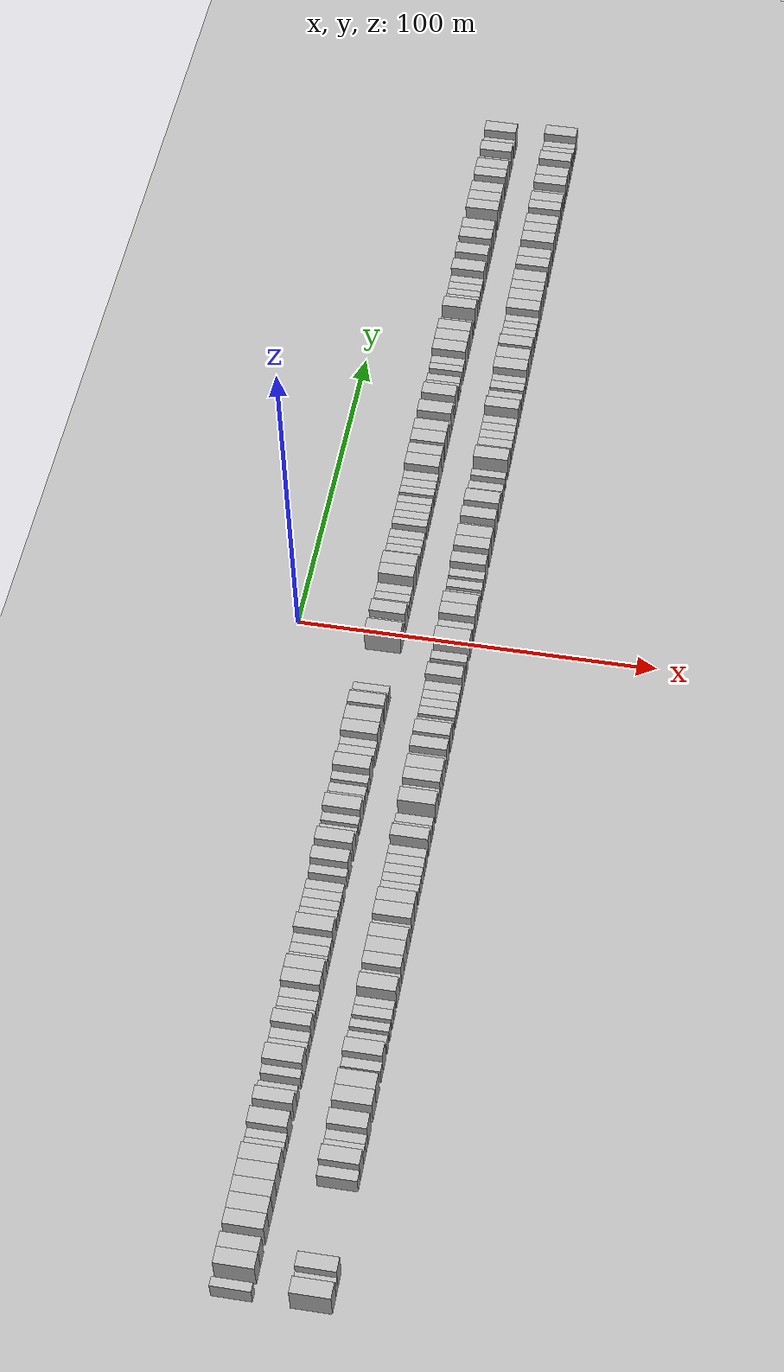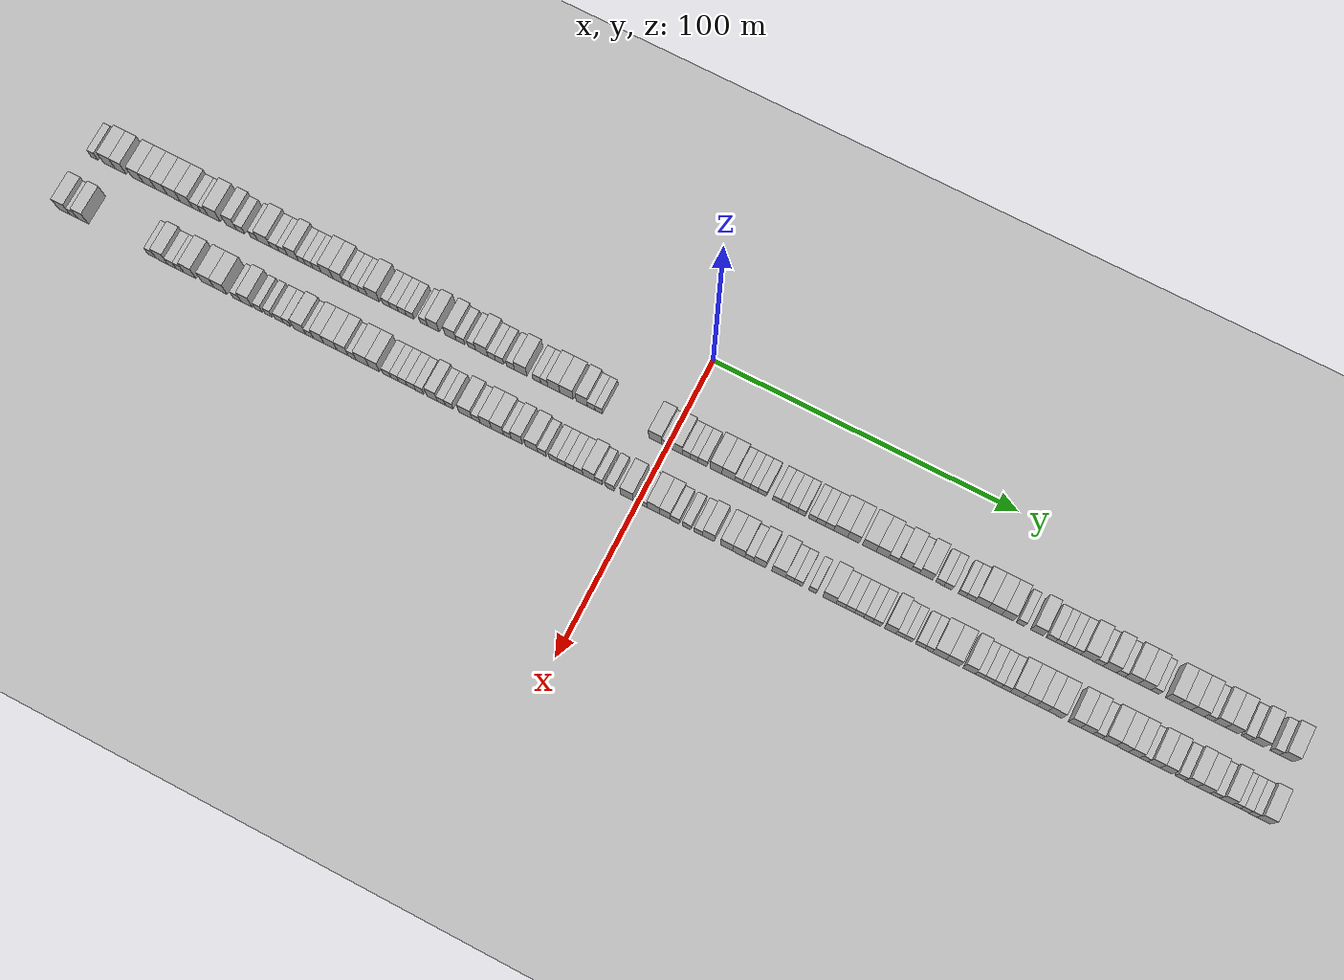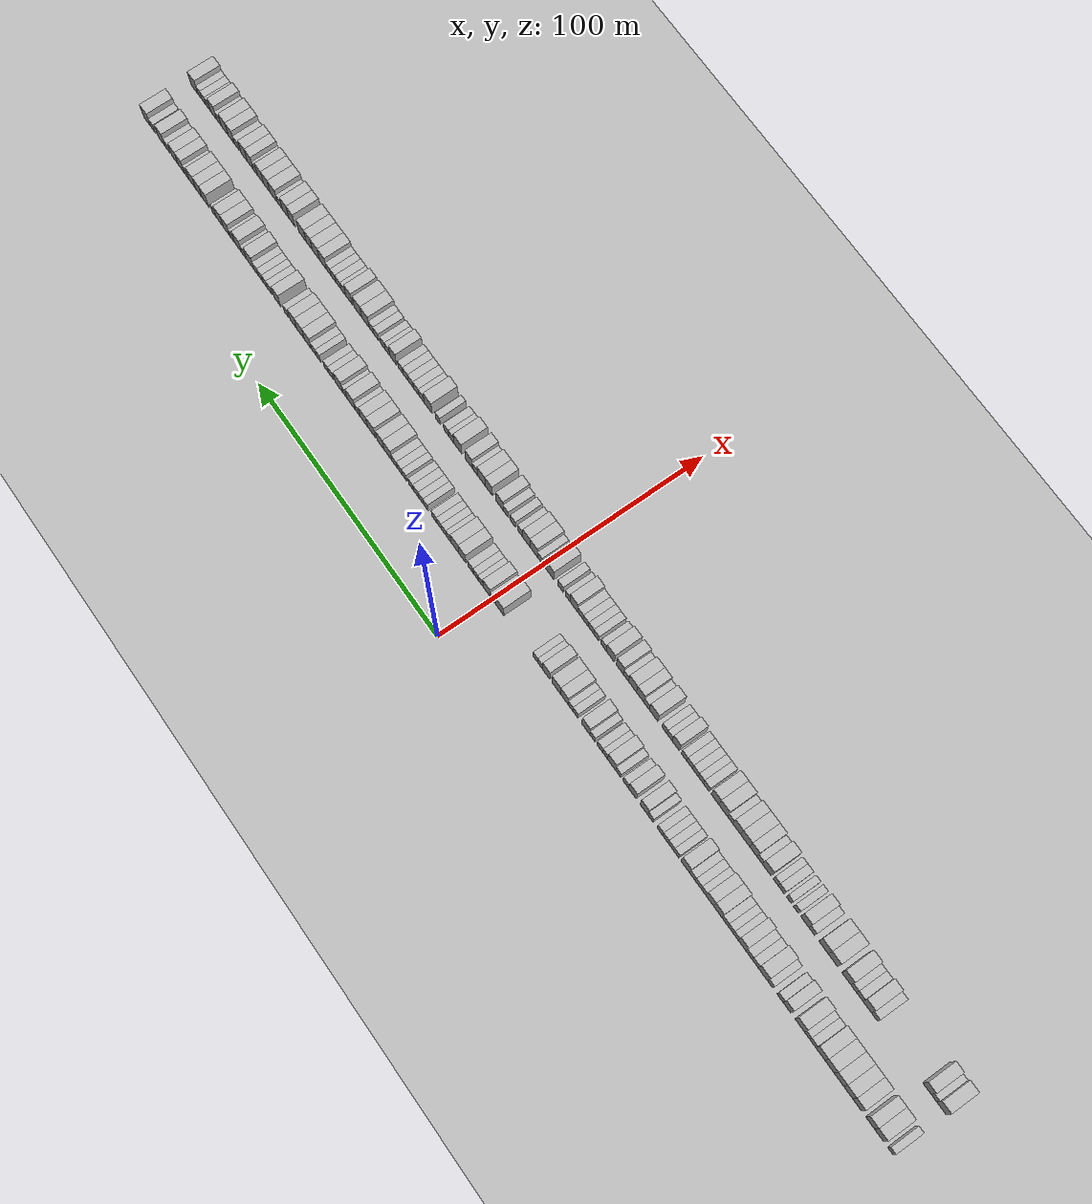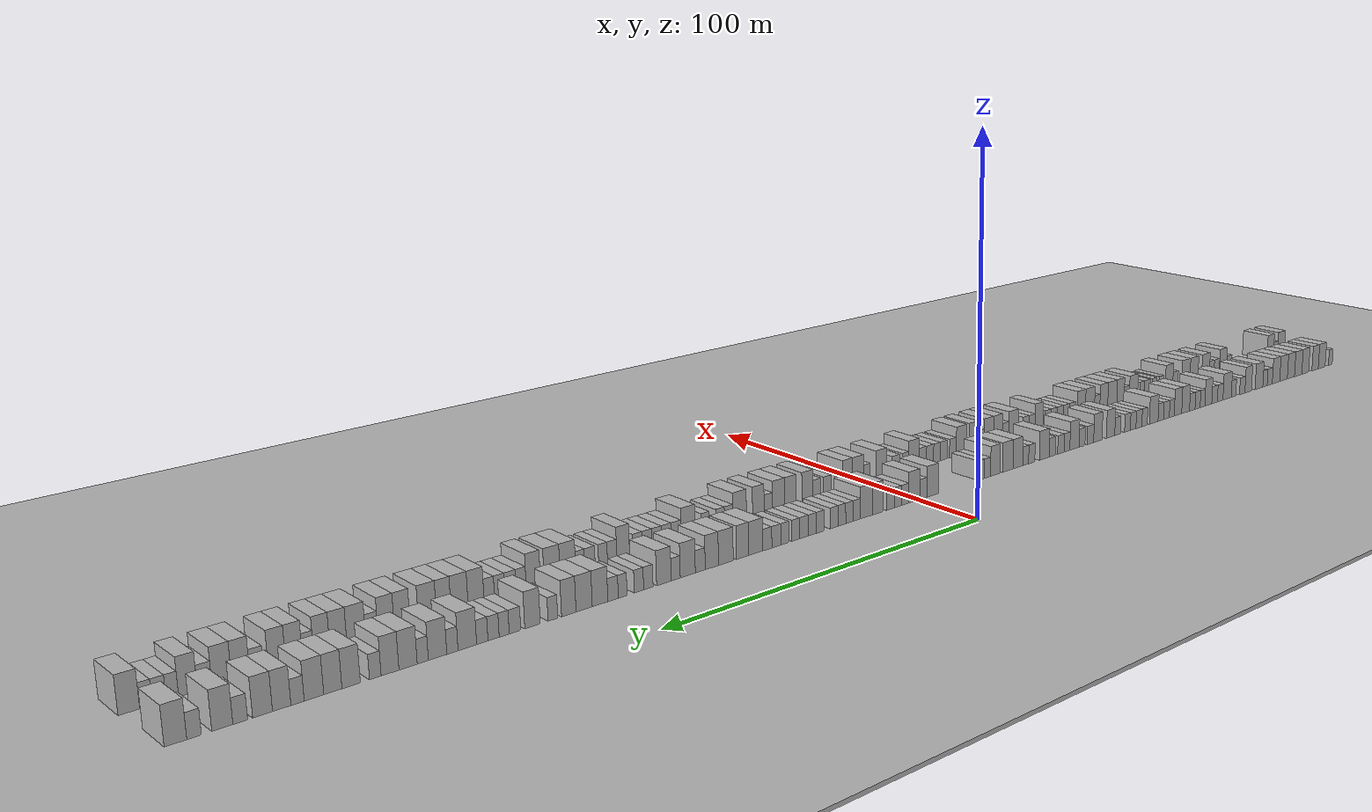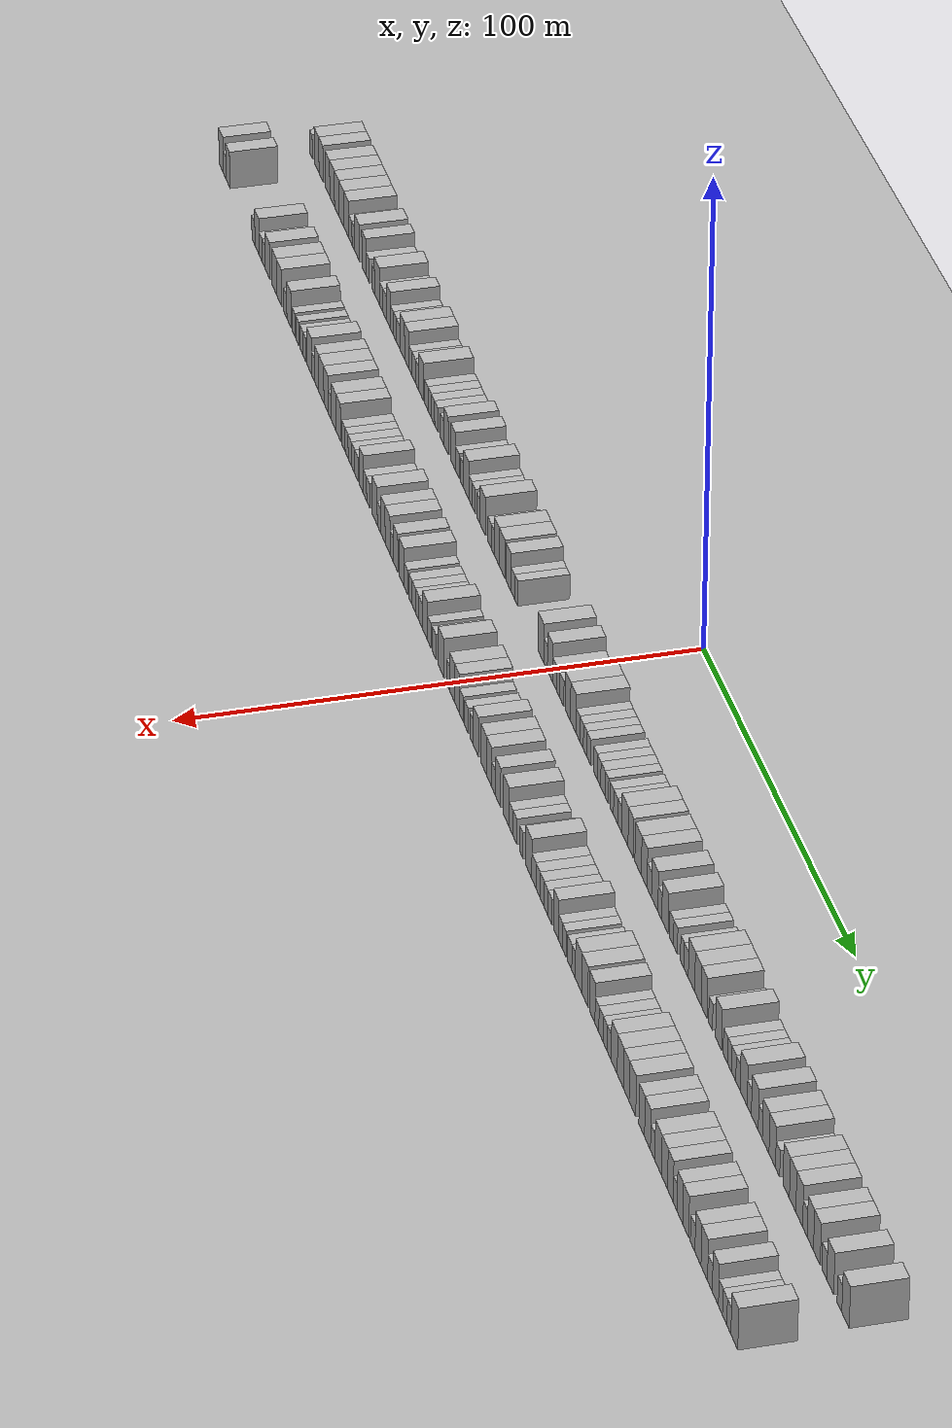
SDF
<?xml version="1.0" encoding="utf-8"?>

<sdf version="1.6">

   <world name="default">

      <gui fullscreen="0">

         <camera name="user_camera">

            <pose>-15 0 4.57585 0 0 0</pose>

            <view_controller>orbit</view_controller>

         </camera>

      </gui>

      <scene>

         <sky>

           <clouds>

             <speed>12</speed>

           </clouds>

         </sky>

         <ambient>0.4 0.4 0.4 1</ambient>

         <background>0.7 0.7 0.7 1</background>

         <shadows>1</shadows>

      </scene>

      <gravity>0 0 -9.8066</gravity>

      <magnetic_field>6e-06 2.3e-05 -4.2e-05</magnetic_field>

      <physics default="0" name="default_physics" type="ode">

         <ode>

            <solver>

               <type>quick</type>

               <iters>10</iters>

               <sor>1.0</sor>

               <use_dynamic_moi_rescaling>0</use_dynamic_moi_rescaling>

            </solver>

            <constraints>

               <cfm>0</cfm>

               <erp>0.2</erp>

               <contact_max_correcting_vel>100</contact_max_correcting_vel>

               <contact_surface_layer>0.001</contact_surface_layer>

            </constraints>

         </ode>

         <max_step_size>0.004</max_step_size>

         <real_time_factor>1</real_time_factor>

         <real_time_update_rate>250</real_time_update_rate>

      </physics>

      <light name="sun" type="directional">

         <cast_shadows>1</cast_shadows>

         <pose>0 0 10 0 0 0</pose>

         <diffuse>0.8 0.8 0.8 1</diffuse>

         <specular>0.2 0.2 0.2 1</specular>

         <attenuation>

            <range>1000</range>

            <constant>0.9</constant>

            <linear>0.01</linear>

            <quadratic>0.001</quadratic>

         </attenuation>

         <direction>-0.5 0.1 -0.9</direction>

      </light>

      <include>

         <name>ground_plane_1</name>

         <uri>model://HANNAS_ground_plane</uri>

         <pose>0 0 0  0 0 0</pose>

      </include>

      <include>

         <name>ground_plane_2</name>

         <uri>model://HANNAS_ground_plane</uri>

         <pose>100 0 0  0 0 0</pose>

      </include>

      <model name="building_1">

         <static>1</static>

         <pose frame="">25.0000 -196.7966 0 0.000000 0.000000 0.000000</pose>

         <link name="link">

            <pose frame="">0 0 3.00 0 0 0</pose>

            <collision name="collision">

               <geometry>

                  <box>

                     <size>10.0000 2.4068 6.0000</size>

                  </box>

               </geometry>

               <max_contacts>10</max_contacts>

               <surface>

                  <contact>

                     <ode/>

                  </contact>

                  <bounce/>

                  <friction>

                     <torsional>

                        <ode/>

                     </torsional>

                     <ode/>

                  </friction>

               </surface>

            </collision>

            <visual name="visual">

               <cast_shadows>0</cast_shadows>

               <geometry>

                  <box>

                     <size>10.0000 2.4068 6.0000</size>

                  </box>

               </geometry>

               <material>

                  <script>

                     <uri>model://HANNAS_wall/materials/scripts</uri>

                     <uri>model://HANNAS_wall/materials/textures</uri>

                     <name>vrc/HANNAS_wall</name>

                  </script>

               </material>

            </visual>

            <self_collide>0</self_collide>

            <enable_wind>0</enable_wind>

            <kinematic>0</kinematic>

         </link>

      </model>

      <model name="building_2">

         <static>1</static>

         <pose frame="">25.0000 -191.4744 0 0.000000 0.000000 0.000000</pose>

         <link name="link">

            <pose frame="">0 0 4.50 0 0 0</pose>

            <collision name="collision">

               <geometry>

                  <box>

                     <size>10.0000 4.2375 9.0000</size>

                  </box>

               </geometry>

               <max_contacts>10</max_contacts>

               <surface>

                  <contact>

                     <ode/>

                  </contact>

                  <bounce/>

                  <friction>

                     <torsional>

                        <ode/>

                     </torsional>

                     <ode/>

                  </friction>

               </surface>

            </collision>

            <visual name="visual">

               <cast_shadows>0</cast_shadows>

               <geometry>

                  <box>

                     <size>10.0000 4.2375 9.0000</size>

                  </box>

               </geometry>

               <material>

                  <script>

                     <uri>model://HANNAS_wall/materials/scripts</uri>

                     <uri>model://HANNAS_wall/materials/textures</uri>

                     <name>vrc/HANNAS_wall</name>

                  </script>

               </material>

            </visual>

            <self_collide>0</self_collide>

            <enable_wind>0</enable_wind>

            <kinematic>0</kinematic>

         </link>

      </model>

      <model name="building_3">

         <static>1</static>

         <pose frame="">25.0000 -187.4311 0 0.000000 0.000000 0.000000</pose>

         <link name="link">

            <pose frame="">0 0 4.50 0 0 0</pose>

            <collision name="collision">

               <geometry>

                  <box>

                     <size>10.0000 3.8492 9.0000</size>

                  </box>

               </geometry>

               <max_contacts>10</max_contacts>

               <surface>

                  <contact>

                     <ode/>

                  </contact>

                  <bounce/>

                  <friction>

                     <torsional>

                        <ode/>

                     </torsional>

                     <ode/>

                  </friction>

               </surface>

            </collision>

            <visual name="visual">

               <cast_shadows>0</cast_shadows>

               <geometry>

                  <box>

                     <size>10.0000 3.8492 9.0000</size>

                  </box>

               </geometry>

               <material>

                  <script>

                     <uri>model://HANNAS_wall/materials/scripts</uri>

                     <uri>model://HANNAS_wall/materials/textures</uri>

                     <name>vrc/HANNAS_wall</name>

                  </script>

               </material>

            </visual>

            <self_collide>0</self_collide>

            <enable_wind>0</enable_wind>

            <kinematic>0</kinematic>

         </link>

      </model>

      <model name="building_4">

         <static>1</static>

         <pose frame="">25.0000 -181.4593 0 0.000000 0.000000 0.000000</pose>

         <link name="link">

            <pose frame="">0 0 4.50 0 0 0</pose>

            <collision name="collision">

               <geometry>

                  <box>

                     <size>10.0000 4.0943 9.0000</size>

                  </box>

               </geometry>

               <max_contacts>10</max_contacts>

               <surface>

                  <contact>

                     <ode/>

                  </contact>

                  <bounce/>

                  <friction>

                     <torsional>

                        <ode/>

                     </torsional>

                     <ode/>

                  </friction>

               </surface>

            </collision>

            <visual name="visual">

               <cast_shadows>0</cast_shadows>

               <geometry>

                  <box>

                     <size>10.0000 4.0943 9.0000</size>

                  </box>

               </geometry>

               <material>

                  <script>

                     <uri>model://HANNAS_wall/materials/scripts</uri>

                     <uri>model://HANNAS_wall/materials/textures</uri>

                     <name>vrc/HANNAS_wall</name>

                  </script>

               </material>

            </visual>

            <self_collide>0</self_collide>

            <enable_wind>0</enable_wind>

            <kinematic>0</kinematic>

         </link>

      </model>

      <model name="building_5">

         <static>1</static>

         <pose frame="">25.0000 -177.2593 0 0.000000 0.000000 0.000000</pose>

         <link name="link">

            <pose frame="">0 0 4.50 0 0 0</pose>

            <collision name="collision">

               <geometry>

                  <box>

                     <size>10.0000 4.3057 9.0000</size>

                  </box>

               </geometry>

               <max_contacts>10</max_contacts>

               <surface>

                  <contact>

                     <ode/>

                  </contact>

                  <bounce/>

                  <friction>

                     <torsional>

                        <ode/>

                     </torsional>

                     <ode/>

                  </friction>

               </surface>

            </collision>

            <visual name="visual">

               <cast_shadows>0</cast_shadows>

               <geometry>

                  <box>

                     <size>10.0000 4.3057 9.0000</size>

                  </box>

               </geometry>

               <material>

                  <script>

                     <uri>model://HANNAS_wall/materials/scripts</uri>

                     <uri>model://HANNAS_wall/materials/textures</uri>

                     <name>vrc/HANNAS_wall</name>

                  </script>

               </material>

            </visual>

            <self_collide>0</self_collide>

            <enable_wind>0</enable_wind>

            <kinematic>0</kinematic>

         </link>

      </model>

      <model name="building_6">

         <static>1</static>

         <pose frame="">25.0000 -172.9911 0 0.000000 0.000000 0.000000</pose>

         <link name="link">

            <pose frame="">0 0 4.50 0 0 0</pose>

            <collision name="collision">

               <geometry>

                  <box>

                     <size>10.0000 4.2307 9.0000</size>

                  </box>

               </geometry>

               <max_contacts>10</max_contacts>

               <surface>

                  <contact>

                     <ode/>

                  </contact>

                  <bounce/>

                  <friction>

                     <torsional>

                        <ode/>

                     </torsional>

                     <ode/>

                  </friction>

               </surface>

            </collision>

            <visual name="visual">

               <cast_shadows>0</cast_shadows>

               <geometry>

                  <box>

                     <size>10.0000 4.2307 9.0000</size>

                  </box>

               </geometry>

               <material>

                  <script>

                     <uri>model://HANNAS_wall/materials/scripts</uri>

                     <uri>model://HANNAS_wall/materials/textures</uri>

                     <name>vrc/HANNAS_wall</name>

                  </script>

               </material>

            </visual>

            <self_collide>0</self_collide>

            <enable_wind>0</enable_wind>

            <kinematic>0</kinematic>

         </link>

      </model>

      <model name="building_7">

         <static>1</static>

         <pose frame="">25.0000 -168.6613 0 0.000000 0.000000 0.000000</pose>

         <link name="link">

            <pose frame="">0 0 4.50 0 0 0</pose>

            <collision name="collision">

               <geometry>

                  <box>

                     <size>10.0000 4.4288 9.0000</size>

                  </box>

               </geometry>

               <max_contacts>10</max_contacts>

               <surface>

                  <contact>

                     <ode/>

                  </contact>

                  <bounce/>

                  <friction>

                     <torsional>

                        <ode/>

                     </torsional>

                     <ode/>

                  </friction>

               </surface>

            </collision>

            <visual name="visual">

               <cast_shadows>0</cast_shadows>

               <geometry>

                  <box>

                     <size>10.0000 4.4288 9.0000</size>

                  </box>

               </geometry>

               <material>

                  <script>

                     <uri>model://HANNAS_wall/materials/scripts</uri>

                     <uri>model://HANNAS_wall/materials/textures</uri>

                     <name>vrc/HANNAS_wall</name>

                  </script>

               </material>

            </visual>

            <self_collide>0</self_collide>

            <enable_wind>0</enable_wind>

            <kinematic>0</kinematic>

         </link>

      </model>

      <model name="building_8">

         <static>1</static>

         <pose frame="">25.0000 -164.3003 0 0.000000 0.000000 0.000000</pose>

         <link name="link">

            <pose frame="">0 0 4.50 0 0 0</pose>

            <collision name="collision">

               <geometry>

                  <box>

                     <size>10.0000 4.2933 9.0000</size>

                  </box>

               </geometry>

               <max_contacts>10</max_contacts>

               <surface>

                  <contact>

                     <ode/>

                  </contact>

                  <bounce/>

                  <friction>

                     <torsional>

                        <ode/>

                     </torsional>

                     <ode/>

                  </friction>

               </surface>

            </collision>

            <visual name="visual">

               <cast_shadows>0</cast_shadows>

               <geometry>

                  <box>

                     <size>10.0000 4.2933 9.0000</size>

                  </box>

               </geometry>

               <material>

                  <script>

                     <uri>model://HANNAS_wall/materials/scripts</uri>

                     <uri>model://HANNAS_wall/materials/textures</uri>

                     <name>vrc/HANNAS_wall</name>

                  </script>

               </material>

            </visual>

            <self_collide>0</self_collide>

            <enable_wind>0</enable_wind>

            <kinematic>0</kinematic>

         </link>

      </model>

      <model name="building_9">

         <static>1</static>

         <pose frame="">25.0000 -160.7059 0 0.000000 0.000000 0.000000</pose>

         <link name="link">

            <pose frame="">0 0 3.00 0 0 0</pose>

            <collision name="collision">

               <geometry>

                  <box>

                     <size>10.0000 2.8955 6.0000</size>

                  </box>

               </geometry>

               <max_contacts>10</max_contacts>

               <surface>

                  <contact>

                     <ode/>

                  </contact>

                  <bounce/>

                  <friction>

                     <torsional>

                        <ode/>

                     </torsional>

                     <ode/>

                  </friction>

               </surface>

            </collision>

            <visual name="visual">

               <cast_shadows>0</cast_shadows>

               <geometry>

                  <box>

                     <size>10.0000 2.8955 6.0000</size>

                  </box>

               </geometry>

               <material>

                  <script>

                     <uri>model://HANNAS_wall/materials/scripts</uri>

                     <uri>model://HANNAS_wall/materials/textures</uri>

                     <name>vrc/HANNAS_wall</name>

                  </script>

               </material>

            </visual>

            <self_collide>0</self_collide>

            <enable_wind>0</enable_wind>

            <kinematic>0</kinematic>

         </link>

      </model>

      <model name="building_10">

         <static>1</static>

         <pose frame="">25.0000 -158.0257 0 0.000000 0.000000 0.000000</pose>

         <link name="link">

            <pose frame="">0 0 3.00 0 0 0</pose>

            <collision name="collision">

               <geometry>

                  <box>

                     <size>10.0000 2.4648 6.0000</size>

                  </box>

               </geometry>

               <max_contacts>10</max_contacts>

               <surface>

                  <contact>

                     <ode/>

                  </contact>

                  <bounce/>

                  <friction>

                     <torsional>

                        <ode/>

                     </torsional>

                     <ode/>

                  </friction>

               </surface>

            </collision>

            <visual name="visual">

               <cast_shadows>0</cast_shadows>

               <geometry>

                  <box>

                     <size>10.0000 2.4648 6.0000</size>

                  </box>

               </geometry>

               <material>

                  <script>

                     <uri>model://HANNAS_wall/materials/scripts</uri>

                     <uri>model://HANNAS_wall/materials/textures</uri>

                     <name>vrc/HANNAS_wall</name>

                  </script>

               </material>

            </visual>

            <self_collide>0</self_collide>

            <enable_wind>0</enable_wind>

            <kinematic>0</kinematic>

         </link>

      </model>

      <model name="building_11">

         <static>1</static>

         <pose frame="">25.0000 -154.6019 0 0.000000 0.000000 0.000000</pose>

         <link name="link">

            <pose frame="">0 0 4.50 0 0 0</pose>

            <collision name="collision">

               <geometry>

                  <box>

                     <size>10.0000 4.3829 9.0000</size>

                  </box>

               </geometry>

               <max_contacts>10</max_contacts>

               <surface>

                  <contact>

                     <ode/>

                  </contact>

                  <bounce/>

                  <friction>

                     <torsional>

                        <ode/>

                     </torsional>

                     <ode/>

                  </friction>

               </surface>

            </collision>

            <visual name="visual">

               <cast_shadows>0</cast_shadows>

               <geometry>

                  <box>

                     <size>10.0000 4.3829 9.0000</size>

                  </box>

               </geometry>

               <material>

                  <script>

                     <uri>model://HANNAS_wall/materials/scripts</uri>

                     <uri>model://HANNAS_wall/materials/textures</uri>

                     <name>vrc/HANNAS_wall</name>

                  </script>

               </material>

            </visual>

            <self_collide>0</self_collide>

            <enable_wind>0</enable_wind>

            <kinematic>0</kinematic>

         </link>

      </model>

      <model name="building_12">

         <static>1</static>

         <pose frame="">25.0000 -148.5949 0 0.000000 0.000000 0.000000</pose>

         <link name="link">

            <pose frame="">0 0 4.50 0 0 0</pose>

            <collision name="collision">

               <geometry>

                  <box>

                     <size>10.0000 3.6311 9.0000</size>

                  </box>

               </geometry>

               <max_contacts>10</max_contacts>

               <surface>

                  <contact>

                     <ode/>

                  </contact>

                  <bounce/>

                  <friction>

                     <torsional>

                        <ode/>

                     </torsional>

                     <ode/>

                  </friction>

               </surface>

            </collision>

            <visual name="visual">

               <cast_shadows>0</cast_shadows>

               <geometry>

                  <box>

                     <size>10.0000 3.6311 9.0000</size>

                  </box>

               </geometry>

               <material>

                  <script>

                     <uri>model://HANNAS_wall/materials/scripts</uri>

                     <uri>model://HANNAS_wall/materials/textures</uri>

                     <name>vrc/HANNAS_wall</name>

                  </script>

               </material>

            </visual>

            <self_collide>0</self_collide>

            <enable_wind>0</enable_wind>

            <kinematic>0</kinematic>

         </link>

      </model>

      <model name="building_13">

         <static>1</static>

         <pose frame="">25.0000 -145.2932 0 0.000000 0.000000 0.000000</pose>

         <link name="link">

            <pose frame="">0 0 3.00 0 0 0</pose>

            <collision name="collision">

               <geometry>

                  <box>

                     <size>10.0000 2.9723 6.0000</size>

                  </box>

               </geometry>

               <max_contacts>10</max_contacts>

               <surface>

                  <contact>

                     <ode/>

                  </contact>

                  <bounce/>

                  <friction>

                     <torsional>

                        <ode/>

                     </torsional>

                     <ode/>

                  </friction>

               </surface>

            </collision>

            <visual name="visual">

               <cast_shadows>0</cast_shadows>

               <geometry>

                  <box>

                     <size>10.0000 2.9723 6.0000</size>

                  </box>

               </geometry>

               <material>

                  <script>

                     <uri>model://HANNAS_wall/materials/scripts</uri>

                     <uri>model://HANNAS_wall/materials/textures</uri>

                     <name>vrc/HANNAS_wall</name>

                  </script>

               </material>

            </visual>

            <self_collide>0</self_collide>

            <enable_wind>0</enable_wind>

            <kinematic>0</kinematic>

         </link>

      </model>

      <model name="building_14">

         <static>1</static>

         <pose frame="">25.0000 -140.5572 0 0.000000 0.000000 0.000000</pose>

         <link name="link">

            <pose frame="">0 0 3.00 0 0 0</pose>

            <collision name="collision">

               <geometry>

                  <box>

                     <size>10.0000 2.4997 6.0000</size>

                  </box>

               </geometry>

               <max_contacts>10</max_contacts>

               <surface>

                  <contact>

                     <ode/>

                  </contact>

                  <bounce/>

                  <friction>

                     <torsional>

                        <ode/>

                     </torsional>

                     <ode/>

                  </friction>

               </surface>

            </collision>

            <visual name="visual">

               <cast_shadows>0</cast_shadows>

               <geometry>

                  <box>

                     <size>10.0000 2.4997 6.0000</size>

                  </box>

               </geometry>

               <material>

                  <script>

                     <uri>model://HANNAS_wall/materials/scripts</uri>

                     <uri>model://HANNAS_wall/materials/textures</uri>

                     <name>vrc/HANNAS_wall</name>

                  </script>

               </material>

            </visual>

            <self_collide>0</self_collide>

            <enable_wind>0</enable_wind>

            <kinematic>0</kinematic>

         </link>

      </model>

      <model name="building_15">

         <static>1</static>

         <pose frame="">25.0000 -137.0640 0 0.000000 0.000000 0.000000</pose>

         <link name="link">

            <pose frame="">0 0 4.50 0 0 0</pose>

            <collision name="collision">

               <geometry>

                  <box>

                     <size>10.0000 4.4868 9.0000</size>

                  </box>

               </geometry>

               <max_contacts>10</max_contacts>

               <surface>

                  <contact>

                     <ode/>

                  </contact>

                  <bounce/>

                  <friction>

                     <torsional>

                        <ode/>

                     </torsional>

                     <ode/>

                  </friction>

               </surface>

            </collision>

            <visual name="visual">

               <cast_shadows>0</cast_shadows>

               <geometry>

                  <box>

                     <size>10.0000 4.4868 9.0000</size>

                  </box>

               </geometry>

               <material>

                  <script>

                     <uri>model://HANNAS_wall/materials/scripts</uri>

                     <uri>model://HANNAS_wall/materials/textures</uri>

                     <name>vrc/HANNAS_wall</name>

                  </script>

               </material>

            </visual>

            <self_collide>0</self_collide>

            <enable_wind>0</enable_wind>

            <kinematic>0</kinematic>

         </link>

      </model>

      <model name="building_16">

         <static>1</static>

         <pose frame="">25.0000 -133.3309 0 0.000000 0.000000 0.000000</pose>

         <link name="link">

            <pose frame="">0 0 3.00 0 0 0</pose>

            <collision name="collision">

               <geometry>

                  <box>

                     <size>10.0000 2.9795 6.0000</size>

                  </box>

               </geometry>

               <max_contacts>10</max_contacts>

               <surface>

                  <contact>

                     <ode/>

                  </contact>

                  <bounce/>

                  <friction>

                     <torsional>

                        <ode/>

                     </torsional>

                     <ode/>

                  </friction>

               </surface>

            </collision>

            <visual name="visual">

               <cast_shadows>0</cast_shadows>

               <geometry>

                  <box>

                     <size>10.0000 2.9795 6.0000</size>

                  </box>

               </geometry>

               <material>

                  <script>

                     <uri>model://HANNAS_wall/materials/scripts</uri>

                     <uri>model://HANNAS_wall/materials/textures</uri>

                     <name>vrc/HANNAS_wall</name>

                  </script>

               </material>

            </visual>

            <self_collide>0</self_collide>

            <enable_wind>0</enable_wind>

            <kinematic>0</kinematic>

         </link>

      </model>

      <model name="building_17">

         <static>1</static>

         <pose frame="">25.0000 -130.3622 0 0.000000 0.000000 0.000000</pose>

         <link name="link">

            <pose frame="">0 0 3.00 0 0 0</pose>

            <collision name="collision">

               <geometry>

                  <box>

                     <size>10.0000 2.9579 6.0000</size>

                  </box>

               </geometry>

               <max_contacts>10</max_contacts>

               <surface>

                  <contact>

                     <ode/>

                  </contact>

                  <bounce/>

                  <friction>

                     <torsional>

                        <ode/>

                     </torsional>

                     <ode/>

                  </friction>

               </surface>

            </collision>

            <visual name="visual">

               <cast_shadows>0</cast_shadows>

               <geometry>

                  <box>

                     <size>10.0000 2.9579 6.0000</size>

                  </box>

               </geometry>

               <material>

                  <script>

                     <uri>model://HANNAS_wall/materials/scripts</uri>

                     <uri>model://HANNAS_wall/materials/textures</uri>

                     <name>vrc/HANNAS_wall</name>

                  </script>

               </material>

            </visual>

            <self_collide>0</self_collide>

            <enable_wind>0</enable_wind>

            <kinematic>0</kinematic>

         </link>

      </model>

      <model name="building_18">

         <static>1</static>

         <pose frame="">25.0000 -127.0378 0 0.000000 0.000000 0.000000</pose>

         <link name="link">

            <pose frame="">0 0 4.50 0 0 0</pose>

            <collision name="collision">

               <geometry>

                  <box>

                     <size>10.0000 3.6909 9.0000</size>

                  </box>

               </geometry>

               <max_contacts>10</max_contacts>

               <surface>

                  <contact>

                     <ode/>

                  </contact>

                  <bounce/>

                  <friction>

                     <torsional>

                        <ode/>

                     </torsional>

                     <ode/>

                  </friction>

               </surface>

            </collision>

            <visual name="visual">

               <cast_shadows>0</cast_shadows>

               <geometry>

                  <box>

                     <size>10.0000 3.6909 9.0000</size>

                  </box>

               </geometry>

               <material>

                  <script>

                     <uri>model://HANNAS_wall/materials/scripts</uri>

                     <uri>model://HANNAS_wall/materials/textures</uri>

                     <name>vrc/HANNAS_wall</name>

                  </script>

               </material>

            </visual>

            <self_collide>0</self_collide>

            <enable_wind>0</enable_wind>

            <kinematic>0</kinematic>

         </link>

      </model>

      <model name="building_19">

         <static>1</static>

         <pose frame="">25.0000 -123.9775 0 0.000000 0.000000 0.000000</pose>

         <link name="link">

            <pose frame="">0 0 3.00 0 0 0</pose>

            <collision name="collision">

               <geometry>

                  <box>

                     <size>10.0000 2.4298 6.0000</size>

                  </box>

               </geometry>

               <max_contacts>10</max_contacts>

               <surface>

                  <contact>

                     <ode/>

                  </contact>

                  <bounce/>

                  <friction>

                     <torsional>

                        <ode/>

                     </torsional>

                     <ode/>

                  </friction>

               </surface>

            </collision>

            <visual name="visual">

               <cast_shadows>0</cast_shadows>

               <geometry>

                  <box>

                     <size>10.0000 2.4298 6.0000</size>

                  </box>

               </geometry>

               <material>

                  <script>

                     <uri>model://HANNAS_wall/materials/scripts</uri>

                     <uri>model://HANNAS_wall/materials/textures</uri>

                     <name>vrc/HANNAS_wall</name>

                  </script>

               </material>

            </visual>

            <self_collide>0</self_collide>

            <enable_wind>0</enable_wind>

            <kinematic>0</kinematic>

         </link>

      </model>

      <model name="building_20">

         <static>1</static>

         <pose frame="">25.0000 -121.4424 0 0.000000 0.000000 0.000000</pose>

         <link name="link">

            <pose frame="">0 0 3.00 0 0 0</pose>

            <collision name="collision">

               <geometry>

                  <box>

                     <size>10.0000 2.6403 6.0000</size>

                  </box>

               </geometry>

               <max_contacts>10</max_contacts>

               <surface>

                  <contact>

                     <ode/>

                  </contact>

                  <bounce/>

                  <friction>

                     <torsional>

                        <ode/>

                     </torsional>

                     <ode/>

                  </friction>

               </surface>

            </collision>

            <visual name="visual">

               <cast_shadows>0</cast_shadows>

               <geometry>

                  <box>

                     <size>10.0000 2.6403 6.0000</size>

                  </box>

               </geometry>

               <material>

                  <script>

                     <uri>model://HANNAS_wall/materials/scripts</uri>

                     <uri>model://HANNAS_wall/materials/textures</uri>

                     <name>vrc/HANNAS_wall</name>

                  </script>

               </material>

            </visual>

            <self_collide>0</self_collide>

            <enable_wind>0</enable_wind>

            <kinematic>0</kinematic>

         </link>

      </model>

      <model name="building_21">

         <static>1</static>

         <pose frame="">25.0000 -118.6902 0 0.000000 0.000000 0.000000</pose>

         <link name="link">

            <pose frame="">0 0 3.00 0 0 0</pose>

            <collision name="collision">

               <geometry>

                  <box>

                     <size>10.0000 2.8641 6.0000</size>

                  </box>

               </geometry>

               <max_contacts>10</max_contacts>

               <surface>

                  <contact>

                     <ode/>

                  </contact>

                  <bounce/>

                  <friction>

                     <torsional>

                        <ode/>

                     </torsional>

                     <ode/>

                  </friction>

               </surface>

            </collision>

            <visual name="visual">

               <cast_shadows>0</cast_shadows>

               <geometry>

                  <box>

                     <size>10.0000 2.8641 6.0000</size>

                  </box>

               </geometry>

               <material>

                  <script>

                     <uri>model://HANNAS_wall/materials/scripts</uri>

                     <uri>model://HANNAS_wall/materials/textures</uri>

                     <name>vrc/HANNAS_wall</name>

                  </script>

               </material>

            </visual>

            <self_collide>0</self_collide>

            <enable_wind>0</enable_wind>

            <kinematic>0</kinematic>

         </link>

      </model>

      <model name="building_22">

         <static>1</static>

         <pose frame="">25.0000 -115.2662 0 0.000000 0.000000 0.000000</pose>

         <link name="link">

            <pose frame="">0 0 4.50 0 0 0</pose>

            <collision name="collision">

               <geometry>

                  <box>

                     <size>10.0000 3.9840 9.0000</size>

                  </box>

               </geometry>

               <max_contacts>10</max_contacts>

               <surface>

                  <contact>

                     <ode/>

                  </contact>

                  <bounce/>

                  <friction>

                     <torsional>

                        <ode/>

                     </torsional>

                     <ode/>

                  </friction>

               </surface>

            </collision>

            <visual name="visual">

               <cast_shadows>0</cast_shadows>

               <geometry>

                  <box>

                     <size>10.0000 3.9840 9.0000</size>

                  </box>

               </geometry>

               <material>

                  <script>

                     <uri>model://HANNAS_wall/materials/scripts</uri>

                     <uri>model://HANNAS_wall/materials/textures</uri>

                     <name>vrc/HANNAS_wall</name>

                  </script>

               </material>

            </visual>

            <self_collide>0</self_collide>

            <enable_wind>0</enable_wind>

            <kinematic>0</kinematic>

         </link>

      </model>

      <model name="building_23">

         <static>1</static>

         <pose frame="">25.0000 -111.3850 0 0.000000 0.000000 0.000000</pose>

         <link name="link">

            <pose frame="">0 0 4.50 0 0 0</pose>

            <collision name="collision">

               <geometry>

                  <box>

                     <size>10.0000 3.7785 9.0000</size>

                  </box>

               </geometry>

               <max_contacts>10</max_contacts>

               <surface>

                  <contact>

                     <ode/>

                  </contact>

                  <bounce/>

                  <friction>

                     <torsional>

                        <ode/>

                     </torsional>

                     <ode/>

                  </friction>

               </surface>

            </collision>

            <visual name="visual">

               <cast_shadows>0</cast_shadows>

               <geometry>

                  <box>

                     <size>10.0000 3.7785 9.0000</size>

                  </box>

               </geometry>

               <material>

                  <script>

                     <uri>model://HANNAS_wall/materials/scripts</uri>

                     <uri>model://HANNAS_wall/materials/textures</uri>

                     <name>vrc/HANNAS_wall</name>

                  </script>

               </material>

            </visual>

            <self_collide>0</self_collide>

            <enable_wind>0</enable_wind>

            <kinematic>0</kinematic>

         </link>

      </model>

      <model name="building_24">

         <static>1</static>

         <pose frame="">25.0000 -108.2642 0 0.000000 0.000000 0.000000</pose>

         <link name="link">

            <pose frame="">0 0 3.00 0 0 0</pose>

            <collision name="collision">

               <geometry>

                  <box>

                     <size>10.0000 2.4630 6.0000</size>

                  </box>

               </geometry>

               <max_contacts>10</max_contacts>

               <surface>

                  <contact>

                     <ode/>

                  </contact>

                  <bounce/>

                  <friction>

                     <torsional>

                        <ode/>

                     </torsional>

                     <ode/>

                  </friction>

               </surface>

            </collision>

            <visual name="visual">

               <cast_shadows>0</cast_shadows>

               <geometry>

                  <box>

                     <size>10.0000 2.4630 6.0000</size>

                  </box>

               </geometry>

               <material>

                  <script>

                     <uri>model://HANNAS_wall/materials/scripts</uri>

                     <uri>model://HANNAS_wall/materials/textures</uri>

                     <name>vrc/HANNAS_wall</name>

                  </script>

               </material>

            </visual>

            <self_collide>0</self_collide>

            <enable_wind>0</enable_wind>

            <kinematic>0</kinematic>

         </link>

      </model>

      <model name="building_25">

         <static>1</static>

         <pose frame="">25.0000 -105.6047 0 0.000000 0.000000 0.000000</pose>

         <link name="link">

            <pose frame="">0 0 3.00 0 0 0</pose>

            <collision name="collision">

               <geometry>

                  <box>

                     <size>10.0000 2.8561 6.0000</size>

                  </box>

               </geometry>

               <max_contacts>10</max_contacts>

               <surface>

                  <contact>

                     <ode/>

                  </contact>

                  <bounce/>

                  <friction>

                     <torsional>

                        <ode/>

                     </torsional>

                     <ode/>

                  </friction>

               </surface>

            </collision>

            <visual name="visual">

               <cast_shadows>0</cast_shadows>

               <geometry>

                  <box>

                     <size>10.0000 2.8561 6.0000</size>

                  </box>

               </geometry>

               <material>

                  <script>

                     <uri>model://HANNAS_wall/materials/scripts</uri>

                     <uri>model://HANNAS_wall/materials/textures</uri>

                     <name>vrc/HANNAS_wall</name>

                  </script>

               </material>

            </visual>

            <self_collide>0</self_collide>

            <enable_wind>0</enable_wind>

            <kinematic>0</kinematic>

         </link>

      </model>

      <model name="building_26">

         <static>1</static>

         <pose frame="">25.0000 -102.8159 0 0.000000 0.000000 0.000000</pose>

         <link name="link">

            <pose frame="">0 0 3.00 0 0 0</pose>

            <collision name="collision">

               <geometry>

                  <box>

                     <size>10.0000 2.7213 6.0000</size>

                  </box>

               </geometry>

               <max_contacts>10</max_contacts>

               <surface>

                  <contact>

                     <ode/>

                  </contact>

                  <bounce/>

                  <friction>

                     <torsional>

                        <ode/>

                     </torsional>

                     <ode/>

                  </friction>

               </surface>

            </collision>

            <visual name="visual">

               <cast_shadows>0</cast_shadows>

               <geometry>

                  <box>

                     <size>10.0000 2.7213 6.0000</size>

                  </box>

               </geometry>

               <material>

                  <script>

                     <uri>model://HANNAS_wall/materials/scripts</uri>

                     <uri>model://HANNAS_wall/materials/textures</uri>

                     <name>vrc/HANNAS_wall</name>

                  </script>

               </material>

            </visual>

            <self_collide>0</self_collide>

            <enable_wind>0</enable_wind>

            <kinematic>0</kinematic>

         </link>

      </model>

      <model name="building_27">

         <static>1</static>

         <pose frame="">25.0000 -99.3141 0 0.000000 0.000000 0.000000</pose>

         <link name="link">

            <pose frame="">0 0 4.50 0 0 0</pose>

            <collision name="collision">

               <geometry>

                  <box>

                     <size>10.0000 4.2824 9.0000</size>

                  </box>

               </geometry>

               <max_contacts>10</max_contacts>

               <surface>

                  <contact>

                     <ode/>

                  </contact>

                  <bounce/>

                  <friction>

                     <torsional>

                        <ode/>

                     </torsional>

                     <ode/>

                  </friction>

               </surface>

            </collision>

            <visual name="visual">

               <cast_shadows>0</cast_shadows>

               <geometry>

                  <box>

                     <size>10.0000 4.2824 9.0000</size>

                  </box>

               </geometry>

               <material>

                  <script>

                     <uri>model://HANNAS_wall/materials/scripts</uri>

                     <uri>model://HANNAS_wall/materials/textures</uri>

                     <name>vrc/HANNAS_wall</name>

                  </script>

               </material>

            </visual>

            <self_collide>0</self_collide>

            <enable_wind>0</enable_wind>

            <kinematic>0</kinematic>

         </link>

      </model>

      <model name="building_28">

         <static>1</static>

         <pose frame="">25.0000 -94.8458 0 0.000000 0.000000 0.000000</pose>

         <link name="link">

            <pose frame="">0 0 3.00 0 0 0</pose>

            <collision name="collision">

               <geometry>

                  <box>

                     <size>10.0000 2.6542 6.0000</size>

                  </box>

               </geometry>

               <max_contacts>10</max_contacts>

               <surface>

                  <contact>

                     <ode/>

                  </contact>

                  <bounce/>

                  <friction>

                     <torsional>

                        <ode/>

                     </torsional>

                     <ode/>

                  </friction>

               </surface>

            </collision>

            <visual name="visual">

               <cast_shadows>0</cast_shadows>

               <geometry>

                  <box>

                     <size>10.0000 2.6542 6.0000</size>

                  </box>

               </geometry>

               <material>

                  <script>

                     <uri>model://HANNAS_wall/materials/scripts</uri>

                     <uri>model://HANNAS_wall/materials/textures</uri>

                     <name>vrc/HANNAS_wall</name>

                  </script>

               </material>

            </visual>

            <self_collide>0</self_collide>

            <enable_wind>0</enable_wind>

            <kinematic>0</kinematic>

         </link>

      </model>

      <model name="building_29">

         <static>1</static>

         <pose frame="">25.0000 -92.1096 0 0.000000 0.000000 0.000000</pose>

         <link name="link">

            <pose frame="">0 0 3.00 0 0 0</pose>

            <collision name="collision">

               <geometry>

                  <box>

                     <size>10.0000 2.8182 6.0000</size>

                  </box>

               </geometry>

               <max_contacts>10</max_contacts>

               <surface>

                  <contact>

                     <ode/>

                  </contact>

                  <bounce/>

                  <friction>

                     <torsional>

                        <ode/>

                     </torsional>

                     <ode/>

                  </friction>

               </surface>

            </collision>

            <visual name="visual">

               <cast_shadows>0</cast_shadows>

               <geometry>

                  <box>

                     <size>10.0000 2.8182 6.0000</size>

                  </box>

               </geometry>

               <material>

                  <script>

                     <uri>model://HANNAS_wall/materials/scripts</uri>

                     <uri>model://HANNAS_wall/materials/textures</uri>

                     <name>vrc/HANNAS_wall</name>

                  </script>

               </material>

            </visual>

            <self_collide>0</self_collide>

            <enable_wind>0</enable_wind>

            <kinematic>0</kinematic>

         </link>

      </model>

      <model name="building_30">

         <static>1</static>

         <pose frame="">25.0000 -89.3585 0 0.000000 0.000000 0.000000</pose>

         <link name="link">

            <pose frame="">0 0 3.00 0 0 0</pose>

            <collision name="collision">

               <geometry>

                  <box>

                     <size>10.0000 2.6840 6.0000</size>

                  </box>

               </geometry>

               <max_contacts>10</max_contacts>

               <surface>

                  <contact>

                     <ode/>

                  </contact>

                  <bounce/>

                  <friction>

                     <torsional>

                        <ode/>

                     </torsional>

                     <ode/>

                  </friction>

               </surface>

            </collision>

            <visual name="visual">

               <cast_shadows>0</cast_shadows>

               <geometry>

                  <box>

                     <size>10.0000 2.6840 6.0000</size>

                  </box>

               </geometry>

               <material>

                  <script>

                     <uri>model://HANNAS_wall/materials/scripts</uri>

                     <uri>model://HANNAS_wall/materials/textures</uri>

                     <name>vrc/HANNAS_wall</name>

                  </script>

               </material>

            </visual>

            <self_collide>0</self_collide>

            <enable_wind>0</enable_wind>

            <kinematic>0</kinematic>

         </link>

      </model>

      <model name="building_31">

         <static>1</static>

         <pose frame="">25.0000 -86.6385 0 0.000000 0.000000 0.000000</pose>

         <link name="link">

            <pose frame="">0 0 3.00 0 0 0</pose>

            <collision name="collision">

               <geometry>

                  <box>

                     <size>10.0000 2.7559 6.0000</size>

                  </box>

               </geometry>

               <max_contacts>10</max_contacts>

               <surface>

                  <contact>

                     <ode/>

                  </contact>

                  <bounce/>

                  <friction>

                     <torsional>

                        <ode/>

                     </torsional>

                     <ode/>

                  </friction>

               </surface>

            </collision>

            <visual name="visual">

               <cast_shadows>0</cast_shadows>

               <geometry>

                  <box>

                     <size>10.0000 2.7559 6.0000</size>

                  </box>

               </geometry>

               <material>

                  <script>

                     <uri>model://HANNAS_wall/materials/scripts</uri>

                     <uri>model://HANNAS_wall/materials/textures</uri>

                     <name>vrc/HANNAS_wall</name>

                  </script>

               </material>

            </visual>

            <self_collide>0</self_collide>

            <enable_wind>0</enable_wind>

            <kinematic>0</kinematic>

         </link>

      </model>

      <model name="building_32">

         <static>1</static>

         <pose frame="">25.0000 -81.9549 0 0.000000 0.000000 0.000000</pose>

         <link name="link">

            <pose frame="">0 0 3.00 0 0 0</pose>

            <collision name="collision">

               <geometry>

                  <box>

                     <size>10.0000 2.6114 6.0000</size>

                  </box>

               </geometry>

               <max_contacts>10</max_contacts>

               <surface>

                  <contact>

                     <ode/>

                  </contact>

                  <bounce/>

                  <friction>

                     <torsional>

                        <ode/>

                     </torsional>

                     <ode/>

                  </friction>

               </surface>

            </collision>

            <visual name="visual">

               <cast_shadows>0</cast_shadows>

               <geometry>

                  <box>

                     <size>10.0000 2.6114 6.0000</size>

                  </box>

               </geometry>

               <material>

                  <script>

                     <uri>model://HANNAS_wall/materials/scripts</uri>

                     <uri>model://HANNAS_wall/materials/textures</uri>

                     <name>vrc/HANNAS_wall</name>

                  </script>

               </material>

            </visual>

            <self_collide>0</self_collide>

            <enable_wind>0</enable_wind>

            <kinematic>0</kinematic>

         </link>

      </model>

      <model name="building_33">

         <static>1</static>

         <pose frame="">25.0000 -78.7079 0 0.000000 0.000000 0.000000</pose>

         <link name="link">

            <pose frame="">0 0 4.50 0 0 0</pose>

            <collision name="collision">

               <geometry>

                  <box>

                     <size>10.0000 3.8826 9.0000</size>

                  </box>

               </geometry>

               <max_contacts>10</max_contacts>

               <surface>

                  <contact>

                     <ode/>

                  </contact>

                  <bounce/>

                  <friction>

                     <torsional>

                        <ode/>

                     </torsional>

                     <ode/>

                  </friction>

               </surface>

            </collision>

            <visual name="visual">

               <cast_shadows>0</cast_shadows>

               <geometry>

                  <box>

                     <size>10.0000 3.8826 9.0000</size>

                  </box>

               </geometry>

               <material>

                  <script>

                     <uri>model://HANNAS_wall/materials/scripts</uri>

                     <uri>model://HANNAS_wall/materials/textures</uri>

                     <name>vrc/HANNAS_wall</name>

                  </script>

               </material>

            </visual>

            <self_collide>0</self_collide>

            <enable_wind>0</enable_wind>

            <kinematic>0</kinematic>

         </link>

      </model>

      <model name="building_34">

         <static>1</static>

         <pose frame="">25.0000 -72.8386 0 0.000000 0.000000 0.000000</pose>

         <link name="link">

            <pose frame="">0 0 4.50 0 0 0</pose>

            <collision name="collision">

               <geometry>

                  <box>

                     <size>10.0000 3.8561 9.0000</size>

                  </box>

               </geometry>

               <max_contacts>10</max_contacts>

               <surface>

                  <contact>

                     <ode/>

                  </contact>

                  <bounce/>

                  <friction>

                     <torsional>

                        <ode/>

                     </torsional>

                     <ode/>

                  </friction>

               </surface>

            </collision>

            <visual name="visual">

               <cast_shadows>0</cast_shadows>

               <geometry>

                  <box>

                     <size>10.0000 3.8561 9.0000</size>

                  </box>

               </geometry>

               <material>

                  <script>

                     <uri>model://HANNAS_wall/materials/scripts</uri>

                     <uri>model://HANNAS_wall/materials/textures</uri>

                     <name>vrc/HANNAS_wall</name>

                  </script>

               </material>

            </visual>

            <self_collide>0</self_collide>

            <enable_wind>0</enable_wind>

            <kinematic>0</kinematic>

         </link>

      </model>

      <model name="building_35">

         <static>1</static>

         <pose frame="">25.0000 -69.4504 0 0.000000 0.000000 0.000000</pose>

         <link name="link">

            <pose frame="">0 0 3.00 0 0 0</pose>

            <collision name="collision">

               <geometry>

                  <box>

                     <size>10.0000 2.9203 6.0000</size>

                  </box>

               </geometry>

               <max_contacts>10</max_contacts>

               <surface>

                  <contact>

                     <ode/>

                  </contact>

                  <bounce/>

                  <friction>

                     <torsional>

                        <ode/>

                     </torsional>

                     <ode/>

                  </friction>

               </surface>

            </collision>

            <visual name="visual">

               <cast_shadows>0</cast_shadows>

               <geometry>

                  <box>

                     <size>10.0000 2.9203 6.0000</size>

                  </box>

               </geometry>

               <material>

                  <script>

                     <uri>model://HANNAS_wall/materials/scripts</uri>

                     <uri>model://HANNAS_wall/materials/textures</uri>

                     <name>vrc/HANNAS_wall</name>

                  </script>

               </material>

            </visual>

            <self_collide>0</self_collide>

            <enable_wind>0</enable_wind>

            <kinematic>0</kinematic>

         </link>

      </model>

      <model name="building_36">

         <static>1</static>

         <pose frame="">25.0000 -65.6595 0 0.000000 0.000000 0.000000</pose>

         <link name="link">

            <pose frame="">0 0 3.00 0 0 0</pose>

            <collision name="collision">

               <geometry>

                  <box>

                     <size>10.0000 2.6615 6.0000</size>

                  </box>

               </geometry>

               <max_contacts>10</max_contacts>

               <surface>

                  <contact>

                     <ode/>

                  </contact>

                  <bounce/>

                  <friction>

                     <torsional>

                        <ode/>

                     </torsional>

                     <ode/>

                  </friction>

               </surface>

            </collision>

            <visual name="visual">

               <cast_shadows>0</cast_shadows>

               <geometry>

                  <box>

                     <size>10.0000 2.6615 6.0000</size>

                  </box>

               </geometry>

               <material>

                  <script>

                     <uri>model://HANNAS_wall/materials/scripts</uri>

                     <uri>model://HANNAS_wall/materials/textures</uri>

                     <name>vrc/HANNAS_wall</name>

                  </script>

               </material>

            </visual>

            <self_collide>0</self_collide>

            <enable_wind>0</enable_wind>

            <kinematic>0</kinematic>

         </link>

      </model>

      <model name="building_37">

         <static>1</static>

         <pose frame="">25.0000 -62.2819 0 0.000000 0.000000 0.000000</pose>

         <link name="link">

            <pose frame="">0 0 4.50 0 0 0</pose>

            <collision name="collision">

               <geometry>

                  <box>

                     <size>10.0000 4.0937 9.0000</size>

                  </box>

               </geometry>

               <max_contacts>10</max_contacts>

               <surface>

                  <contact>

                     <ode/>

                  </contact>

                  <bounce/>

                  <friction>

                     <torsional>

                        <ode/>

                     </torsional>

                     <ode/>

                  </friction>

               </surface>

            </collision>

            <visual name="visual">

               <cast_shadows>0</cast_shadows>

               <geometry>

                  <box>

                     <size>10.0000 4.0937 9.0000</size>

                  </box>

               </geometry>

               <material>

                  <script>

                     <uri>model://HANNAS_wall/materials/scripts</uri>

                     <uri>model://HANNAS_wall/materials/textures</uri>

                     <name>vrc/HANNAS_wall</name>

                  </script>

               </material>

            </visual>

            <self_collide>0</self_collide>

            <enable_wind>0</enable_wind>

            <kinematic>0</kinematic>

         </link>

      </model>

      <model name="building_38">

         <static>1</static>

         <pose frame="">25.0000 -58.9693 0 0.000000 0.000000 0.000000</pose>

         <link name="link">

            <pose frame="">0 0 3.00 0 0 0</pose>

            <collision name="collision">

               <geometry>

                  <box>

                     <size>10.0000 2.5316 6.0000</size>

                  </box>

               </geometry>

               <max_contacts>10</max_contacts>

               <surface>

                  <contact>

                     <ode/>

                  </contact>

                  <bounce/>

                  <friction>

                     <torsional>

                        <ode/>

                     </torsional>

                     <ode/>

                  </friction>

               </surface>

            </collision>

            <visual name="visual">

               <cast_shadows>0</cast_shadows>

               <geometry>

                  <box>

                     <size>10.0000 2.5316 6.0000</size>

                  </box>

               </geometry>

               <material>

                  <script>

                     <uri>model://HANNAS_wall/materials/scripts</uri>

                     <uri>model://HANNAS_wall/materials/textures</uri>

                     <name>vrc/HANNAS_wall</name>

                  </script>

               </material>

            </visual>

            <self_collide>0</self_collide>

            <enable_wind>0</enable_wind>

            <kinematic>0</kinematic>

         </link>

      </model>

      <model name="building_39">

         <static>1</static>

         <pose frame="">25.0000 -56.2796 0 0.000000 0.000000 0.000000</pose>

         <link name="link">

            <pose frame="">0 0 3.00 0 0 0</pose>

            <collision name="collision">

               <geometry>

                  <box>

                     <size>10.0000 2.8477 6.0000</size>

                  </box>

               </geometry>

               <max_contacts>10</max_contacts>

               <surface>

                  <contact>

                     <ode/>

                  </contact>

                  <bounce/>

                  <friction>

                     <torsional>

                        <ode/>

                     </torsional>

                     <ode/>

                  </friction>

               </surface>

            </collision>

            <visual name="visual">

               <cast_shadows>0</cast_shadows>

               <geometry>

                  <box>

                     <size>10.0000 2.8477 6.0000</size>

                  </box>

               </geometry>

               <material>

                  <script>

                     <uri>model://HANNAS_wall/materials/scripts</uri>

                     <uri>model://HANNAS_wall/materials/textures</uri>

                     <name>vrc/HANNAS_wall</name>

                  </script>

               </material>

            </visual>

            <self_collide>0</self_collide>

            <enable_wind>0</enable_wind>

            <kinematic>0</kinematic>

         </link>

      </model>

      <model name="building_40">

         <static>1</static>

         <pose frame="">25.0000 -52.5273 0 0.000000 0.000000 0.000000</pose>

         <link name="link">

            <pose frame="">0 0 3.00 0 0 0</pose>

            <collision name="collision">

               <geometry>

                  <box>

                     <size>10.0000 2.6569 6.0000</size>

                  </box>

               </geometry>

               <max_contacts>10</max_contacts>

               <surface>

                  <contact>

                     <ode/>

                  </contact>

                  <bounce/>

                  <friction>

                     <torsional>

                        <ode/>

                     </torsional>

                     <ode/>

                  </friction>

               </surface>

            </collision>

            <visual name="visual">

               <cast_shadows>0</cast_shadows>

               <geometry>

                  <box>

                     <size>10.0000 2.6569 6.0000</size>

                  </box>

               </geometry>

               <material>

                  <script>

                     <uri>model://HANNAS_wall/materials/scripts</uri>

                     <uri>model://HANNAS_wall/materials/textures</uri>

                     <name>vrc/HANNAS_wall</name>

                  </script>

               </material>

            </visual>

            <self_collide>0</self_collide>

            <enable_wind>0</enable_wind>

            <kinematic>0</kinematic>

         </link>

      </model>

      <model name="building_41">

         <static>1</static>

         <pose frame="">25.0000 -49.1151 0 0.000000 0.000000 0.000000</pose>

         <link name="link">

            <pose frame="">0 0 4.50 0 0 0</pose>

            <collision name="collision">

               <geometry>

                  <box>

                     <size>10.0000 4.1675 9.0000</size>

                  </box>

               </geometry>

               <max_contacts>10</max_contacts>

               <surface>

                  <contact>

                     <ode/>

                  </contact>

                  <bounce/>

                  <friction>

                     <torsional>

                        <ode/>

                     </torsional>

                     <ode/>

                  </friction>

               </surface>

            </collision>

            <visual name="visual">

               <cast_shadows>0</cast_shadows>

               <geometry>

                  <box>

                     <size>10.0000 4.1675 9.0000</size>

                  </box>

               </geometry>

               <material>

                  <script>

                     <uri>model://HANNAS_wall/materials/scripts</uri>

                     <uri>model://HANNAS_wall/materials/textures</uri>

                     <name>vrc/HANNAS_wall</name>

                  </script>

               </material>

            </visual>

            <self_collide>0</self_collide>

            <enable_wind>0</enable_wind>

            <kinematic>0</kinematic>

         </link>

      </model>

      <model name="building_42">

         <static>1</static>

         <pose frame="">25.0000 -43.7156 0 0.000000 0.000000 0.000000</pose>

         <link name="link">

            <pose frame="">0 0 3.00 0 0 0</pose>

            <collision name="collision">

               <geometry>

                  <box>

                     <size>10.0000 2.6314 6.0000</size>

                  </box>

               </geometry>

               <max_contacts>10</max_contacts>

               <surface>

                  <contact>

                     <ode/>

                  </contact>

                  <bounce/>

                  <friction>

                     <torsional>

                        <ode/>

                     </torsional>

                     <ode/>

                  </friction>

               </surface>

            </collision>

            <visual name="visual">

               <cast_shadows>0</cast_shadows>

               <geometry>

                  <box>

                     <size>10.0000 2.6314 6.0000</size>

                  </box>

               </geometry>

               <material>

                  <script>

                     <uri>model://HANNAS_wall/materials/scripts</uri>

                     <uri>model://HANNAS_wall/materials/textures</uri>

                     <name>vrc/HANNAS_wall</name>

                  </script>

               </material>

            </visual>

            <self_collide>0</self_collide>

            <enable_wind>0</enable_wind>

            <kinematic>0</kinematic>

         </link>

      </model>

      <model name="building_43">

         <static>1</static>

         <pose frame="">25.0000 -41.1947 0 0.000000 0.000000 0.000000</pose>

         <link name="link">

            <pose frame="">0 0 3.00 0 0 0</pose>

            <collision name="collision">

               <geometry>

                  <box>

                     <size>10.0000 2.4105 6.0000</size>

                  </box>

               </geometry>

               <max_contacts>10</max_contacts>

               <surface>

                  <contact>

                     <ode/>

                  </contact>

                  <bounce/>

                  <friction>

                     <torsional>

                        <ode/>

                     </torsional>

                     <ode/>

                  </friction>

               </surface>

            </collision>

            <visual name="visual">

               <cast_shadows>0</cast_shadows>

               <geometry>

                  <box>

                     <size>10.0000 2.4105 6.0000</size>

                  </box>

               </geometry>

               <material>

                  <script>

                     <uri>model://HANNAS_wall/materials/scripts</uri>

                     <uri>model://HANNAS_wall/materials/textures</uri>

                     <name>vrc/HANNAS_wall</name>

                  </script>

               </material>

            </visual>

            <self_collide>0</self_collide>

            <enable_wind>0</enable_wind>

            <kinematic>0</kinematic>

         </link>

      </model>

      <model name="building_44">

         <static>1</static>

         <pose frame="">25.0000 -37.9845 0 0.000000 0.000000 0.000000</pose>

         <link name="link">

            <pose frame="">0 0 4.50 0 0 0</pose>

            <collision name="collision">

               <geometry>

                  <box>

                     <size>10.0000 4.0098 9.0000</size>

                  </box>

               </geometry>

               <max_contacts>10</max_contacts>

               <surface>

                  <contact>

                     <ode/>

                  </contact>

                  <bounce/>

                  <friction>

                     <torsional>

                        <ode/>

                     </torsional>

                     <ode/>

                  </friction>

               </surface>

            </collision>

            <visual name="visual">

               <cast_shadows>0</cast_shadows>

               <geometry>

                  <box>

                     <size>10.0000 4.0098 9.0000</size>

                  </box>

               </geometry>

               <material>

                  <script>

                     <uri>model://HANNAS_wall/materials/scripts</uri>

                     <uri>model://HANNAS_wall/materials/textures</uri>

                     <name>vrc/HANNAS_wall</name>

                  </script>

               </material>

            </visual>

            <self_collide>0</self_collide>

            <enable_wind>0</enable_wind>

            <kinematic>0</kinematic>

         </link>

      </model>

      <model name="building_45">

         <static>1</static>

         <pose frame="">25.0000 -33.7493 0 0.000000 0.000000 0.000000</pose>

         <link name="link">

            <pose frame="">0 0 4.50 0 0 0</pose>

            <collision name="collision">

               <geometry>

                  <box>

                     <size>10.0000 4.4606 9.0000</size>

                  </box>

               </geometry>

               <max_contacts>10</max_contacts>

               <surface>

                  <contact>

                     <ode/>

                  </contact>

                  <bounce/>

                  <friction>

                     <torsional>

                        <ode/>

                     </torsional>

                     <ode/>

                  </friction>

               </surface>

            </collision>

            <visual name="visual">

               <cast_shadows>0</cast_shadows>

               <geometry>

                  <box>

                     <size>10.0000 4.4606 9.0000</size>

                  </box>

               </geometry>

               <material>

                  <script>

                     <uri>model://HANNAS_wall/materials/scripts</uri>

                     <uri>model://HANNAS_wall/materials/textures</uri>

                     <name>vrc/HANNAS_wall</name>

                  </script>

               </material>

            </visual>

            <self_collide>0</self_collide>

            <enable_wind>0</enable_wind>

            <kinematic>0</kinematic>

         </link>

      </model>

      <model name="building_46">

         <static>1</static>

         <pose frame="">25.0000 -28.6179 0 0.000000 0.000000 0.000000</pose>

         <link name="link">

            <pose frame="">0 0 4.50 0 0 0</pose>

            <collision name="collision">

               <geometry>

                  <box>

                     <size>10.0000 3.8022 9.0000</size>

                  </box>

               </geometry>

               <max_contacts>10</max_contacts>

               <surface>

                  <contact>

                     <ode/>

                  </contact>

                  <bounce/>

                  <friction>

                     <torsional>

                        <ode/>

                     </torsional>

                     <ode/>

                  </friction>

               </surface>

            </collision>

            <visual name="visual">

               <cast_shadows>0</cast_shadows>

               <geometry>

                  <box>

                     <size>10.0000 3.8022 9.0000</size>

                  </box>

               </geometry>

               <material>

                  <script>

                     <uri>model://HANNAS_wall/materials/scripts</uri>

                     <uri>model://HANNAS_wall/materials/textures</uri>

                     <name>vrc/HANNAS_wall</name>

                  </script>

               </material>

            </visual>

            <self_collide>0</self_collide>

            <enable_wind>0</enable_wind>

            <kinematic>0</kinematic>

         </link>

      </model>

      <model name="building_47">

         <static>1</static>

         <pose frame="">25.0000 -25.4377 0 0.000000 0.000000 0.000000</pose>

         <link name="link">

            <pose frame="">0 0 3.00 0 0 0</pose>

            <collision name="collision">

               <geometry>

                  <box>

                     <size>10.0000 2.5583 6.0000</size>

                  </box>

               </geometry>

               <max_contacts>10</max_contacts>

               <surface>

                  <contact>

                     <ode/>

                  </contact>

                  <bounce/>

                  <friction>

                     <torsional>

                        <ode/>

                     </torsional>

                     <ode/>

                  </friction>

               </surface>

            </collision>

            <visual name="visual">

               <cast_shadows>0</cast_shadows>

               <geometry>

                  <box>

                     <size>10.0000 2.5583 6.0000</size>

                  </box>

               </geometry>

               <material>

                  <script>

                     <uri>model://HANNAS_wall/materials/scripts</uri>

                     <uri>model://HANNAS_wall/materials/textures</uri>

                     <name>vrc/HANNAS_wall</name>

                  </script>

               </material>

            </visual>

            <self_collide>0</self_collide>

            <enable_wind>0</enable_wind>

            <kinematic>0</kinematic>

         </link>

      </model>

      <model name="building_48">

         <static>1</static>

         <pose frame="">25.0000 -22.9423 0 0.000000 0.000000 0.000000</pose>

         <link name="link">

            <pose frame="">0 0 3.00 0 0 0</pose>

            <collision name="collision">

               <geometry>

                  <box>

                     <size>10.0000 2.4326 6.0000</size>

                  </box>

               </geometry>

               <max_contacts>10</max_contacts>

               <surface>

                  <contact>

                     <ode/>

                  </contact>

                  <bounce/>

                  <friction>

                     <torsional>

                        <ode/>

                     </torsional>

                     <ode/>

                  </friction>

               </surface>

            </collision>

            <visual name="visual">

               <cast_shadows>0</cast_shadows>

               <geometry>

                  <box>

                     <size>10.0000 2.4326 6.0000</size>

                  </box>

               </geometry>

               <material>

                  <script>

                     <uri>model://HANNAS_wall/materials/scripts</uri>

                     <uri>model://HANNAS_wall/materials/textures</uri>

                     <name>vrc/HANNAS_wall</name>

                  </script>

               </material>

            </visual>

            <self_collide>0</self_collide>

            <enable_wind>0</enable_wind>

            <kinematic>0</kinematic>

         </link>

      </model>

      <model name="building_49">

         <static>1</static>

         <pose frame="">25.0000 -4.1322 0 0.000000 0.000000 0.000000</pose>

         <link name="link">

            <pose frame="">0 0 4.50 0 0 0</pose>

            <collision name="collision">

               <geometry>

                  <box>

                     <size>10.0000 4.3958 9.0000</size>

                  </box>

               </geometry>

               <max_contacts>10</max_contacts>

               <surface>

                  <contact>

                     <ode/>

                  </contact>

                  <bounce/>

                  <friction>

                     <torsional>

                        <ode/>

                     </torsional>

                     <ode/>

                  </friction>

               </surface>

            </collision>

            <visual name="visual">

               <cast_shadows>0</cast_shadows>

               <geometry>

                  <box>

                     <size>10.0000 4.3958 9.0000</size>

                  </box>

               </geometry>

               <material>

                  <script>

                     <uri>model://HANNAS_wall/materials/scripts</uri>

                     <uri>model://HANNAS_wall/materials/textures</uri>

                     <name>vrc/HANNAS_wall</name>

                  </script>

               </material>

            </visual>

            <self_collide>0</self_collide>

            <enable_wind>0</enable_wind>

            <kinematic>0</kinematic>

         </link>

      </model>

      <model name="building_50">

         <static>1</static>

         <pose frame="">25.0000 -0.5826 0 0.000000 0.000000 0.000000</pose>

         <link name="link">

            <pose frame="">0 0 3.00 0 0 0</pose>

            <collision name="collision">

               <geometry>

                  <box>

                     <size>10.0000 2.7035 6.0000</size>

                  </box>

               </geometry>

               <max_contacts>10</max_contacts>

               <surface>

                  <contact>

                     <ode/>

                  </contact>

                  <bounce/>

                  <friction>

                     <torsional>

                        <ode/>

                     </torsional>

                     <ode/>

                  </friction>

               </surface>

            </collision>

            <visual name="visual">

               <cast_shadows>0</cast_shadows>

               <geometry>

                  <box>

                     <size>10.0000 2.7035 6.0000</size>

                  </box>

               </geometry>

               <material>

                  <script>

                     <uri>model://HANNAS_wall/materials/scripts</uri>

                     <uri>model://HANNAS_wall/materials/textures</uri>

                     <name>vrc/HANNAS_wall</name>

                  </script>

               </material>

            </visual>

            <self_collide>0</self_collide>

            <enable_wind>0</enable_wind>

            <kinematic>0</kinematic>

         </link>

      </model>

      <model name="building_51">

         <static>1</static>

         <pose frame="">25.0000 2.7589 0 0.000000 0.000000 0.000000</pose>

         <link name="link">

            <pose frame="">0 0 4.50 0 0 0</pose>

            <collision name="collision">

               <geometry>

                  <box>

                     <size>10.0000 3.9795 9.0000</size>

                  </box>

               </geometry>

               <max_contacts>10</max_contacts>

               <surface>

                  <contact>

                     <ode/>

                  </contact>

                  <bounce/>

                  <friction>

                     <torsional>

                        <ode/>

                     </torsional>

                     <ode/>

                  </friction>

               </surface>

            </collision>

            <visual name="visual">

               <cast_shadows>0</cast_shadows>

               <geometry>

                  <box>

                     <size>10.0000 3.9795 9.0000</size>

                  </box>

               </geometry>

               <material>

                  <script>

                     <uri>model://HANNAS_wall/materials/scripts</uri>

                     <uri>model://HANNAS_wall/materials/textures</uri>

                     <name>vrc/HANNAS_wall</name>

                  </script>

               </material>

            </visual>

            <self_collide>0</self_collide>

            <enable_wind>0</enable_wind>

            <kinematic>0</kinematic>

         </link>

      </model>

      <model name="building_52">

         <static>1</static>

         <pose frame="">25.0000 6.0873 0 0.000000 0.000000 0.000000</pose>

         <link name="link">

            <pose frame="">0 0 3.00 0 0 0</pose>

            <collision name="collision">

               <geometry>

                  <box>

                     <size>10.0000 2.6772 6.0000</size>

                  </box>

               </geometry>

               <max_contacts>10</max_contacts>

               <surface>

                  <contact>

                     <ode/>

                  </contact>

                  <bounce/>

                  <friction>

                     <torsional>

                        <ode/>

                     </torsional>

                     <ode/>

                  </friction>

               </surface>

            </collision>

            <visual name="visual">

               <cast_shadows>0</cast_shadows>

               <geometry>

                  <box>

                     <size>10.0000 2.6772 6.0000</size>

                  </box>

               </geometry>

               <material>

                  <script>

                     <uri>model://HANNAS_wall/materials/scripts</uri>

                     <uri>model://HANNAS_wall/materials/textures</uri>

                     <name>vrc/HANNAS_wall</name>

                  </script>

               </material>

            </visual>

            <self_collide>0</self_collide>

            <enable_wind>0</enable_wind>

            <kinematic>0</kinematic>

         </link>

      </model>

      <model name="building_53">

         <static>1</static>

         <pose frame="">25.0000 8.7115 0 0.000000 0.000000 0.000000</pose>

         <link name="link">

            <pose frame="">0 0 3.00 0 0 0</pose>

            <collision name="collision">

               <geometry>

                  <box>

                     <size>10.0000 2.5713 6.0000</size>

                  </box>

               </geometry>

               <max_contacts>10</max_contacts>

               <surface>

                  <contact>

                     <ode/>

                  </contact>

                  <bounce/>

                  <friction>

                     <torsional>

                        <ode/>

                     </torsional>

                     <ode/>

                  </friction>

               </surface>

            </collision>

            <visual name="visual">

               <cast_shadows>0</cast_shadows>

               <geometry>

                  <box>

                     <size>10.0000 2.5713 6.0000</size>

                  </box>

               </geometry>

               <material>

                  <script>

                     <uri>model://HANNAS_wall/materials/scripts</uri>

                     <uri>model://HANNAS_wall/materials/textures</uri>

                     <name>vrc/HANNAS_wall</name>

                  </script>

               </material>

            </visual>

            <self_collide>0</self_collide>

            <enable_wind>0</enable_wind>

            <kinematic>0</kinematic>

         </link>

      </model>

      <model name="building_54">

         <static>1</static>

         <pose frame="">25.0000 11.4802 0 0.000000 0.000000 0.000000</pose>

         <link name="link">

            <pose frame="">0 0 3.00 0 0 0</pose>

            <collision name="collision">

               <geometry>

                  <box>

                     <size>10.0000 2.9660 6.0000</size>

                  </box>

               </geometry>

               <max_contacts>10</max_contacts>

               <surface>

                  <contact>

                     <ode/>

                  </contact>

                  <bounce/>

                  <friction>

                     <torsional>

                        <ode/>

                     </torsional>

                     <ode/>

                  </friction>

               </surface>

            </collision>

            <visual name="visual">

               <cast_shadows>0</cast_shadows>

               <geometry>

                  <box>

                     <size>10.0000 2.9660 6.0000</size>

                  </box>

               </geometry>

               <material>

                  <script>

                     <uri>model://HANNAS_wall/materials/scripts</uri>

                     <uri>model://HANNAS_wall/materials/textures</uri>

                     <name>vrc/HANNAS_wall</name>

                  </script>

               </material>

            </visual>

            <self_collide>0</self_collide>

            <enable_wind>0</enable_wind>

            <kinematic>0</kinematic>

         </link>

      </model>

      <model name="building_55">

         <static>1</static>

         <pose frame="">25.0000 15.9163 0 0.000000 0.000000 0.000000</pose>

         <link name="link">

            <pose frame="">0 0 4.50 0 0 0</pose>

            <collision name="collision">

               <geometry>

                  <box>

                     <size>10.0000 3.9062 9.0000</size>

                  </box>

               </geometry>

               <max_contacts>10</max_contacts>

               <surface>

                  <contact>

                     <ode/>

                  </contact>

                  <bounce/>

                  <friction>

                     <torsional>

                        <ode/>

                     </torsional>

                     <ode/>

                  </friction>

               </surface>

            </collision>

            <visual name="visual">

               <cast_shadows>0</cast_shadows>

               <geometry>

                  <box>

                     <size>10.0000 3.9062 9.0000</size>

                  </box>

               </geometry>

               <material>

                  <script>

                     <uri>model://HANNAS_wall/materials/scripts</uri>

                     <uri>model://HANNAS_wall/materials/textures</uri>

                     <name>vrc/HANNAS_wall</name>

                  </script>

               </material>

            </visual>

            <self_collide>0</self_collide>

            <enable_wind>0</enable_wind>

            <kinematic>0</kinematic>

         </link>

      </model>

      <model name="building_56">

         <static>1</static>

         <pose frame="">25.0000 19.9657 0 0.000000 0.000000 0.000000</pose>

         <link name="link">

            <pose frame="">0 0 4.50 0 0 0</pose>

            <collision name="collision">

               <geometry>

                  <box>

                     <size>10.0000 4.1926 9.0000</size>

                  </box>

               </geometry>

               <max_contacts>10</max_contacts>

               <surface>

                  <contact>

                     <ode/>

                  </contact>

                  <bounce/>

                  <friction>

                     <torsional>

                        <ode/>

                     </torsional>

                     <ode/>

                  </friction>

               </surface>

            </collision>

            <visual name="visual">

               <cast_shadows>0</cast_shadows>

               <geometry>

                  <box>

                     <size>10.0000 4.1926 9.0000</size>

                  </box>

               </geometry>

               <material>

                  <script>

                     <uri>model://HANNAS_wall/materials/scripts</uri>

                     <uri>model://HANNAS_wall/materials/textures</uri>

                     <name>vrc/HANNAS_wall</name>

                  </script>

               </material>

            </visual>

            <self_collide>0</self_collide>

            <enable_wind>0</enable_wind>

            <kinematic>0</kinematic>

         </link>

      </model>

      <model name="building_57">

         <static>1</static>

         <pose frame="">25.0000 23.3356 0 0.000000 0.000000 0.000000</pose>

         <link name="link">

            <pose frame="">0 0 3.00 0 0 0</pose>

            <collision name="collision">

               <geometry>

                  <box>

                     <size>10.0000 2.5472 6.0000</size>

                  </box>

               </geometry>

               <max_contacts>10</max_contacts>

               <surface>

                  <contact>

                     <ode/>

                  </contact>

                  <bounce/>

                  <friction>

                     <torsional>

                        <ode/>

                     </torsional>

                     <ode/>

                  </friction>

               </surface>

            </collision>

            <visual name="visual">

               <cast_shadows>0</cast_shadows>

               <geometry>

                  <box>

                     <size>10.0000 2.5472 6.0000</size>

                  </box>

               </geometry>

               <material>

                  <script>

                     <uri>model://HANNAS_wall/materials/scripts</uri>

                     <uri>model://HANNAS_wall/materials/textures</uri>

                     <name>vrc/HANNAS_wall</name>

                  </script>

               </material>

            </visual>

            <self_collide>0</self_collide>

            <enable_wind>0</enable_wind>

            <kinematic>0</kinematic>

         </link>

      </model>

      <model name="building_58">

         <static>1</static>

         <pose frame="">25.0000 25.9146 0 0.000000 0.000000 0.000000</pose>

         <link name="link">

            <pose frame="">0 0 3.00 0 0 0</pose>

            <collision name="collision">

               <geometry>

                  <box>

                     <size>10.0000 2.6108 6.0000</size>

                  </box>

               </geometry>

               <max_contacts>10</max_contacts>

               <surface>

                  <contact>

                     <ode/>

                  </contact>

                  <bounce/>

                  <friction>

                     <torsional>

                        <ode/>

                     </torsional>

                     <ode/>

                  </friction>

               </surface>

            </collision>

            <visual name="visual">

               <cast_shadows>0</cast_shadows>

               <geometry>

                  <box>

                     <size>10.0000 2.6108 6.0000</size>

                  </box>

               </geometry>

               <material>

                  <script>

                     <uri>model://HANNAS_wall/materials/scripts</uri>

                     <uri>model://HANNAS_wall/materials/textures</uri>

                     <name>vrc/HANNAS_wall</name>

                  </script>

               </material>

            </visual>

            <self_collide>0</self_collide>

            <enable_wind>0</enable_wind>

            <kinematic>0</kinematic>

         </link>

      </model>

      <model name="building_59">

         <static>1</static>

         <pose frame="">25.0000 28.4655 0 0.000000 0.000000 0.000000</pose>

         <link name="link">

            <pose frame="">0 0 3.00 0 0 0</pose>

            <collision name="collision">

               <geometry>

                  <box>

                     <size>10.0000 2.4911 6.0000</size>

                  </box>

               </geometry>

               <max_contacts>10</max_contacts>

               <surface>

                  <contact>

                     <ode/>

                  </contact>

                  <bounce/>

                  <friction>

                     <torsional>

                        <ode/>

                     </torsional>

                     <ode/>

                  </friction>

               </surface>

            </collision>

            <visual name="visual">

               <cast_shadows>0</cast_shadows>

               <geometry>

                  <box>

                     <size>10.0000 2.4911 6.0000</size>

                  </box>

               </geometry>

               <material>

                  <script>

                     <uri>model://HANNAS_wall/materials/scripts</uri>

                     <uri>model://HANNAS_wall/materials/textures</uri>

                     <name>vrc/HANNAS_wall</name>

                  </script>

               </material>

            </visual>

            <self_collide>0</self_collide>

            <enable_wind>0</enable_wind>

            <kinematic>0</kinematic>

         </link>

      </model>

      <model name="building_60">

         <static>1</static>

         <pose frame="">25.0000 31.1306 0 0.000000 0.000000 0.000000</pose>

         <link name="link">

            <pose frame="">0 0 3.00 0 0 0</pose>

            <collision name="collision">

               <geometry>

                  <box>

                     <size>10.0000 2.8390 6.0000</size>

                  </box>

               </geometry>

               <max_contacts>10</max_contacts>

               <surface>

                  <contact>

                     <ode/>

                  </contact>

                  <bounce/>

                  <friction>

                     <torsional>

                        <ode/>

                     </torsional>

                     <ode/>

                  </friction>

               </surface>

            </collision>

            <visual name="visual">

               <cast_shadows>0</cast_shadows>

               <geometry>

                  <box>

                     <size>10.0000 2.8390 6.0000</size>

                  </box>

               </geometry>

               <material>

                  <script>

                     <uri>model://HANNAS_wall/materials/scripts</uri>

                     <uri>model://HANNAS_wall/materials/textures</uri>

                     <name>vrc/HANNAS_wall</name>

                  </script>

               </material>

            </visual>

            <self_collide>0</self_collide>

            <enable_wind>0</enable_wind>

            <kinematic>0</kinematic>

         </link>

      </model>

      <model name="building_61">

         <static>1</static>

         <pose frame="">25.0000 35.8308 0 0.000000 0.000000 0.000000</pose>

         <link name="link">

            <pose frame="">0 0 3.00 0 0 0</pose>

            <collision name="collision">

               <geometry>

                  <box>

                     <size>10.0000 2.5614 6.0000</size>

                  </box>

               </geometry>

               <max_contacts>10</max_contacts>

               <surface>

                  <contact>

                     <ode/>

                  </contact>

                  <bounce/>

                  <friction>

                     <torsional>

                        <ode/>

                     </torsional>

                     <ode/>

                  </friction>

               </surface>

            </collision>

            <visual name="visual">

               <cast_shadows>0</cast_shadows>

               <geometry>

                  <box>

                     <size>10.0000 2.5614 6.0000</size>

                  </box>

               </geometry>

               <material>

                  <script>

                     <uri>model://HANNAS_wall/materials/scripts</uri>

                     <uri>model://HANNAS_wall/materials/textures</uri>

                     <name>vrc/HANNAS_wall</name>

                  </script>

               </material>

            </visual>

            <self_collide>0</self_collide>

            <enable_wind>0</enable_wind>

            <kinematic>0</kinematic>

         </link>

      </model>

      <model name="building_62">

         <static>1</static>

         <pose frame="">25.0000 38.4246 0 0.000000 0.000000 0.000000</pose>

         <link name="link">

            <pose frame="">0 0 3.00 0 0 0</pose>

            <collision name="collision">

               <geometry>

                  <box>

                     <size>10.0000 2.6260 6.0000</size>

                  </box>

               </geometry>

               <max_contacts>10</max_contacts>

               <surface>

                  <contact>

                     <ode/>

                  </contact>

                  <bounce/>

                  <friction>

                     <torsional>

                        <ode/>

                     </torsional>

                     <ode/>

                  </friction>

               </surface>

            </collision>

            <visual name="visual">

               <cast_shadows>0</cast_shadows>

               <geometry>

                  <box>

                     <size>10.0000 2.6260 6.0000</size>

                  </box>

               </geometry>

               <material>

                  <script>

                     <uri>model://HANNAS_wall/materials/scripts</uri>

                     <uri>model://HANNAS_wall/materials/textures</uri>

                     <name>vrc/HANNAS_wall</name>

                  </script>

               </material>

            </visual>

            <self_collide>0</self_collide>

            <enable_wind>0</enable_wind>

            <kinematic>0</kinematic>

         </link>

      </model>

      <model name="building_63">

         <static>1</static>

         <pose frame="">25.0000 41.2061 0 0.000000 0.000000 0.000000</pose>

         <link name="link">

            <pose frame="">0 0 3.00 0 0 0</pose>

            <collision name="collision">

               <geometry>

                  <box>

                     <size>10.0000 2.9372 6.0000</size>

                  </box>

               </geometry>

               <max_contacts>10</max_contacts>

               <surface>

                  <contact>

                     <ode/>

                  </contact>

                  <bounce/>

                  <friction>

                     <torsional>

                        <ode/>

                     </torsional>

                     <ode/>

                  </friction>

               </surface>

            </collision>

            <visual name="visual">

               <cast_shadows>0</cast_shadows>

               <geometry>

                  <box>

                     <size>10.0000 2.9372 6.0000</size>

                  </box>

               </geometry>

               <material>

                  <script>

                     <uri>model://HANNAS_wall/materials/scripts</uri>

                     <uri>model://HANNAS_wall/materials/textures</uri>

                     <name>vrc/HANNAS_wall</name>

                  </script>

               </material>

            </visual>

            <self_collide>0</self_collide>

            <enable_wind>0</enable_wind>

            <kinematic>0</kinematic>

         </link>

      </model>

      <model name="building_64">

         <static>1</static>

         <pose frame="">25.0000 43.9478 0 0.000000 0.000000 0.000000</pose>

         <link name="link">

            <pose frame="">0 0 3.00 0 0 0</pose>

            <collision name="collision">

               <geometry>

                  <box>

                     <size>10.0000 2.5462 6.0000</size>

                  </box>

               </geometry>

               <max_contacts>10</max_contacts>

               <surface>

                  <contact>

                     <ode/>

                  </contact>

                  <bounce/>

                  <friction>

                     <torsional>

                        <ode/>

                     </torsional>

                     <ode/>

                  </friction>

               </surface>

            </collision>

            <visual name="visual">

               <cast_shadows>0</cast_shadows>

               <geometry>

                  <box>

                     <size>10.0000 2.5462 6.0000</size>

                  </box>

               </geometry>

               <material>

                  <script>

                     <uri>model://HANNAS_wall/materials/scripts</uri>

                     <uri>model://HANNAS_wall/materials/textures</uri>

                     <name>vrc/HANNAS_wall</name>

                  </script>

               </material>

            </visual>

            <self_collide>0</self_collide>

            <enable_wind>0</enable_wind>

            <kinematic>0</kinematic>

         </link>

      </model>

      <model name="building_65">

         <static>1</static>

         <pose frame="">25.0000 47.5077 0 0.000000 0.000000 0.000000</pose>

         <link name="link">

            <pose frame="">0 0 3.00 0 0 0</pose>

            <collision name="collision">

               <geometry>

                  <box>

                     <size>10.0000 2.5735 6.0000</size>

                  </box>

               </geometry>

               <max_contacts>10</max_contacts>

               <surface>

                  <contact>

                     <ode/>

                  </contact>

                  <bounce/>

                  <friction>

                     <torsional>

                        <ode/>

                     </torsional>

                     <ode/>

                  </friction>

               </surface>

            </collision>

            <visual name="visual">

               <cast_shadows>0</cast_shadows>

               <geometry>

                  <box>

                     <size>10.0000 2.5735 6.0000</size>

                  </box>

               </geometry>

               <material>

                  <script>

                     <uri>model://HANNAS_wall/materials/scripts</uri>

                     <uri>model://HANNAS_wall/materials/textures</uri>

                     <name>vrc/HANNAS_wall</name>

                  </script>

               </material>

            </visual>

            <self_collide>0</self_collide>

            <enable_wind>0</enable_wind>

            <kinematic>0</kinematic>

         </link>

      </model>

      <model name="building_66">

         <static>1</static>

         <pose frame="">25.0000 50.2321 0 0.000000 0.000000 0.000000</pose>

         <link name="link">

            <pose frame="">0 0 3.00 0 0 0</pose>

            <collision name="collision">

               <geometry>

                  <box>

                     <size>10.0000 2.8752 6.0000</size>

                  </box>

               </geometry>

               <max_contacts>10</max_contacts>

               <surface>

                  <contact>

                     <ode/>

                  </contact>

                  <bounce/>

                  <friction>

                     <torsional>

                        <ode/>

                     </torsional>

                     <ode/>

                  </friction>

               </surface>

            </collision>

            <visual name="visual">

               <cast_shadows>0</cast_shadows>

               <geometry>

                  <box>

                     <size>10.0000 2.8752 6.0000</size>

                  </box>

               </geometry>

               <material>

                  <script>

                     <uri>model://HANNAS_wall/materials/scripts</uri>

                     <uri>model://HANNAS_wall/materials/textures</uri>

                     <name>vrc/HANNAS_wall</name>

                  </script>

               </material>

            </visual>

            <self_collide>0</self_collide>

            <enable_wind>0</enable_wind>

            <kinematic>0</kinematic>

         </link>

      </model>

      <model name="building_67">

         <static>1</static>

         <pose frame="">25.0000 53.1093 0 0.000000 0.000000 0.000000</pose>

         <link name="link">

            <pose frame="">0 0 3.00 0 0 0</pose>

            <collision name="collision">

               <geometry>

                  <box>

                     <size>10.0000 2.8793 6.0000</size>

                  </box>

               </geometry>

               <max_contacts>10</max_contacts>

               <surface>

                  <contact>

                     <ode/>

                  </contact>

                  <bounce/>

                  <friction>

                     <torsional>

                        <ode/>

                     </torsional>

                     <ode/>

                  </friction>

               </surface>

            </collision>

            <visual name="visual">

               <cast_shadows>0</cast_shadows>

               <geometry>

                  <box>

                     <size>10.0000 2.8793 6.0000</size>

                  </box>

               </geometry>

               <material>

                  <script>

                     <uri>model://HANNAS_wall/materials/scripts</uri>

                     <uri>model://HANNAS_wall/materials/textures</uri>

                     <name>vrc/HANNAS_wall</name>

                  </script>

               </material>

            </visual>

            <self_collide>0</self_collide>

            <enable_wind>0</enable_wind>

            <kinematic>0</kinematic>

         </link>

      </model>

      <model name="building_68">

         <static>1</static>

         <pose frame="">25.0000 56.7665 0 0.000000 0.000000 0.000000</pose>

         <link name="link">

            <pose frame="">0 0 4.50 0 0 0</pose>

            <collision name="collision">

               <geometry>

                  <box>

                     <size>10.0000 4.4350 9.0000</size>

                  </box>

               </geometry>

               <max_contacts>10</max_contacts>

               <surface>

                  <contact>

                     <ode/>

                  </contact>

                  <bounce/>

                  <friction>

                     <torsional>

                        <ode/>

                     </torsional>

                     <ode/>

                  </friction>

               </surface>

            </collision>

            <visual name="visual">

               <cast_shadows>0</cast_shadows>

               <geometry>

                  <box>

                     <size>10.0000 4.4350 9.0000</size>

                  </box>

               </geometry>

               <material>

                  <script>

                     <uri>model://HANNAS_wall/materials/scripts</uri>

                     <uri>model://HANNAS_wall/materials/textures</uri>

                     <name>vrc/HANNAS_wall</name>

                  </script>

               </material>

            </visual>

            <self_collide>0</self_collide>

            <enable_wind>0</enable_wind>

            <kinematic>0</kinematic>

         </link>

      </model>

      <model name="building_69">

         <static>1</static>

         <pose frame="">25.0000 60.8629 0 0.000000 0.000000 0.000000</pose>

         <link name="link">

            <pose frame="">0 0 4.50 0 0 0</pose>

            <collision name="collision">

               <geometry>

                  <box>

                     <size>10.0000 3.7578 9.0000</size>

                  </box>

               </geometry>

               <max_contacts>10</max_contacts>

               <surface>

                  <contact>

                     <ode/>

                  </contact>

                  <bounce/>

                  <friction>

                     <torsional>

                        <ode/>

                     </torsional>

                     <ode/>

                  </friction>

               </surface>

            </collision>

            <visual name="visual">

               <cast_shadows>0</cast_shadows>

               <geometry>

                  <box>

                     <size>10.0000 3.7578 9.0000</size>

                  </box>

               </geometry>

               <material>

                  <script>

                     <uri>model://HANNAS_wall/materials/scripts</uri>

                     <uri>model://HANNAS_wall/materials/textures</uri>

                     <name>vrc/HANNAS_wall</name>

                  </script>

               </material>

            </visual>

            <self_collide>0</self_collide>

            <enable_wind>0</enable_wind>

            <kinematic>0</kinematic>

         </link>

      </model>

      <model name="building_70">

         <static>1</static>

         <pose frame="">25.0000 65.9792 0 0.000000 0.000000 0.000000</pose>

         <link name="link">

            <pose frame="">0 0 4.50 0 0 0</pose>

            <collision name="collision">

               <geometry>

                  <box>

                     <size>10.0000 4.4748 9.0000</size>

                  </box>

               </geometry>

               <max_contacts>10</max_contacts>

               <surface>

                  <contact>

                     <ode/>

                  </contact>

                  <bounce/>

                  <friction>

                     <torsional>

                        <ode/>

                     </torsional>

                     <ode/>

                  </friction>

               </surface>

            </collision>

            <visual name="visual">

               <cast_shadows>0</cast_shadows>

               <geometry>

                  <box>

                     <size>10.0000 4.4748 9.0000</size>

                  </box>

               </geometry>

               <material>

                  <script>

                     <uri>model://HANNAS_wall/materials/scripts</uri>

                     <uri>model://HANNAS_wall/materials/textures</uri>

                     <name>vrc/HANNAS_wall</name>

                  </script>

               </material>

            </visual>

            <self_collide>0</self_collide>

            <enable_wind>0</enable_wind>

            <kinematic>0</kinematic>

         </link>

      </model>

      <model name="building_71">

         <static>1</static>

         <pose frame="">25.0000 70.2125 0 0.000000 0.000000 0.000000</pose>

         <link name="link">

            <pose frame="">0 0 4.50 0 0 0</pose>

            <collision name="collision">

               <geometry>

                  <box>

                     <size>10.0000 3.9920 9.0000</size>

                  </box>

               </geometry>

               <max_contacts>10</max_contacts>

               <surface>

                  <contact>

                     <ode/>

                  </contact>

                  <bounce/>

                  <friction>

                     <torsional>

                        <ode/>

                     </torsional>

                     <ode/>

                  </friction>

               </surface>

            </collision>

            <visual name="visual">

               <cast_shadows>0</cast_shadows>

               <geometry>

                  <box>

                     <size>10.0000 3.9920 9.0000</size>

                  </box>

               </geometry>

               <material>

                  <script>

                     <uri>model://HANNAS_wall/materials/scripts</uri>

                     <uri>model://HANNAS_wall/materials/textures</uri>

                     <name>vrc/HANNAS_wall</name>

                  </script>

               </material>

            </visual>

            <self_collide>0</self_collide>

            <enable_wind>0</enable_wind>

            <kinematic>0</kinematic>

         </link>

      </model>

      <model name="building_72">

         <static>1</static>

         <pose frame="">25.0000 73.6860 0 0.000000 0.000000 0.000000</pose>

         <link name="link">

            <pose frame="">0 0 3.00 0 0 0</pose>

            <collision name="collision">

               <geometry>

                  <box>

                     <size>10.0000 2.9551 6.0000</size>

                  </box>

               </geometry>

               <max_contacts>10</max_contacts>

               <surface>

                  <contact>

                     <ode/>

                  </contact>

                  <bounce/>

                  <friction>

                     <torsional>

                        <ode/>

                     </torsional>

                     <ode/>

                  </friction>

               </surface>

            </collision>

            <visual name="visual">

               <cast_shadows>0</cast_shadows>

               <geometry>

                  <box>

                     <size>10.0000 2.9551 6.0000</size>

                  </box>

               </geometry>

               <material>

                  <script>

                     <uri>model://HANNAS_wall/materials/scripts</uri>

                     <uri>model://HANNAS_wall/materials/textures</uri>

                     <name>vrc/HANNAS_wall</name>

                  </script>

               </material>

            </visual>

            <self_collide>0</self_collide>

            <enable_wind>0</enable_wind>

            <kinematic>0</kinematic>

         </link>

      </model>

      <model name="building_73">

         <static>1</static>

         <pose frame="">25.0000 77.3715 0 0.000000 0.000000 0.000000</pose>

         <link name="link">

            <pose frame="">0 0 4.50 0 0 0</pose>

            <collision name="collision">

               <geometry>

                  <box>

                     <size>10.0000 4.4159 9.0000</size>

                  </box>

               </geometry>

               <max_contacts>10</max_contacts>

               <surface>

                  <contact>

                     <ode/>

                  </contact>

                  <bounce/>

                  <friction>

                     <torsional>

                        <ode/>

                     </torsional>

                     <ode/>

                  </friction>

               </surface>

            </collision>

            <visual name="visual">

               <cast_shadows>0</cast_shadows>

               <geometry>

                  <box>

                     <size>10.0000 4.4159 9.0000</size>

                  </box>

               </geometry>

               <material>

                  <script>

                     <uri>model://HANNAS_wall/materials/scripts</uri>

                     <uri>model://HANNAS_wall/materials/textures</uri>

                     <name>vrc/HANNAS_wall</name>

                  </script>

               </material>

            </visual>

            <self_collide>0</self_collide>

            <enable_wind>0</enable_wind>

            <kinematic>0</kinematic>

         </link>

      </model>

      <model name="building_74">

         <static>1</static>

         <pose frame="">25.0000 80.8892 0 0.000000 0.000000 0.000000</pose>

         <link name="link">

            <pose frame="">0 0 3.00 0 0 0</pose>

            <collision name="collision">

               <geometry>

                  <box>

                     <size>10.0000 2.6195 6.0000</size>

                  </box>

               </geometry>

               <max_contacts>10</max_contacts>

               <surface>

                  <contact>

                     <ode/>

                  </contact>

                  <bounce/>

                  <friction>

                     <torsional>

                        <ode/>

                     </torsional>

                     <ode/>

                  </friction>

               </surface>

            </collision>

            <visual name="visual">

               <cast_shadows>0</cast_shadows>

               <geometry>

                  <box>

                     <size>10.0000 2.6195 6.0000</size>

                  </box>

               </geometry>

               <material>

                  <script>

                     <uri>model://HANNAS_wall/materials/scripts</uri>

                     <uri>model://HANNAS_wall/materials/textures</uri>

                     <name>vrc/HANNAS_wall</name>

                  </script>

               </material>

            </visual>

            <self_collide>0</self_collide>

            <enable_wind>0</enable_wind>

            <kinematic>0</kinematic>

         </link>

      </model>

      <model name="building_75">

         <static>1</static>

         <pose frame="">25.0000 84.2985 0 0.000000 0.000000 0.000000</pose>

         <link name="link">

            <pose frame="">0 0 4.50 0 0 0</pose>

            <collision name="collision">

               <geometry>

                  <box>

                     <size>10.0000 4.1991 9.0000</size>

                  </box>

               </geometry>

               <max_contacts>10</max_contacts>

               <surface>

                  <contact>

                     <ode/>

                  </contact>

                  <bounce/>

                  <friction>

                     <torsional>

                        <ode/>

                     </torsional>

                     <ode/>

                  </friction>

               </surface>

            </collision>

            <visual name="visual">

               <cast_shadows>0</cast_shadows>

               <geometry>

                  <box>

                     <size>10.0000 4.1991 9.0000</size>

                  </box>

               </geometry>

               <material>

                  <script>

                     <uri>model://HANNAS_wall/materials/scripts</uri>

                     <uri>model://HANNAS_wall/materials/textures</uri>

                     <name>vrc/HANNAS_wall</name>

                  </script>

               </material>

            </visual>

            <self_collide>0</self_collide>

            <enable_wind>0</enable_wind>

            <kinematic>0</kinematic>

         </link>

      </model>

      <model name="building_76">

         <static>1</static>

         <pose frame="">25.0000 88.7278 0 0.000000 0.000000 0.000000</pose>

         <link name="link">

            <pose frame="">0 0 3.00 0 0 0</pose>

            <collision name="collision">

               <geometry>

                  <box>

                     <size>10.0000 2.6595 6.0000</size>

                  </box>

               </geometry>

               <max_contacts>10</max_contacts>

               <surface>

                  <contact>

                     <ode/>

                  </contact>

                  <bounce/>

                  <friction>

                     <torsional>

                        <ode/>

                     </torsional>

                     <ode/>

                  </friction>

               </surface>

            </collision>

            <visual name="visual">

               <cast_shadows>0</cast_shadows>

               <geometry>

                  <box>

                     <size>10.0000 2.6595 6.0000</size>

                  </box>

               </geometry>

               <material>

                  <script>

                     <uri>model://HANNAS_wall/materials/scripts</uri>

                     <uri>model://HANNAS_wall/materials/textures</uri>

                     <name>vrc/HANNAS_wall</name>

                  </script>

               </material>

            </visual>

            <self_collide>0</self_collide>

            <enable_wind>0</enable_wind>

            <kinematic>0</kinematic>

         </link>

      </model>

      <model name="building_77">

         <static>1</static>

         <pose frame="">25.0000 91.3631 0 0.000000 0.000000 0.000000</pose>

         <link name="link">

            <pose frame="">0 0 3.00 0 0 0</pose>

            <collision name="collision">

               <geometry>

                  <box>

                     <size>10.0000 2.6112 6.0000</size>

                  </box>

               </geometry>

               <max_contacts>10</max_contacts>

               <surface>

                  <contact>

                     <ode/>

                  </contact>

                  <bounce/>

                  <friction>

                     <torsional>

                        <ode/>

                     </torsional>

                     <ode/>

                  </friction>

               </surface>

            </collision>

            <visual name="visual">

               <cast_shadows>0</cast_shadows>

               <geometry>

                  <box>

                     <size>10.0000 2.6112 6.0000</size>

                  </box>

               </geometry>

               <material>

                  <script>

                     <uri>model://HANNAS_wall/materials/scripts</uri>

                     <uri>model://HANNAS_wall/materials/textures</uri>

                     <name>vrc/HANNAS_wall</name>

                  </script>

               </material>

            </visual>

            <self_collide>0</self_collide>

            <enable_wind>0</enable_wind>

            <kinematic>0</kinematic>

         </link>

      </model>

      <model name="building_78">

         <static>1</static>

         <pose frame="">25.0000 95.8824 0 0.000000 0.000000 0.000000</pose>

         <link name="link">

            <pose frame="">0 0 3.00 0 0 0</pose>

            <collision name="collision">

               <geometry>

                  <box>

                     <size>10.0000 2.4275 6.0000</size>

                  </box>

               </geometry>

               <max_contacts>10</max_contacts>

               <surface>

                  <contact>

                     <ode/>

                  </contact>

                  <bounce/>

                  <friction>

                     <torsional>

                        <ode/>

                     </torsional>

                     <ode/>

                  </friction>

               </surface>

            </collision>

            <visual name="visual">

               <cast_shadows>0</cast_shadows>

               <geometry>

                  <box>

                     <size>10.0000 2.4275 6.0000</size>

                  </box>

               </geometry>

               <material>

                  <script>

                     <uri>model://HANNAS_wall/materials/scripts</uri>

                     <uri>model://HANNAS_wall/materials/textures</uri>

                     <name>vrc/HANNAS_wall</name>

                  </script>

               </material>

            </visual>

            <self_collide>0</self_collide>

            <enable_wind>0</enable_wind>

            <kinematic>0</kinematic>

         </link>

      </model>

      <model name="building_79">

         <static>1</static>

         <pose frame="">25.0000 98.5160 0 0.000000 0.000000 0.000000</pose>

         <link name="link">

            <pose frame="">0 0 3.00 0 0 0</pose>

            <collision name="collision">

               <geometry>

                  <box>

                     <size>10.0000 2.8397 6.0000</size>

                  </box>

               </geometry>

               <max_contacts>10</max_contacts>

               <surface>

                  <contact>

                     <ode/>

                  </contact>

                  <bounce/>

                  <friction>

                     <torsional>

                        <ode/>

                     </torsional>

                     <ode/>

                  </friction>

               </surface>

            </collision>

            <visual name="visual">

               <cast_shadows>0</cast_shadows>

               <geometry>

                  <box>

                     <size>10.0000 2.8397 6.0000</size>

                  </box>

               </geometry>

               <material>

                  <script>

                     <uri>model://HANNAS_wall/materials/scripts</uri>

                     <uri>model://HANNAS_wall/materials/textures</uri>

                     <name>vrc/HANNAS_wall</name>

                  </script>

               </material>

            </visual>

            <self_collide>0</self_collide>

            <enable_wind>0</enable_wind>

            <kinematic>0</kinematic>

         </link>

      </model>

      <model name="building_80">

         <static>1</static>

         <pose frame="">25.0000 102.0439 0 0.000000 0.000000 0.000000</pose>

         <link name="link">

            <pose frame="">0 0 4.50 0 0 0</pose>

            <collision name="collision">

               <geometry>

                  <box>

                     <size>10.0000 4.2161 9.0000</size>

                  </box>

               </geometry>

               <max_contacts>10</max_contacts>

               <surface>

                  <contact>

                     <ode/>

                  </contact>

                  <bounce/>

                  <friction>

                     <torsional>

                        <ode/>

                     </torsional>

                     <ode/>

                  </friction>

               </surface>

            </collision>

            <visual name="visual">

               <cast_shadows>0</cast_shadows>

               <geometry>

                  <box>

                     <size>10.0000 4.2161 9.0000</size>

                  </box>

               </geometry>

               <material>

                  <script>

                     <uri>model://HANNAS_wall/materials/scripts</uri>

                     <uri>model://HANNAS_wall/materials/textures</uri>

                     <name>vrc/HANNAS_wall</name>

                  </script>

               </material>

            </visual>

            <self_collide>0</self_collide>

            <enable_wind>0</enable_wind>

            <kinematic>0</kinematic>

         </link>

      </model>

      <model name="building_81">

         <static>1</static>

         <pose frame="">25.0000 106.3087 0 0.000000 0.000000 0.000000</pose>

         <link name="link">

            <pose frame="">0 0 4.50 0 0 0</pose>

            <collision name="collision">

               <geometry>

                  <box>

                     <size>10.0000 4.3135 9.0000</size>

                  </box>

               </geometry>

               <max_contacts>10</max_contacts>

               <surface>

                  <contact>

                     <ode/>

                  </contact>

                  <bounce/>

                  <friction>

                     <torsional>

                        <ode/>

                     </torsional>

                     <ode/>

                  </friction>

               </surface>

            </collision>

            <visual name="visual">

               <cast_shadows>0</cast_shadows>

               <geometry>

                  <box>

                     <size>10.0000 4.3135 9.0000</size>

                  </box>

               </geometry>

               <material>

                  <script>

                     <uri>model://HANNAS_wall/materials/scripts</uri>

                     <uri>model://HANNAS_wall/materials/textures</uri>

                     <name>vrc/HANNAS_wall</name>

                  </script>

               </material>

            </visual>

            <self_collide>0</self_collide>

            <enable_wind>0</enable_wind>

            <kinematic>0</kinematic>

         </link>

      </model>

      <model name="building_82">

         <static>1</static>

         <pose frame="">25.0000 110.3620 0 0.000000 0.000000 0.000000</pose>

         <link name="link">

            <pose frame="">0 0 4.50 0 0 0</pose>

            <collision name="collision">

               <geometry>

                  <box>

                     <size>10.0000 3.7931 9.0000</size>

                  </box>

               </geometry>

               <max_contacts>10</max_contacts>

               <surface>

                  <contact>

                     <ode/>

                  </contact>

                  <bounce/>

                  <friction>

                     <torsional>

                        <ode/>

                     </torsional>

                     <ode/>

                  </friction>

               </surface>

            </collision>

            <visual name="visual">

               <cast_shadows>0</cast_shadows>

               <geometry>

                  <box>

                     <size>10.0000 3.7931 9.0000</size>

                  </box>

               </geometry>

               <material>

                  <script>

                     <uri>model://HANNAS_wall/materials/scripts</uri>

                     <uri>model://HANNAS_wall/materials/textures</uri>

                     <name>vrc/HANNAS_wall</name>

                  </script>

               </material>

            </visual>

            <self_collide>0</self_collide>

            <enable_wind>0</enable_wind>

            <kinematic>0</kinematic>

         </link>

      </model>

      <model name="building_83">

         <static>1</static>

         <pose frame="">25.0000 114.5049 0 0.000000 0.000000 0.000000</pose>

         <link name="link">

            <pose frame="">0 0 3.00 0 0 0</pose>

            <collision name="collision">

               <geometry>

                  <box>

                     <size>10.0000 2.4926 6.0000</size>

                  </box>

               </geometry>

               <max_contacts>10</max_contacts>

               <surface>

                  <contact>

                     <ode/>

                  </contact>

                  <bounce/>

                  <friction>

                     <torsional>

                        <ode/>

                     </torsional>

                     <ode/>

                  </friction>

               </surface>

            </collision>

            <visual name="visual">

               <cast_shadows>0</cast_shadows>

               <geometry>

                  <box>

                     <size>10.0000 2.4926 6.0000</size>

                  </box>

               </geometry>

               <material>

                  <script>

                     <uri>model://HANNAS_wall/materials/scripts</uri>

                     <uri>model://HANNAS_wall/materials/textures</uri>

                     <name>vrc/HANNAS_wall</name>

                  </script>

               </material>

            </visual>

            <self_collide>0</self_collide>

            <enable_wind>0</enable_wind>

            <kinematic>0</kinematic>

         </link>

      </model>

      <model name="building_84">

         <static>1</static>

         <pose frame="">25.0000 119.7114 0 0.000000 0.000000 0.000000</pose>

         <link name="link">

            <pose frame="">0 0 4.50 0 0 0</pose>

            <collision name="collision">

               <geometry>

                  <box>

                     <size>10.0000 3.9204 9.0000</size>

                  </box>

               </geometry>

               <max_contacts>10</max_contacts>

               <surface>

                  <contact>

                     <ode/>

                  </contact>

                  <bounce/>

                  <friction>

                     <torsional>

                        <ode/>

                     </torsional>

                     <ode/>

                  </friction>

               </surface>

            </collision>

            <visual name="visual">

               <cast_shadows>0</cast_shadows>

               <geometry>

                  <box>

                     <size>10.0000 3.9204 9.0000</size>

                  </box>

               </geometry>

               <material>

                  <script>

                     <uri>model://HANNAS_wall/materials/scripts</uri>

                     <uri>model://HANNAS_wall/materials/textures</uri>

                     <name>vrc/HANNAS_wall</name>

                  </script>

               </material>

            </visual>

            <self_collide>0</self_collide>

            <enable_wind>0</enable_wind>

            <kinematic>0</kinematic>

         </link>

      </model>

      <model name="building_85">

         <static>1</static>

         <pose frame="">25.0000 124.1178 0 0.000000 0.000000 0.000000</pose>

         <link name="link">

            <pose frame="">0 0 3.00 0 0 0</pose>

            <collision name="collision">

               <geometry>

                  <box>

                     <size>10.0000 2.8923 6.0000</size>

                  </box>

               </geometry>

               <max_contacts>10</max_contacts>

               <surface>

                  <contact>

                     <ode/>

                  </contact>

                  <bounce/>

                  <friction>

                     <torsional>

                        <ode/>

                     </torsional>

                     <ode/>

                  </friction>

               </surface>

            </collision>

            <visual name="visual">

               <cast_shadows>0</cast_shadows>

               <geometry>

                  <box>

                     <size>10.0000 2.8923 6.0000</size>

                  </box>

               </geometry>

               <material>

                  <script>

                     <uri>model://HANNAS_wall/materials/scripts</uri>

                     <uri>model://HANNAS_wall/materials/textures</uri>

                     <name>vrc/HANNAS_wall</name>

                  </script>

               </material>

            </visual>

            <self_collide>0</self_collide>

            <enable_wind>0</enable_wind>

            <kinematic>0</kinematic>

         </link>

      </model>

      <model name="building_86">

         <static>1</static>

         <pose frame="">25.0000 126.8024 0 0.000000 0.000000 0.000000</pose>

         <link name="link">

            <pose frame="">0 0 3.00 0 0 0</pose>

            <collision name="collision">

               <geometry>

                  <box>

                     <size>10.0000 2.4771 6.0000</size>

                  </box>

               </geometry>

               <max_contacts>10</max_contacts>

               <surface>

                  <contact>

                     <ode/>

                  </contact>

                  <bounce/>

                  <friction>

                     <torsional>

                        <ode/>

                     </torsional>

                     <ode/>

                  </friction>

               </surface>

            </collision>

            <visual name="visual">

               <cast_shadows>0</cast_shadows>

               <geometry>

                  <box>

                     <size>10.0000 2.4771 6.0000</size>

                  </box>

               </geometry>

               <material>

                  <script>

                     <uri>model://HANNAS_wall/materials/scripts</uri>

                     <uri>model://HANNAS_wall/materials/textures</uri>

                     <name>vrc/HANNAS_wall</name>

                  </script>

               </material>

            </visual>

            <self_collide>0</self_collide>

            <enable_wind>0</enable_wind>

            <kinematic>0</kinematic>

         </link>

      </model>

      <model name="building_87">

         <static>1</static>

         <pose frame="">25.0000 129.4129 0 0.000000 0.000000 0.000000</pose>

         <link name="link">

            <pose frame="">0 0 3.00 0 0 0</pose>

            <collision name="collision">

               <geometry>

                  <box>

                     <size>10.0000 2.7439 6.0000</size>

                  </box>

               </geometry>

               <max_contacts>10</max_contacts>

               <surface>

                  <contact>

                     <ode/>

                  </contact>

                  <bounce/>

                  <friction>

                     <torsional>

                        <ode/>

                     </torsional>

                     <ode/>

                  </friction>

               </surface>

            </collision>

            <visual name="visual">

               <cast_shadows>0</cast_shadows>

               <geometry>

                  <box>

                     <size>10.0000 2.7439 6.0000</size>

                  </box>

               </geometry>

               <material>

                  <script>

                     <uri>model://HANNAS_wall/materials/scripts</uri>

                     <uri>model://HANNAS_wall/materials/textures</uri>

                     <name>vrc/HANNAS_wall</name>

                  </script>

               </material>

            </visual>

            <self_collide>0</self_collide>

            <enable_wind>0</enable_wind>

            <kinematic>0</kinematic>

         </link>

      </model>

      <model name="building_88">

         <static>1</static>

         <pose frame="">25.0000 132.1511 0 0.000000 0.000000 0.000000</pose>

         <link name="link">

            <pose frame="">0 0 3.00 0 0 0</pose>

            <collision name="collision">

               <geometry>

                  <box>

                     <size>10.0000 2.7324 6.0000</size>

                  </box>

               </geometry>

               <max_contacts>10</max_contacts>

               <surface>

                  <contact>

                     <ode/>

                  </contact>

                  <bounce/>

                  <friction>

                     <torsional>

                        <ode/>

                     </torsional>

                     <ode/>

                  </friction>

               </surface>

            </collision>

            <visual name="visual">

               <cast_shadows>0</cast_shadows>

               <geometry>

                  <box>

                     <size>10.0000 2.7324 6.0000</size>

                  </box>

               </geometry>

               <material>

                  <script>

                     <uri>model://HANNAS_wall/materials/scripts</uri>

                     <uri>model://HANNAS_wall/materials/textures</uri>

                     <name>vrc/HANNAS_wall</name>

                  </script>

               </material>

            </visual>

            <self_collide>0</self_collide>

            <enable_wind>0</enable_wind>

            <kinematic>0</kinematic>

         </link>

      </model>

      <model name="building_89">

         <static>1</static>

         <pose frame="">25.0000 135.7438 0 0.000000 0.000000 0.000000</pose>

         <link name="link">

            <pose frame="">0 0 4.50 0 0 0</pose>

            <collision name="collision">

               <geometry>

                  <box>

                     <size>10.0000 4.4530 9.0000</size>

                  </box>

               </geometry>

               <max_contacts>10</max_contacts>

               <surface>

                  <contact>

                     <ode/>

                  </contact>

                  <bounce/>

                  <friction>

                     <torsional>

                        <ode/>

                     </torsional>

                     <ode/>

                  </friction>

               </surface>

            </collision>

            <visual name="visual">

               <cast_shadows>0</cast_shadows>

               <geometry>

                  <box>

                     <size>10.0000 4.4530 9.0000</size>

                  </box>

               </geometry>

               <material>

                  <script>

                     <uri>model://HANNAS_wall/materials/scripts</uri>

                     <uri>model://HANNAS_wall/materials/textures</uri>

                     <name>vrc/HANNAS_wall</name>

                  </script>

               </material>

            </visual>

            <self_collide>0</self_collide>

            <enable_wind>0</enable_wind>

            <kinematic>0</kinematic>

         </link>

      </model>

      <model name="building_90">

         <static>1</static>

         <pose frame="">25.0000 139.2900 0 0.000000 0.000000 0.000000</pose>

         <link name="link">

            <pose frame="">0 0 3.00 0 0 0</pose>

            <collision name="collision">

               <geometry>

                  <box>

                     <size>10.0000 2.6393 6.0000</size>

                  </box>

               </geometry>

               <max_contacts>10</max_contacts>

               <surface>

                  <contact>

                     <ode/>

                  </contact>

                  <bounce/>

                  <friction>

                     <torsional>

                        <ode/>

                     </torsional>

                     <ode/>

                  </friction>

               </surface>

            </collision>

            <visual name="visual">

               <cast_shadows>0</cast_shadows>

               <geometry>

                  <box>

                     <size>10.0000 2.6393 6.0000</size>

                  </box>

               </geometry>

               <material>

                  <script>

                     <uri>model://HANNAS_wall/materials/scripts</uri>

                     <uri>model://HANNAS_wall/materials/textures</uri>

                     <name>vrc/HANNAS_wall</name>

                  </script>

               </material>

            </visual>

            <self_collide>0</self_collide>

            <enable_wind>0</enable_wind>

            <kinematic>0</kinematic>

         </link>

      </model>

      <model name="building_91">

         <static>1</static>

         <pose frame="">25.0000 142.7650 0 0.000000 0.000000 0.000000</pose>

         <link name="link">

            <pose frame="">0 0 4.50 0 0 0</pose>

            <collision name="collision">

               <geometry>

                  <box>

                     <size>10.0000 4.3108 9.0000</size>

                  </box>

               </geometry>

               <max_contacts>10</max_contacts>

               <surface>

                  <contact>

                     <ode/>

                  </contact>

                  <bounce/>

                  <friction>

                     <torsional>

                        <ode/>

                     </torsional>

                     <ode/>

                  </friction>

               </surface>

            </collision>

            <visual name="visual">

               <cast_shadows>0</cast_shadows>

               <geometry>

                  <box>

                     <size>10.0000 4.3108 9.0000</size>

                  </box>

               </geometry>

               <material>

                  <script>

                     <uri>model://HANNAS_wall/materials/scripts</uri>

                     <uri>model://HANNAS_wall/materials/textures</uri>

                     <name>vrc/HANNAS_wall</name>

                  </script>

               </material>

            </visual>

            <self_collide>0</self_collide>

            <enable_wind>0</enable_wind>

            <kinematic>0</kinematic>

         </link>

      </model>

      <model name="building_92">

         <static>1</static>

         <pose frame="">25.0000 146.1986 0 0.000000 0.000000 0.000000</pose>

         <link name="link">

            <pose frame="">0 0 3.00 0 0 0</pose>

            <collision name="collision">

               <geometry>

                  <box>

                     <size>10.0000 2.5564 6.0000</size>

                  </box>

               </geometry>

               <max_contacts>10</max_contacts>

               <surface>

                  <contact>

                     <ode/>

                  </contact>

                  <bounce/>

                  <friction>

                     <torsional>

                        <ode/>

                     </torsional>

                     <ode/>

                  </friction>

               </surface>

            </collision>

            <visual name="visual">

               <cast_shadows>0</cast_shadows>

               <geometry>

                  <box>

                     <size>10.0000 2.5564 6.0000</size>

                  </box>

               </geometry>

               <material>

                  <script>

                     <uri>model://HANNAS_wall/materials/scripts</uri>

                     <uri>model://HANNAS_wall/materials/textures</uri>

                     <name>vrc/HANNAS_wall</name>

                  </script>

               </material>

            </visual>

            <self_collide>0</self_collide>

            <enable_wind>0</enable_wind>

            <kinematic>0</kinematic>

         </link>

      </model>

      <model name="building_93">

         <static>1</static>

         <pose frame="">25.0000 149.5590 0 0.000000 0.000000 0.000000</pose>

         <link name="link">

            <pose frame="">0 0 4.50 0 0 0</pose>

            <collision name="collision">

               <geometry>

                  <box>

                     <size>10.0000 4.1644 9.0000</size>

                  </box>

               </geometry>

               <max_contacts>10</max_contacts>

               <surface>

                  <contact>

                     <ode/>

                  </contact>

                  <bounce/>

                  <friction>

                     <torsional>

                        <ode/>

                     </torsional>

                     <ode/>

                  </friction>

               </surface>

            </collision>

            <visual name="visual">

               <cast_shadows>0</cast_shadows>

               <geometry>

                  <box>

                     <size>10.0000 4.1644 9.0000</size>

                  </box>

               </geometry>

               <material>

                  <script>

                     <uri>model://HANNAS_wall/materials/scripts</uri>

                     <uri>model://HANNAS_wall/materials/textures</uri>

                     <name>vrc/HANNAS_wall</name>

                  </script>

               </material>

            </visual>

            <self_collide>0</self_collide>

            <enable_wind>0</enable_wind>

            <kinematic>0</kinematic>

         </link>

      </model>

      <model name="building_94">

         <static>1</static>

         <pose frame="">25.0000 153.6321 0 0.000000 0.000000 0.000000</pose>

         <link name="link">

            <pose frame="">0 0 4.50 0 0 0</pose>

            <collision name="collision">

               <geometry>

                  <box>

                     <size>10.0000 3.9818 9.0000</size>

                  </box>

               </geometry>

               <max_contacts>10</max_contacts>

               <surface>

                  <contact>

                     <ode/>

                  </contact>

                  <bounce/>

                  <friction>

                     <torsional>

                        <ode/>

                     </torsional>

                     <ode/>

                  </friction>

               </surface>

            </collision>

            <visual name="visual">

               <cast_shadows>0</cast_shadows>

               <geometry>

                  <box>

                     <size>10.0000 3.9818 9.0000</size>

                  </box>

               </geometry>

               <material>

                  <script>

                     <uri>model://HANNAS_wall/materials/scripts</uri>

                     <uri>model://HANNAS_wall/materials/textures</uri>

                     <name>vrc/HANNAS_wall</name>

                  </script>

               </material>

            </visual>

            <self_collide>0</self_collide>

            <enable_wind>0</enable_wind>

            <kinematic>0</kinematic>

         </link>

      </model>

      <model name="building_95">

         <static>1</static>

         <pose frame="">25.0000 156.9118 0 0.000000 0.000000 0.000000</pose>

         <link name="link">

            <pose frame="">0 0 3.00 0 0 0</pose>

            <collision name="collision">

               <geometry>

                  <box>

                     <size>10.0000 2.5775 6.0000</size>

                  </box>

               </geometry>

               <max_contacts>10</max_contacts>

               <surface>

                  <contact>

                     <ode/>

                  </contact>

                  <bounce/>

                  <friction>

                     <torsional>

                        <ode/>

                     </torsional>

                     <ode/>

                  </friction>

               </surface>

            </collision>

            <visual name="visual">

               <cast_shadows>0</cast_shadows>

               <geometry>

                  <box>

                     <size>10.0000 2.5775 6.0000</size>

                  </box>

               </geometry>

               <material>

                  <script>

                     <uri>model://HANNAS_wall/materials/scripts</uri>

                     <uri>model://HANNAS_wall/materials/textures</uri>

                     <name>vrc/HANNAS_wall</name>

                  </script>

               </material>

            </visual>

            <self_collide>0</self_collide>

            <enable_wind>0</enable_wind>

            <kinematic>0</kinematic>

         </link>

      </model>

      <model name="building_96">

         <static>1</static>

         <pose frame="">25.0000 162.1892 0 0.000000 0.000000 0.000000</pose>

         <link name="link">

            <pose frame="">0 0 4.50 0 0 0</pose>

            <collision name="collision">

               <geometry>

                  <box>

                     <size>10.0000 3.9775 9.0000</size>

                  </box>

               </geometry>

               <max_contacts>10</max_contacts>

               <surface>

                  <contact>

                     <ode/>

                  </contact>

                  <bounce/>

                  <friction>

                     <torsional>

                        <ode/>

                     </torsional>

                     <ode/>

                  </friction>

               </surface>

            </collision>

            <visual name="visual">

               <cast_shadows>0</cast_shadows>

               <geometry>

                  <box>

                     <size>10.0000 3.9775 9.0000</size>

                  </box>

               </geometry>

               <material>

                  <script>

                     <uri>model://HANNAS_wall/materials/scripts</uri>

                     <uri>model://HANNAS_wall/materials/textures</uri>

                     <name>vrc/HANNAS_wall</name>

                  </script>

               </material>

            </visual>

            <self_collide>0</self_collide>

            <enable_wind>0</enable_wind>

            <kinematic>0</kinematic>

         </link>

      </model>

      <model name="building_97">

         <static>1</static>

         <pose frame="">25.0000 166.1172 0 0.000000 0.000000 0.000000</pose>

         <link name="link">

            <pose frame="">0 0 4.50 0 0 0</pose>

            <collision name="collision">

               <geometry>

                  <box>

                     <size>10.0000 3.8783 9.0000</size>

                  </box>

               </geometry>

               <max_contacts>10</max_contacts>

               <surface>

                  <contact>

                     <ode/>

                  </contact>

                  <bounce/>

                  <friction>

                     <torsional>

                        <ode/>

                     </torsional>

                     <ode/>

                  </friction>

               </surface>

            </collision>

            <visual name="visual">

               <cast_shadows>0</cast_shadows>

               <geometry>

                  <box>

                     <size>10.0000 3.8783 9.0000</size>

                  </box>

               </geometry>

               <material>

                  <script>

                     <uri>model://HANNAS_wall/materials/scripts</uri>

                     <uri>model://HANNAS_wall/materials/textures</uri>

                     <name>vrc/HANNAS_wall</name>

                  </script>

               </material>

            </visual>

            <self_collide>0</self_collide>

            <enable_wind>0</enable_wind>

            <kinematic>0</kinematic>

         </link>

      </model>

      <model name="building_98">

         <static>1</static>

         <pose frame="">25.0000 170.1062 0 0.000000 0.000000 0.000000</pose>

         <link name="link">

            <pose frame="">0 0 4.50 0 0 0</pose>

            <collision name="collision">

               <geometry>

                  <box>

                     <size>10.0000 4.0998 9.0000</size>

                  </box>

               </geometry>

               <max_contacts>10</max_contacts>

               <surface>

                  <contact>

                     <ode/>

                  </contact>

                  <bounce/>

                  <friction>

                     <torsional>

                        <ode/>

                     </torsional>

                     <ode/>

                  </friction>

               </surface>

            </collision>

            <visual name="visual">

               <cast_shadows>0</cast_shadows>

               <geometry>

                  <box>

                     <size>10.0000 4.0998 9.0000</size>

                  </box>

               </geometry>

               <material>

                  <script>

                     <uri>model://HANNAS_wall/materials/scripts</uri>

                     <uri>model://HANNAS_wall/materials/textures</uri>

                     <name>vrc/HANNAS_wall</name>

                  </script>

               </material>

            </visual>

            <self_collide>0</self_collide>

            <enable_wind>0</enable_wind>

            <kinematic>0</kinematic>

         </link>

      </model>

      <model name="building_99">

         <static>1</static>

         <pose frame="">25.0000 173.5241 0 0.000000 0.000000 0.000000</pose>

         <link name="link">

            <pose frame="">0 0 3.00 0 0 0</pose>

            <collision name="collision">

               <geometry>

                  <box>

                     <size>10.0000 2.7359 6.0000</size>

                  </box>

               </geometry>

               <max_contacts>10</max_contacts>

               <surface>

                  <contact>

                     <ode/>

                  </contact>

                  <bounce/>

                  <friction>

                     <torsional>

                        <ode/>

                     </torsional>

                     <ode/>

                  </friction>

               </surface>

            </collision>

            <visual name="visual">

               <cast_shadows>0</cast_shadows>

               <geometry>

                  <box>

                     <size>10.0000 2.7359 6.0000</size>

                  </box>

               </geometry>

               <material>

                  <script>

                     <uri>model://HANNAS_wall/materials/scripts</uri>

                     <uri>model://HANNAS_wall/materials/textures</uri>

                     <name>vrc/HANNAS_wall</name>

                  </script>

               </material>

            </visual>

            <self_collide>0</self_collide>

            <enable_wind>0</enable_wind>

            <kinematic>0</kinematic>

         </link>

      </model>

      <model name="building_100">

         <static>1</static>

         <pose frame="">25.0000 176.7786 0 0.000000 0.000000 0.000000</pose>

         <link name="link">

            <pose frame="">0 0 4.50 0 0 0</pose>

            <collision name="collision">

               <geometry>

                  <box>

                     <size>10.0000 3.7732 9.0000</size>

                  </box>

               </geometry>

               <max_contacts>10</max_contacts>

               <surface>

                  <contact>

                     <ode/>

                  </contact>

                  <bounce/>

                  <friction>

                     <torsional>

                        <ode/>

                     </torsional>

                     <ode/>

                  </friction>

               </surface>

            </collision>

            <visual name="visual">

               <cast_shadows>0</cast_shadows>

               <geometry>

                  <box>

                     <size>10.0000 3.7732 9.0000</size>

                  </box>

               </geometry>

               <material>

                  <script>

                     <uri>model://HANNAS_wall/materials/scripts</uri>

                     <uri>model://HANNAS_wall/materials/textures</uri>

                     <name>vrc/HANNAS_wall</name>

                  </script>

               </material>

            </visual>

            <self_collide>0</self_collide>

            <enable_wind>0</enable_wind>

            <kinematic>0</kinematic>

         </link>

      </model>

      <model name="building_101">

         <static>1</static>

         <pose frame="">25.0000 180.6677 0 0.000000 0.000000 0.000000</pose>

         <link name="link">

            <pose frame="">0 0 4.50 0 0 0</pose>

            <collision name="collision">

               <geometry>

                  <box>

                     <size>10.0000 4.0049 9.0000</size>

                  </box>

               </geometry>

               <max_contacts>10</max_contacts>

               <surface>

                  <contact>

                     <ode/>

                  </contact>

                  <bounce/>

                  <friction>

                     <torsional>

                        <ode/>

                     </torsional>

                     <ode/>

                  </friction>

               </surface>

            </collision>

            <visual name="visual">

               <cast_shadows>0</cast_shadows>

               <geometry>

                  <box>

                     <size>10.0000 4.0049 9.0000</size>

                  </box>

               </geometry>

               <material>

                  <script>

                     <uri>model://HANNAS_wall/materials/scripts</uri>

                     <uri>model://HANNAS_wall/materials/textures</uri>

                     <name>vrc/HANNAS_wall</name>

                  </script>

               </material>

            </visual>

            <self_collide>0</self_collide>

            <enable_wind>0</enable_wind>

            <kinematic>0</kinematic>

         </link>

      </model>

      <model name="building_102">

         <static>1</static>

         <pose frame="">25.0000 185.1234 0 0.000000 0.000000 0.000000</pose>

         <link name="link">

            <pose frame="">0 0 3.00 0 0 0</pose>

            <collision name="collision">

               <geometry>

                  <box>

                     <size>10.0000 2.9064 6.0000</size>

                  </box>

               </geometry>

               <max_contacts>10</max_contacts>

               <surface>

                  <contact>

                     <ode/>

                  </contact>

                  <bounce/>

                  <friction>

                     <torsional>

                        <ode/>

                     </torsional>

                     <ode/>

                  </friction>

               </surface>

            </collision>

            <visual name="visual">

               <cast_shadows>0</cast_shadows>

               <geometry>

                  <box>

                     <size>10.0000 2.9064 6.0000</size>

                  </box>

               </geometry>

               <material>

                  <script>

                     <uri>model://HANNAS_wall/materials/scripts</uri>

                     <uri>model://HANNAS_wall/materials/textures</uri>

                     <name>vrc/HANNAS_wall</name>

                  </script>

               </material>

            </visual>

            <self_collide>0</self_collide>

            <enable_wind>0</enable_wind>

            <kinematic>0</kinematic>

         </link>

      </model>

      <model name="building_103">

         <static>1</static>

         <pose frame="">25.0000 188.6304 0 0.000000 0.000000 0.000000</pose>

         <link name="link">

            <pose frame="">0 0 4.50 0 0 0</pose>

            <collision name="collision">

               <geometry>

                  <box>

                     <size>10.0000 4.1078 9.0000</size>

                  </box>

               </geometry>

               <max_contacts>10</max_contacts>

               <surface>

                  <contact>

                     <ode/>

                  </contact>

                  <bounce/>

                  <friction>

                     <torsional>

                        <ode/>

                     </torsional>

                     <ode/>

                  </friction>

               </surface>

            </collision>

            <visual name="visual">

               <cast_shadows>0</cast_shadows>

               <geometry>

                  <box>

                     <size>10.0000 4.1078 9.0000</size>

                  </box>

               </geometry>

               <material>

                  <script>

                     <uri>model://HANNAS_wall/materials/scripts</uri>

                     <uri>model://HANNAS_wall/materials/textures</uri>

                     <name>vrc/HANNAS_wall</name>

                  </script>

               </material>

            </visual>

            <self_collide>0</self_collide>

            <enable_wind>0</enable_wind>

            <kinematic>0</kinematic>

         </link>

      </model>

      <model name="building_104">

         <static>1</static>

         <pose frame="">25.0000 194.0766 0 0.000000 0.000000 0.000000</pose>

         <link name="link">

            <pose frame="">0 0 3.00 0 0 0</pose>

            <collision name="collision">

               <geometry>

                  <box>

                     <size>10.0000 2.7846 6.0000</size>

                  </box>

               </geometry>

               <max_contacts>10</max_contacts>

               <surface>

                  <contact>

                     <ode/>

                  </contact>

                  <bounce/>

                  <friction>

                     <torsional>

                        <ode/>

                     </torsional>

                     <ode/>

                  </friction>

               </surface>

            </collision>

            <visual name="visual">

               <cast_shadows>0</cast_shadows>

               <geometry>

                  <box>

                     <size>10.0000 2.7846 6.0000</size>

                  </box>

               </geometry>

               <material>

                  <script>

                     <uri>model://HANNAS_wall/materials/scripts</uri>

                     <uri>model://HANNAS_wall/materials/textures</uri>

                     <name>vrc/HANNAS_wall</name>

                  </script>

               </material>

            </visual>

            <self_collide>0</self_collide>

            <enable_wind>0</enable_wind>

            <kinematic>0</kinematic>

         </link>

      </model>

      <model name="building_105">

         <static>1</static>

         <pose frame="">25.0000 197.6005 0 0.000000 0.000000 0.000000</pose>

         <link name="link">

            <pose frame="">0 0 4.50 0 0 0</pose>

            <collision name="collision">

               <geometry>

                  <box>

                     <size>10.0000 4.2631 9.0000</size>

                  </box>

               </geometry>

               <max_contacts>10</max_contacts>

               <surface>

                  <contact>

                     <ode/>

                  </contact>

                  <bounce/>

                  <friction>

                     <torsional>

                        <ode/>

                     </torsional>

                     <ode/>

                  </friction>

               </surface>

            </collision>

            <visual name="visual">

               <cast_shadows>0</cast_shadows>

               <geometry>

                  <box>

                     <size>10.0000 4.2631 9.0000</size>

                  </box>

               </geometry>

               <material>

                  <script>

                     <uri>model://HANNAS_wall/materials/scripts</uri>

                     <uri>model://HANNAS_wall/materials/textures</uri>

                     <name>vrc/HANNAS_wall</name>

                  </script>

               </material>

            </visual>

            <self_collide>0</self_collide>

            <enable_wind>0</enable_wind>

            <kinematic>0</kinematic>

         </link>

      </model>

      <model name="building_106">

         <static>1</static>

         <pose frame="">44.0000 -195.8919 0 0.000000 0.000000 0.000000</pose>

         <link name="link">

            <pose frame="">0 0 4.50 0 0 0</pose>

            <collision name="collision">

               <geometry>

                  <box>

                     <size>10.0000 4.2161 9.0000</size>

                  </box>

               </geometry>

               <max_contacts>10</max_contacts>

               <surface>

                  <contact>

                     <ode/>

                  </contact>

                  <bounce/>

                  <friction>

                     <torsional>

                        <ode/>

                     </torsional>

                     <ode/>

                  </friction>

               </surface>

            </collision>

            <visual name="visual">

               <cast_shadows>0</cast_shadows>

               <geometry>

                  <box>

                     <size>10.0000 4.2161 9.0000</size>

                  </box>

               </geometry>

               <material>

                  <script>

                     <uri>model://HANNAS_wall/materials/scripts</uri>

                     <uri>model://HANNAS_wall/materials/textures</uri>

                     <name>vrc/HANNAS_wall</name>

                  </script>

               </material>

            </visual>

            <self_collide>0</self_collide>

            <enable_wind>0</enable_wind>

            <kinematic>0</kinematic>

         </link>

      </model>

      <model name="building_107">

         <static>1</static>

         <pose frame="">44.0000 -192.5275 0 0.000000 0.000000 0.000000</pose>

         <link name="link">

            <pose frame="">0 0 3.00 0 0 0</pose>

            <collision name="collision">

               <geometry>

                  <box>

                     <size>10.0000 2.5127 6.0000</size>

                  </box>

               </geometry>

               <max_contacts>10</max_contacts>

               <surface>

                  <contact>

                     <ode/>

                  </contact>

                  <bounce/>

                  <friction>

                     <torsional>

                        <ode/>

                     </torsional>

                     <ode/>

                  </friction>

               </surface>

            </collision>

            <visual name="visual">

               <cast_shadows>0</cast_shadows>

               <geometry>

                  <box>

                     <size>10.0000 2.5127 6.0000</size>

                  </box>

               </geometry>

               <material>

                  <script>

                     <uri>model://HANNAS_wall/materials/scripts</uri>

                     <uri>model://HANNAS_wall/materials/textures</uri>

                     <name>vrc/HANNAS_wall</name>

                  </script>

               </material>

            </visual>

            <self_collide>0</self_collide>

            <enable_wind>0</enable_wind>

            <kinematic>0</kinematic>

         </link>

      </model>

      <model name="building_108">

         <static>1</static>

         <pose frame="">44.0000 -189.3640 0 0.000000 0.000000 0.000000</pose>

         <link name="link">

            <pose frame="">0 0 4.50 0 0 0</pose>

            <collision name="collision">

               <geometry>

                  <box>

                     <size>10.0000 3.8144 9.0000</size>

                  </box>

               </geometry>

               <max_contacts>10</max_contacts>

               <surface>

                  <contact>

                     <ode/>

                  </contact>

                  <bounce/>

                  <friction>

                     <torsional>

                        <ode/>

                     </torsional>

                     <ode/>

                  </friction>

               </surface>

            </collision>

            <visual name="visual">

               <cast_shadows>0</cast_shadows>

               <geometry>

                  <box>

                     <size>10.0000 3.8144 9.0000</size>

                  </box>

               </geometry>

               <material>

                  <script>

                     <uri>model://HANNAS_wall/materials/scripts</uri>

                     <uri>model://HANNAS_wall/materials/textures</uri>

                     <name>vrc/HANNAS_wall</name>

                  </script>

               </material>

            </visual>

            <self_collide>0</self_collide>

            <enable_wind>0</enable_wind>

            <kinematic>0</kinematic>

         </link>

      </model>

      <model name="building_109">

         <static>1</static>

         <pose frame="">44.0000 -165.0842 0 0.000000 0.000000 0.000000</pose>

         <link name="link">

            <pose frame="">0 0 3.00 0 0 0</pose>

            <collision name="collision">

               <geometry>

                  <box>

                     <size>10.0000 2.9151 6.0000</size>

                  </box>

               </geometry>

               <max_contacts>10</max_contacts>

               <surface>

                  <contact>

                     <ode/>

                  </contact>

                  <bounce/>

                  <friction>

                     <torsional>

                        <ode/>

                     </torsional>

                     <ode/>

                  </friction>

               </surface>

            </collision>

            <visual name="visual">

               <cast_shadows>0</cast_shadows>

               <geometry>

                  <box>

                     <size>10.0000 2.9151 6.0000</size>

                  </box>

               </geometry>

               <material>

                  <script>

                     <uri>model://HANNAS_wall/materials/scripts</uri>

                     <uri>model://HANNAS_wall/materials/textures</uri>

                     <name>vrc/HANNAS_wall</name>

                  </script>

               </material>

            </visual>

            <self_collide>0</self_collide>

            <enable_wind>0</enable_wind>

            <kinematic>0</kinematic>

         </link>

      </model>

      <model name="building_110">

         <static>1</static>

         <pose frame="">44.0000 -161.6071 0 0.000000 0.000000 0.000000</pose>

         <link name="link">

            <pose frame="">0 0 4.50 0 0 0</pose>

            <collision name="collision">

               <geometry>

                  <box>

                     <size>10.0000 4.0391 9.0000</size>

                  </box>

               </geometry>

               <max_contacts>10</max_contacts>

               <surface>

                  <contact>

                     <ode/>

                  </contact>

                  <bounce/>

                  <friction>

                     <torsional>

                        <ode/>

                     </torsional>

                     <ode/>

                  </friction>

               </surface>

            </collision>

            <visual name="visual">

               <cast_shadows>0</cast_shadows>

               <geometry>

                  <box>

                     <size>10.0000 4.0391 9.0000</size>

                  </box>

               </geometry>

               <material>

                  <script>

                     <uri>model://HANNAS_wall/materials/scripts</uri>

                     <uri>model://HANNAS_wall/materials/textures</uri>

                     <name>vrc/HANNAS_wall</name>

                  </script>

               </material>

            </visual>

            <self_collide>0</self_collide>

            <enable_wind>0</enable_wind>

            <kinematic>0</kinematic>

         </link>

      </model>

      <model name="building_111">

         <static>1</static>

         <pose frame="">44.0000 -158.1224 0 0.000000 0.000000 0.000000</pose>

         <link name="link">

            <pose frame="">0 0 3.00 0 0 0</pose>

            <collision name="collision">

               <geometry>

                  <box>

                     <size>10.0000 2.9303 6.0000</size>

                  </box>

               </geometry>

               <max_contacts>10</max_contacts>

               <surface>

                  <contact>

                     <ode/>

                  </contact>

                  <bounce/>

                  <friction>

                     <torsional>

                        <ode/>

                     </torsional>

                     <ode/>

                  </friction>

               </surface>

            </collision>

            <visual name="visual">

               <cast_shadows>0</cast_shadows>

               <geometry>

                  <box>

                     <size>10.0000 2.9303 6.0000</size>

                  </box>

               </geometry>

               <material>

                  <script>

                     <uri>model://HANNAS_wall/materials/scripts</uri>

                     <uri>model://HANNAS_wall/materials/textures</uri>

                     <name>vrc/HANNAS_wall</name>

                  </script>

               </material>

            </visual>

            <self_collide>0</self_collide>

            <enable_wind>0</enable_wind>

            <kinematic>0</kinematic>

         </link>

      </model>

      <model name="building_112">

         <static>1</static>

         <pose frame="">44.0000 -155.3445 0 0.000000 0.000000 0.000000</pose>

         <link name="link">

            <pose frame="">0 0 3.00 0 0 0</pose>

            <collision name="collision">

               <geometry>

                  <box>

                     <size>10.0000 2.6254 6.0000</size>

                  </box>

               </geometry>

               <max_contacts>10</max_contacts>

               <surface>

                  <contact>

                     <ode/>

                  </contact>

                  <bounce/>

                  <friction>

                     <torsional>

                        <ode/>

                     </torsional>

                     <ode/>

                  </friction>

               </surface>

            </collision>

            <visual name="visual">

               <cast_shadows>0</cast_shadows>

               <geometry>

                  <box>

                     <size>10.0000 2.6254 6.0000</size>

                  </box>

               </geometry>

               <material>

                  <script>

                     <uri>model://HANNAS_wall/materials/scripts</uri>

                     <uri>model://HANNAS_wall/materials/textures</uri>

                     <name>vrc/HANNAS_wall</name>

                  </script>

               </material>

            </visual>

            <self_collide>0</self_collide>

            <enable_wind>0</enable_wind>

            <kinematic>0</kinematic>

         </link>

      </model>

      <model name="building_113">

         <static>1</static>

         <pose frame="">44.0000 -151.8954 0 0.000000 0.000000 0.000000</pose>

         <link name="link">

            <pose frame="">0 0 4.50 0 0 0</pose>

            <collision name="collision">

               <geometry>

                  <box>

                     <size>10.0000 4.2728 9.0000</size>

                  </box>

               </geometry>

               <max_contacts>10</max_contacts>

               <surface>

                  <contact>

                     <ode/>

                  </contact>

                  <bounce/>

                  <friction>

                     <torsional>

                        <ode/>

                     </torsional>

                     <ode/>

                  </friction>

               </surface>

            </collision>

            <visual name="visual">

               <cast_shadows>0</cast_shadows>

               <geometry>

                  <box>

                     <size>10.0000 4.2728 9.0000</size>

                  </box>

               </geometry>

               <material>

                  <script>

                     <uri>model://HANNAS_wall/materials/scripts</uri>

                     <uri>model://HANNAS_wall/materials/textures</uri>

                     <name>vrc/HANNAS_wall</name>

                  </script>

               </material>

            </visual>

            <self_collide>0</self_collide>

            <enable_wind>0</enable_wind>

            <kinematic>0</kinematic>

         </link>

      </model>

      <model name="building_114">

         <static>1</static>

         <pose frame="">44.0000 -145.5556 0 0.000000 0.000000 0.000000</pose>

         <link name="link">

            <pose frame="">0 0 4.50 0 0 0</pose>

            <collision name="collision">

               <geometry>

                  <box>

                     <size>10.0000 4.4068 9.0000</size>

                  </box>

               </geometry>

               <max_contacts>10</max_contacts>

               <surface>

                  <contact>

                     <ode/>

                  </contact>

                  <bounce/>

                  <friction>

                     <torsional>

                        <ode/>

                     </torsional>

                     <ode/>

                  </friction>

               </surface>

            </collision>

            <visual name="visual">

               <cast_shadows>0</cast_shadows>

               <geometry>

                  <box>

                     <size>10.0000 4.4068 9.0000</size>

                  </box>

               </geometry>

               <material>

                  <script>

                     <uri>model://HANNAS_wall/materials/scripts</uri>

                     <uri>model://HANNAS_wall/materials/textures</uri>

                     <name>vrc/HANNAS_wall</name>

                  </script>

               </material>

            </visual>

            <self_collide>0</self_collide>

            <enable_wind>0</enable_wind>

            <kinematic>0</kinematic>

         </link>

      </model>

      <model name="building_115">

         <static>1</static>

         <pose frame="">44.0000 -141.1200 0 0.000000 0.000000 0.000000</pose>

         <link name="link">

            <pose frame="">0 0 4.50 0 0 0</pose>

            <collision name="collision">

               <geometry>

                  <box>

                     <size>10.0000 4.4644 9.0000</size>

                  </box>

               </geometry>

               <max_contacts>10</max_contacts>

               <surface>

                  <contact>

                     <ode/>

                  </contact>

                  <bounce/>

                  <friction>

                     <torsional>

                        <ode/>

                     </torsional>

                     <ode/>

                  </friction>

               </surface>

            </collision>

            <visual name="visual">

               <cast_shadows>0</cast_shadows>

               <geometry>

                  <box>

                     <size>10.0000 4.4644 9.0000</size>

                  </box>

               </geometry>

               <material>

                  <script>

                     <uri>model://HANNAS_wall/materials/scripts</uri>

                     <uri>model://HANNAS_wall/materials/textures</uri>

                     <name>vrc/HANNAS_wall</name>

                  </script>

               </material>

            </visual>

            <self_collide>0</self_collide>

            <enable_wind>0</enable_wind>

            <kinematic>0</kinematic>

         </link>

      </model>

      <model name="building_116">

         <static>1</static>

         <pose frame="">44.0000 -135.5130 0 0.000000 0.000000 0.000000</pose>

         <link name="link">

            <pose frame="">0 0 3.00 0 0 0</pose>

            <collision name="collision">

               <geometry>

                  <box>

                     <size>10.0000 2.7496 6.0000</size>

                  </box>

               </geometry>

               <max_contacts>10</max_contacts>

               <surface>

                  <contact>

                     <ode/>

                  </contact>

                  <bounce/>

                  <friction>

                     <torsional>

                        <ode/>

                     </torsional>

                     <ode/>

                  </friction>

               </surface>

            </collision>

            <visual name="visual">

               <cast_shadows>0</cast_shadows>

               <geometry>

                  <box>

                     <size>10.0000 2.7496 6.0000</size>

                  </box>

               </geometry>

               <material>

                  <script>

                     <uri>model://HANNAS_wall/materials/scripts</uri>

                     <uri>model://HANNAS_wall/materials/textures</uri>

                     <name>vrc/HANNAS_wall</name>

                  </script>

               </material>

            </visual>

            <self_collide>0</self_collide>

            <enable_wind>0</enable_wind>

            <kinematic>0</kinematic>

         </link>

      </model>

      <model name="building_117">

         <static>1</static>

         <pose frame="">44.0000 -132.1596 0 0.000000 0.000000 0.000000</pose>

         <link name="link">

            <pose frame="">0 0 4.50 0 0 0</pose>

            <collision name="collision">

               <geometry>

                  <box>

                     <size>10.0000 3.9571 9.0000</size>

                  </box>

               </geometry>

               <max_contacts>10</max_contacts>

               <surface>

                  <contact>

                     <ode/>

                  </contact>

                  <bounce/>

                  <friction>

                     <torsional>

                        <ode/>

                     </torsional>

                     <ode/>

                  </friction>

               </surface>

            </collision>

            <visual name="visual">

               <cast_shadows>0</cast_shadows>

               <geometry>

                  <box>

                     <size>10.0000 3.9571 9.0000</size>

                  </box>

               </geometry>

               <material>

                  <script>

                     <uri>model://HANNAS_wall/materials/scripts</uri>

                     <uri>model://HANNAS_wall/materials/textures</uri>

                     <name>vrc/HANNAS_wall</name>

                  </script>

               </material>

            </visual>

            <self_collide>0</self_collide>

            <enable_wind>0</enable_wind>

            <kinematic>0</kinematic>

         </link>

      </model>

      <model name="building_118">

         <static>1</static>

         <pose frame="">44.0000 -127.9338 0 0.000000 0.000000 0.000000</pose>

         <link name="link">

            <pose frame="">0 0 3.00 0 0 0</pose>

            <collision name="collision">

               <geometry>

                  <box>

                     <size>10.0000 2.4944 6.0000</size>

                  </box>

               </geometry>

               <max_contacts>10</max_contacts>

               <surface>

                  <contact>

                     <ode/>

                  </contact>

                  <bounce/>

                  <friction>

                     <torsional>

                        <ode/>

                     </torsional>

                     <ode/>

                  </friction>

               </surface>

            </collision>

            <visual name="visual">

               <cast_shadows>0</cast_shadows>

               <geometry>

                  <box>

                     <size>10.0000 2.4944 6.0000</size>

                  </box>

               </geometry>

               <material>

                  <script>

                     <uri>model://HANNAS_wall/materials/scripts</uri>

                     <uri>model://HANNAS_wall/materials/textures</uri>

                     <name>vrc/HANNAS_wall</name>

                  </script>

               </material>

            </visual>

            <self_collide>0</self_collide>

            <enable_wind>0</enable_wind>

            <kinematic>0</kinematic>

         </link>

      </model>

      <model name="building_119">

         <static>1</static>

         <pose frame="">44.0000 -124.4778 0 0.000000 0.000000 0.000000</pose>

         <link name="link">

            <pose frame="">0 0 3.00 0 0 0</pose>

            <collision name="collision">

               <geometry>

                  <box>

                     <size>10.0000 2.4176 6.0000</size>

                  </box>

               </geometry>

               <max_contacts>10</max_contacts>

               <surface>

                  <contact>

                     <ode/>

                  </contact>

                  <bounce/>

                  <friction>

                     <torsional>

                        <ode/>

                     </torsional>

                     <ode/>

                  </friction>

               </surface>

            </collision>

            <visual name="visual">

               <cast_shadows>0</cast_shadows>

               <geometry>

                  <box>

                     <size>10.0000 2.4176 6.0000</size>

                  </box>

               </geometry>

               <material>

                  <script>

                     <uri>model://HANNAS_wall/materials/scripts</uri>

                     <uri>model://HANNAS_wall/materials/textures</uri>

                     <name>vrc/HANNAS_wall</name>

                  </script>

               </material>

            </visual>

            <self_collide>0</self_collide>

            <enable_wind>0</enable_wind>

            <kinematic>0</kinematic>

         </link>

      </model>

      <model name="building_120">

         <static>1</static>

         <pose frame="">44.0000 -120.8111 0 0.000000 0.000000 0.000000</pose>

         <link name="link">

            <pose frame="">0 0 3.00 0 0 0</pose>

            <collision name="collision">

               <geometry>

                  <box>

                     <size>10.0000 2.9159 6.0000</size>

                  </box>

               </geometry>

               <max_contacts>10</max_contacts>

               <surface>

                  <contact>

                     <ode/>

                  </contact>

                  <bounce/>

                  <friction>

                     <torsional>

                        <ode/>

                     </torsional>

                     <ode/>

                  </friction>

               </surface>

            </collision>

            <visual name="visual">

               <cast_shadows>0</cast_shadows>

               <geometry>

                  <box>

                     <size>10.0000 2.9159 6.0000</size>

                  </box>

               </geometry>

               <material>

                  <script>

                     <uri>model://HANNAS_wall/materials/scripts</uri>

                     <uri>model://HANNAS_wall/materials/textures</uri>

                     <name>vrc/HANNAS_wall</name>

                  </script>

               </material>

            </visual>

            <self_collide>0</self_collide>

            <enable_wind>0</enable_wind>

            <kinematic>0</kinematic>

         </link>

      </model>

      <model name="building_121">

         <static>1</static>

         <pose frame="">44.0000 -118.1177 0 0.000000 0.000000 0.000000</pose>

         <link name="link">

            <pose frame="">0 0 3.00 0 0 0</pose>

            <collision name="collision">

               <geometry>

                  <box>

                     <size>10.0000 2.4707 6.0000</size>

                  </box>

               </geometry>

               <max_contacts>10</max_contacts>

               <surface>

                  <contact>

                     <ode/>

                  </contact>

                  <bounce/>

                  <friction>

                     <torsional>

                        <ode/>

                     </torsional>

                     <ode/>

                  </friction>

               </surface>

            </collision>

            <visual name="visual">

               <cast_shadows>0</cast_shadows>

               <geometry>

                  <box>

                     <size>10.0000 2.4707 6.0000</size>

                  </box>

               </geometry>

               <material>

                  <script>

                     <uri>model://HANNAS_wall/materials/scripts</uri>

                     <uri>model://HANNAS_wall/materials/textures</uri>

                     <name>vrc/HANNAS_wall</name>

                  </script>

               </material>

            </visual>

            <self_collide>0</self_collide>

            <enable_wind>0</enable_wind>

            <kinematic>0</kinematic>

         </link>

      </model>

      <model name="building_122">

         <static>1</static>

         <pose frame="">44.0000 -113.7785 0 0.000000 0.000000 0.000000</pose>

         <link name="link">

            <pose frame="">0 0 4.50 0 0 0</pose>

            <collision name="collision">

               <geometry>

                  <box>

                     <size>10.0000 4.2076 9.0000</size>

                  </box>

               </geometry>

               <max_contacts>10</max_contacts>

               <surface>

                  <contact>

                     <ode/>

                  </contact>

                  <bounce/>

                  <friction>

                     <torsional>

                        <ode/>

                     </torsional>

                     <ode/>

                  </friction>

               </surface>

            </collision>

            <visual name="visual">

               <cast_shadows>0</cast_shadows>

               <geometry>

                  <box>

                     <size>10.0000 4.2076 9.0000</size>

                  </box>

               </geometry>

               <material>

                  <script>

                     <uri>model://HANNAS_wall/materials/scripts</uri>

                     <uri>model://HANNAS_wall/materials/textures</uri>

                     <name>vrc/HANNAS_wall</name>

                  </script>

               </material>

            </visual>

            <self_collide>0</self_collide>

            <enable_wind>0</enable_wind>

            <kinematic>0</kinematic>

         </link>

      </model>

      <model name="building_123">

         <static>1</static>

         <pose frame="">44.0000 -110.3698 0 0.000000 0.000000 0.000000</pose>

         <link name="link">

            <pose frame="">0 0 3.00 0 0 0</pose>

            <collision name="collision">

               <geometry>

                  <box>

                     <size>10.0000 2.6098 6.0000</size>

                  </box>

               </geometry>

               <max_contacts>10</max_contacts>

               <surface>

                  <contact>

                     <ode/>

                  </contact>

                  <bounce/>

                  <friction>

                     <torsional>

                        <ode/>

                     </torsional>

                     <ode/>

                  </friction>

               </surface>

            </collision>

            <visual name="visual">

               <cast_shadows>0</cast_shadows>

               <geometry>

                  <box>

                     <size>10.0000 2.6098 6.0000</size>

                  </box>

               </geometry>

               <material>

                  <script>

                     <uri>model://HANNAS_wall/materials/scripts</uri>

                     <uri>model://HANNAS_wall/materials/textures</uri>

                     <name>vrc/HANNAS_wall</name>

                  </script>

               </material>

            </visual>

            <self_collide>0</self_collide>

            <enable_wind>0</enable_wind>

            <kinematic>0</kinematic>

         </link>

      </model>

      <model name="building_124">

         <static>1</static>

         <pose frame="">44.0000 -107.2517 0 0.000000 0.000000 0.000000</pose>

         <link name="link">

            <pose frame="">0 0 4.50 0 0 0</pose>

            <collision name="collision">

               <geometry>

                  <box>

                     <size>10.0000 3.6264 9.0000</size>

                  </box>

               </geometry>

               <max_contacts>10</max_contacts>

               <surface>

                  <contact>

                     <ode/>

                  </contact>

                  <bounce/>

                  <friction>

                     <torsional>

                        <ode/>

                     </torsional>

                     <ode/>

                  </friction>

               </surface>

            </collision>

            <visual name="visual">

               <cast_shadows>0</cast_shadows>

               <geometry>

                  <box>

                     <size>10.0000 3.6264 9.0000</size>

                  </box>

               </geometry>

               <material>

                  <script>

                     <uri>model://HANNAS_wall/materials/scripts</uri>

                     <uri>model://HANNAS_wall/materials/textures</uri>

                     <name>vrc/HANNAS_wall</name>

                  </script>

               </material>

            </visual>

            <self_collide>0</self_collide>

            <enable_wind>0</enable_wind>

            <kinematic>0</kinematic>

         </link>

      </model>

      <model name="building_125">

         <static>1</static>

         <pose frame="">44.0000 -103.2124 0 0.000000 0.000000 0.000000</pose>

         <link name="link">

            <pose frame="">0 0 4.50 0 0 0</pose>

            <collision name="collision">

               <geometry>

                  <box>

                     <size>10.0000 4.4522 9.0000</size>

                  </box>

               </geometry>

               <max_contacts>10</max_contacts>

               <surface>

                  <contact>

                     <ode/>

                  </contact>

                  <bounce/>

                  <friction>

                     <torsional>

                        <ode/>

                     </torsional>

                     <ode/>

                  </friction>

               </surface>

            </collision>

            <visual name="visual">

               <cast_shadows>0</cast_shadows>

               <geometry>

                  <box>

                     <size>10.0000 4.4522 9.0000</size>

                  </box>

               </geometry>

               <material>

                  <script>

                     <uri>model://HANNAS_wall/materials/scripts</uri>

                     <uri>model://HANNAS_wall/materials/textures</uri>

                     <name>vrc/HANNAS_wall</name>

                  </script>

               </material>

            </visual>

            <self_collide>0</self_collide>

            <enable_wind>0</enable_wind>

            <kinematic>0</kinematic>

         </link>

      </model>

      <model name="building_126">

         <static>1</static>

         <pose frame="">44.0000 -99.0583 0 0.000000 0.000000 0.000000</pose>

         <link name="link">

            <pose frame="">0 0 4.50 0 0 0</pose>

            <collision name="collision">

               <geometry>

                  <box>

                     <size>10.0000 3.8561 9.0000</size>

                  </box>

               </geometry>

               <max_contacts>10</max_contacts>

               <surface>

                  <contact>

                     <ode/>

                  </contact>

                  <bounce/>

                  <friction>

                     <torsional>

                        <ode/>

                     </torsional>

                     <ode/>

                  </friction>

               </surface>

            </collision>

            <visual name="visual">

               <cast_shadows>0</cast_shadows>

               <geometry>

                  <box>

                     <size>10.0000 3.8561 9.0000</size>

                  </box>

               </geometry>

               <material>

                  <script>

                     <uri>model://HANNAS_wall/materials/scripts</uri>

                     <uri>model://HANNAS_wall/materials/textures</uri>

                     <name>vrc/HANNAS_wall</name>

                  </script>

               </material>

            </visual>

            <self_collide>0</self_collide>

            <enable_wind>0</enable_wind>

            <kinematic>0</kinematic>

         </link>

      </model>

      <model name="building_127">

         <static>1</static>

         <pose frame="">44.0000 -95.8284 0 0.000000 0.000000 0.000000</pose>

         <link name="link">

            <pose frame="">0 0 3.00 0 0 0</pose>

            <collision name="collision">

               <geometry>

                  <box>

                     <size>10.0000 2.6038 6.0000</size>

                  </box>

               </geometry>

               <max_contacts>10</max_contacts>

               <surface>

                  <contact>

                     <ode/>

                  </contact>

                  <bounce/>

                  <friction>

                     <torsional>

                        <ode/>

                     </torsional>

                     <ode/>

                  </friction>

               </surface>

            </collision>

            <visual name="visual">

               <cast_shadows>0</cast_shadows>

               <geometry>

                  <box>

                     <size>10.0000 2.6038 6.0000</size>

                  </box>

               </geometry>

               <material>

                  <script>

                     <uri>model://HANNAS_wall/materials/scripts</uri>

                     <uri>model://HANNAS_wall/materials/textures</uri>

                     <name>vrc/HANNAS_wall</name>

                  </script>

               </material>

            </visual>

            <self_collide>0</self_collide>

            <enable_wind>0</enable_wind>

            <kinematic>0</kinematic>

         </link>

      </model>

      <model name="building_128">

         <static>1</static>

         <pose frame="">44.0000 -92.3631 0 0.000000 0.000000 0.000000</pose>

         <link name="link">

            <pose frame="">0 0 4.50 0 0 0</pose>

            <collision name="collision">

               <geometry>

                  <box>

                     <size>10.0000 4.3267 9.0000</size>

                  </box>

               </geometry>

               <max_contacts>10</max_contacts>

               <surface>

                  <contact>

                     <ode/>

                  </contact>

                  <bounce/>

                  <friction>

                     <torsional>

                        <ode/>

                     </torsional>

                     <ode/>

                  </friction>

               </surface>

            </collision>

            <visual name="visual">

               <cast_shadows>0</cast_shadows>

               <geometry>

                  <box>

                     <size>10.0000 4.3267 9.0000</size>

                  </box>

               </geometry>

               <material>

                  <script>

                     <uri>model://HANNAS_wall/materials/scripts</uri>

                     <uri>model://HANNAS_wall/materials/textures</uri>

                     <name>vrc/HANNAS_wall</name>

                  </script>

               </material>

            </visual>

            <self_collide>0</self_collide>

            <enable_wind>0</enable_wind>

            <kinematic>0</kinematic>

         </link>

      </model>

      <model name="building_129">

         <static>1</static>

         <pose frame="">44.0000 -88.2978 0 0.000000 0.000000 0.000000</pose>

         <link name="link">

            <pose frame="">0 0 4.50 0 0 0</pose>

            <collision name="collision">

               <geometry>

                  <box>

                     <size>10.0000 3.8040 9.0000</size>

                  </box>

               </geometry>

               <max_contacts>10</max_contacts>

               <surface>

                  <contact>

                     <ode/>

                  </contact>

                  <bounce/>

                  <friction>

                     <torsional>

                        <ode/>

                     </torsional>

                     <ode/>

                  </friction>

               </surface>

            </collision>

            <visual name="visual">

               <cast_shadows>0</cast_shadows>

               <geometry>

                  <box>

                     <size>10.0000 3.8040 9.0000</size>

                  </box>

               </geometry>

               <material>

                  <script>

                     <uri>model://HANNAS_wall/materials/scripts</uri>

                     <uri>model://HANNAS_wall/materials/textures</uri>

                     <name>vrc/HANNAS_wall</name>

                  </script>

               </material>

            </visual>

            <self_collide>0</self_collide>

            <enable_wind>0</enable_wind>

            <kinematic>0</kinematic>

         </link>

      </model>

      <model name="building_130">

         <static>1</static>

         <pose frame="">44.0000 -83.9469 0 0.000000 0.000000 0.000000</pose>

         <link name="link">

            <pose frame="">0 0 3.00 0 0 0</pose>

            <collision name="collision">

               <geometry>

                  <box>

                     <size>10.0000 2.8979 6.0000</size>

                  </box>

               </geometry>

               <max_contacts>10</max_contacts>

               <surface>

                  <contact>

                     <ode/>

                  </contact>

                  <bounce/>

                  <friction>

                     <torsional>

                        <ode/>

                     </torsional>

                     <ode/>

                  </friction>

               </surface>

            </collision>

            <visual name="visual">

               <cast_shadows>0</cast_shadows>

               <geometry>

                  <box>

                     <size>10.0000 2.8979 6.0000</size>

                  </box>

               </geometry>

               <material>

                  <script>

                     <uri>model://HANNAS_wall/materials/scripts</uri>

                     <uri>model://HANNAS_wall/materials/textures</uri>

                     <name>vrc/HANNAS_wall</name>

                  </script>

               </material>

            </visual>

            <self_collide>0</self_collide>

            <enable_wind>0</enable_wind>

            <kinematic>0</kinematic>

         </link>

      </model>

      <model name="building_131">

         <static>1</static>

         <pose frame="">44.0000 -81.2053 0 0.000000 0.000000 0.000000</pose>

         <link name="link">

            <pose frame="">0 0 3.00 0 0 0</pose>

            <collision name="collision">

               <geometry>

                  <box>

                     <size>10.0000 2.5852 6.0000</size>

                  </box>

               </geometry>

               <max_contacts>10</max_contacts>

               <surface>

                  <contact>

                     <ode/>

                  </contact>

                  <bounce/>

                  <friction>

                     <torsional>

                        <ode/>

                     </torsional>

                     <ode/>

                  </friction>

               </surface>

            </collision>

            <visual name="visual">

               <cast_shadows>0</cast_shadows>

               <geometry>

                  <box>

                     <size>10.0000 2.5852 6.0000</size>

                  </box>

               </geometry>

               <material>

                  <script>

                     <uri>model://HANNAS_wall/materials/scripts</uri>

                     <uri>model://HANNAS_wall/materials/textures</uri>

                     <name>vrc/HANNAS_wall</name>

                  </script>

               </material>

            </visual>

            <self_collide>0</self_collide>

            <enable_wind>0</enable_wind>

            <kinematic>0</kinematic>

         </link>

      </model>

      <model name="building_132">

         <static>1</static>

         <pose frame="">44.0000 -78.4952 0 0.000000 0.000000 0.000000</pose>

         <link name="link">

            <pose frame="">0 0 3.00 0 0 0</pose>

            <collision name="collision">

               <geometry>

                  <box>

                     <size>10.0000 2.8350 6.0000</size>

                  </box>

               </geometry>

               <max_contacts>10</max_contacts>

               <surface>

                  <contact>

                     <ode/>

                  </contact>

                  <bounce/>

                  <friction>

                     <torsional>

                        <ode/>

                     </torsional>

                     <ode/>

                  </friction>

               </surface>

            </collision>

            <visual name="visual">

               <cast_shadows>0</cast_shadows>

               <geometry>

                  <box>

                     <size>10.0000 2.8350 6.0000</size>

                  </box>

               </geometry>

               <material>

                  <script>

                     <uri>model://HANNAS_wall/materials/scripts</uri>

                     <uri>model://HANNAS_wall/materials/textures</uri>

                     <name>vrc/HANNAS_wall</name>

                  </script>

               </material>

            </visual>

            <self_collide>0</self_collide>

            <enable_wind>0</enable_wind>

            <kinematic>0</kinematic>

         </link>

      </model>

      <model name="building_133">

         <static>1</static>

         <pose frame="">44.0000 -75.6483 0 0.000000 0.000000 0.000000</pose>

         <link name="link">

            <pose frame="">0 0 3.00 0 0 0</pose>

            <collision name="collision">

               <geometry>

                  <box>

                     <size>10.0000 2.8588 6.0000</size>

                  </box>

               </geometry>

               <max_contacts>10</max_contacts>

               <surface>

                  <contact>

                     <ode/>

                  </contact>

                  <bounce/>

                  <friction>

                     <torsional>

                        <ode/>

                     </torsional>

                     <ode/>

                  </friction>

               </surface>

            </collision>

            <visual name="visual">

               <cast_shadows>0</cast_shadows>

               <geometry>

                  <box>

                     <size>10.0000 2.8588 6.0000</size>

                  </box>

               </geometry>

               <material>

                  <script>

                     <uri>model://HANNAS_wall/materials/scripts</uri>

                     <uri>model://HANNAS_wall/materials/textures</uri>

                     <name>vrc/HANNAS_wall</name>

                  </script>

               </material>

            </visual>

            <self_collide>0</self_collide>

            <enable_wind>0</enable_wind>

            <kinematic>0</kinematic>

         </link>

      </model>

      <model name="building_134">

         <static>1</static>

         <pose frame="">44.0000 -72.8462 0 0.000000 0.000000 0.000000</pose>

         <link name="link">

            <pose frame="">0 0 3.00 0 0 0</pose>

            <collision name="collision">

               <geometry>

                  <box>

                     <size>10.0000 2.7454 6.0000</size>

                  </box>

               </geometry>

               <max_contacts>10</max_contacts>

               <surface>

                  <contact>

                     <ode/>

                  </contact>

                  <bounce/>

                  <friction>

                     <torsional>

                        <ode/>

                     </torsional>

                     <ode/>

                  </friction>

               </surface>

            </collision>

            <visual name="visual">

               <cast_shadows>0</cast_shadows>

               <geometry>

                  <box>

                     <size>10.0000 2.7454 6.0000</size>

                  </box>

               </geometry>

               <material>

                  <script>

                     <uri>model://HANNAS_wall/materials/scripts</uri>

                     <uri>model://HANNAS_wall/materials/textures</uri>

                     <name>vrc/HANNAS_wall</name>

                  </script>

               </material>

            </visual>

            <self_collide>0</self_collide>

            <enable_wind>0</enable_wind>

            <kinematic>0</kinematic>

         </link>

      </model>

      <model name="building_135">

         <static>1</static>

         <pose frame="">44.0000 -68.6652 0 0.000000 0.000000 0.000000</pose>

         <link name="link">

            <pose frame="">0 0 4.50 0 0 0</pose>

            <collision name="collision">

               <geometry>

                  <box>

                     <size>10.0000 3.6164 9.0000</size>

                  </box>

               </geometry>

               <max_contacts>10</max_contacts>

               <surface>

                  <contact>

                     <ode/>

                  </contact>

                  <bounce/>

                  <friction>

                     <torsional>

                        <ode/>

                     </torsional>

                     <ode/>

                  </friction>

               </surface>

            </collision>

            <visual name="visual">

               <cast_shadows>0</cast_shadows>

               <geometry>

                  <box>

                     <size>10.0000 3.6164 9.0000</size>

                  </box>

               </geometry>

               <material>

                  <script>

                     <uri>model://HANNAS_wall/materials/scripts</uri>

                     <uri>model://HANNAS_wall/materials/textures</uri>

                     <name>vrc/HANNAS_wall</name>

                  </script>

               </material>

            </visual>

            <self_collide>0</self_collide>

            <enable_wind>0</enable_wind>

            <kinematic>0</kinematic>

         </link>

      </model>

      <model name="building_136">

         <static>1</static>

         <pose frame="">44.0000 -65.5469 0 0.000000 0.000000 0.000000</pose>

         <link name="link">

            <pose frame="">0 0 3.00 0 0 0</pose>

            <collision name="collision">

               <geometry>

                  <box>

                     <size>10.0000 2.6204 6.0000</size>

                  </box>

               </geometry>

               <max_contacts>10</max_contacts>

               <surface>

                  <contact>

                     <ode/>

                  </contact>

                  <bounce/>

                  <friction>

                     <torsional>

                        <ode/>

                     </torsional>

                     <ode/>

                  </friction>

               </surface>

            </collision>

            <visual name="visual">

               <cast_shadows>0</cast_shadows>

               <geometry>

                  <box>

                     <size>10.0000 2.6204 6.0000</size>

                  </box>

               </geometry>

               <material>

                  <script>

                     <uri>model://HANNAS_wall/materials/scripts</uri>

                     <uri>model://HANNAS_wall/materials/textures</uri>

                     <name>vrc/HANNAS_wall</name>

                  </script>

               </material>

            </visual>

            <self_collide>0</self_collide>

            <enable_wind>0</enable_wind>

            <kinematic>0</kinematic>

         </link>

      </model>

      <model name="building_137">

         <static>1</static>

         <pose frame="">44.0000 -62.9104 0 0.000000 0.000000 0.000000</pose>

         <link name="link">

            <pose frame="">0 0 3.00 0 0 0</pose>

            <collision name="collision">

               <geometry>

                  <box>

                     <size>10.0000 2.6525 6.0000</size>

                  </box>

               </geometry>

               <max_contacts>10</max_contacts>

               <surface>

                  <contact>

                     <ode/>

                  </contact>

                  <bounce/>

                  <friction>

                     <torsional>

                        <ode/>

                     </torsional>

                     <ode/>

                  </friction>

               </surface>

            </collision>

            <visual name="visual">

               <cast_shadows>0</cast_shadows>

               <geometry>

                  <box>

                     <size>10.0000 2.6525 6.0000</size>

                  </box>

               </geometry>

               <material>

                  <script>

                     <uri>model://HANNAS_wall/materials/scripts</uri>

                     <uri>model://HANNAS_wall/materials/textures</uri>

                     <name>vrc/HANNAS_wall</name>

                  </script>

               </material>

            </visual>

            <self_collide>0</self_collide>

            <enable_wind>0</enable_wind>

            <kinematic>0</kinematic>

         </link>

      </model>

      <model name="building_138">

         <static>1</static>

         <pose frame="">44.0000 -57.4191 0 0.000000 0.000000 0.000000</pose>

         <link name="link">

            <pose frame="">0 0 4.50 0 0 0</pose>

            <collision name="collision">

               <geometry>

                  <box>

                     <size>10.0000 4.3302 9.0000</size>

                  </box>

               </geometry>

               <max_contacts>10</max_contacts>

               <surface>

                  <contact>

                     <ode/>

                  </contact>

                  <bounce/>

                  <friction>

                     <torsional>

                        <ode/>

                     </torsional>

                     <ode/>

                  </friction>

               </surface>

            </collision>

            <visual name="visual">

               <cast_shadows>0</cast_shadows>

               <geometry>

                  <box>

                     <size>10.0000 4.3302 9.0000</size>

                  </box>

               </geometry>

               <material>

                  <script>

                     <uri>model://HANNAS_wall/materials/scripts</uri>

                     <uri>model://HANNAS_wall/materials/textures</uri>

                     <name>vrc/HANNAS_wall</name>

                  </script>

               </material>

            </visual>

            <self_collide>0</self_collide>

            <enable_wind>0</enable_wind>

            <kinematic>0</kinematic>

         </link>

      </model>

      <model name="building_139">

         <static>1</static>

         <pose frame="">44.0000 -53.8535 0 0.000000 0.000000 0.000000</pose>

         <link name="link">

            <pose frame="">0 0 3.00 0 0 0</pose>

            <collision name="collision">

               <geometry>

                  <box>

                     <size>10.0000 2.8010 6.0000</size>

                  </box>

               </geometry>

               <max_contacts>10</max_contacts>

               <surface>

                  <contact>

                     <ode/>

                  </contact>

                  <bounce/>

                  <friction>

                     <torsional>

                        <ode/>

                     </torsional>

                     <ode/>

                  </friction>

               </surface>

            </collision>

            <visual name="visual">

               <cast_shadows>0</cast_shadows>

               <geometry>

                  <box>

                     <size>10.0000 2.8010 6.0000</size>

                  </box>

               </geometry>

               <material>

                  <script>

                     <uri>model://HANNAS_wall/materials/scripts</uri>

                     <uri>model://HANNAS_wall/materials/textures</uri>

                     <name>vrc/HANNAS_wall</name>

                  </script>

               </material>

            </visual>

            <self_collide>0</self_collide>

            <enable_wind>0</enable_wind>

            <kinematic>0</kinematic>

         </link>

      </model>

      <model name="building_140">

         <static>1</static>

         <pose frame="">44.0000 -50.6065 0 0.000000 0.000000 0.000000</pose>

         <link name="link">

            <pose frame="">0 0 4.50 0 0 0</pose>

            <collision name="collision">

               <geometry>

                  <box>

                     <size>10.0000 3.6931 9.0000</size>

                  </box>

               </geometry>

               <max_contacts>10</max_contacts>

               <surface>

                  <contact>

                     <ode/>

                  </contact>

                  <bounce/>

                  <friction>

                     <torsional>

                        <ode/>

                     </torsional>

                     <ode/>

                  </friction>

               </surface>

            </collision>

            <visual name="visual">

               <cast_shadows>0</cast_shadows>

               <geometry>

                  <box>

                     <size>10.0000 3.6931 9.0000</size>

                  </box>

               </geometry>

               <material>

                  <script>

                     <uri>model://HANNAS_wall/materials/scripts</uri>

                     <uri>model://HANNAS_wall/materials/textures</uri>

                     <name>vrc/HANNAS_wall</name>

                  </script>

               </material>

            </visual>

            <self_collide>0</self_collide>

            <enable_wind>0</enable_wind>

            <kinematic>0</kinematic>

         </link>

      </model>

      <model name="building_141">

         <static>1</static>

         <pose frame="">44.0000 -46.7105 0 0.000000 0.000000 0.000000</pose>

         <link name="link">

            <pose frame="">0 0 4.50 0 0 0</pose>

            <collision name="collision">

               <geometry>

                  <box>

                     <size>10.0000 4.0988 9.0000</size>

                  </box>

               </geometry>

               <max_contacts>10</max_contacts>

               <surface>

                  <contact>

                     <ode/>

                  </contact>

                  <bounce/>

                  <friction>

                     <torsional>

                        <ode/>

                     </torsional>

                     <ode/>

                  </friction>

               </surface>

            </collision>

            <visual name="visual">

               <cast_shadows>0</cast_shadows>

               <geometry>

                  <box>

                     <size>10.0000 4.0988 9.0000</size>

                  </box>

               </geometry>

               <material>

                  <script>

                     <uri>model://HANNAS_wall/materials/scripts</uri>

                     <uri>model://HANNAS_wall/materials/textures</uri>

                     <name>vrc/HANNAS_wall</name>

                  </script>

               </material>

            </visual>

            <self_collide>0</self_collide>

            <enable_wind>0</enable_wind>

            <kinematic>0</kinematic>

         </link>

      </model>

      <model name="building_142">

         <static>1</static>

         <pose frame="">44.0000 -43.3327 0 0.000000 0.000000 0.000000</pose>

         <link name="link">

            <pose frame="">0 0 3.00 0 0 0</pose>

            <collision name="collision">

               <geometry>

                  <box>

                     <size>10.0000 2.6569 6.0000</size>

                  </box>

               </geometry>

               <max_contacts>10</max_contacts>

               <surface>

                  <contact>

                     <ode/>

                  </contact>

                  <bounce/>

                  <friction>

                     <torsional>

                        <ode/>

                     </torsional>

                     <ode/>

                  </friction>

               </surface>

            </collision>

            <visual name="visual">

               <cast_shadows>0</cast_shadows>

               <geometry>

                  <box>

                     <size>10.0000 2.6569 6.0000</size>

                  </box>

               </geometry>

               <material>

                  <script>

                     <uri>model://HANNAS_wall/materials/scripts</uri>

                     <uri>model://HANNAS_wall/materials/textures</uri>

                     <name>vrc/HANNAS_wall</name>

                  </script>

               </material>

            </visual>

            <self_collide>0</self_collide>

            <enable_wind>0</enable_wind>

            <kinematic>0</kinematic>

         </link>

      </model>

      <model name="building_143">

         <static>1</static>

         <pose frame="">44.0000 -40.1524 0 0.000000 0.000000 0.000000</pose>

         <link name="link">

            <pose frame="">0 0 4.50 0 0 0</pose>

            <collision name="collision">

               <geometry>

                  <box>

                     <size>10.0000 3.7035 9.0000</size>

                  </box>

               </geometry>

               <max_contacts>10</max_contacts>

               <surface>

                  <contact>

                     <ode/>

                  </contact>

                  <bounce/>

                  <friction>

                     <torsional>

                        <ode/>

                     </torsional>

                     <ode/>

                  </friction>

               </surface>

            </collision>

            <visual name="visual">

               <cast_shadows>0</cast_shadows>

               <geometry>

                  <box>

                     <size>10.0000 3.7035 9.0000</size>

                  </box>

               </geometry>

               <material>

                  <script>

                     <uri>model://HANNAS_wall/materials/scripts</uri>

                     <uri>model://HANNAS_wall/materials/textures</uri>

                     <name>vrc/HANNAS_wall</name>

                  </script>

               </material>

            </visual>

            <self_collide>0</self_collide>

            <enable_wind>0</enable_wind>

            <kinematic>0</kinematic>

         </link>

      </model>

      <model name="building_144">

         <static>1</static>

         <pose frame="">44.0000 -35.2264 0 0.000000 0.000000 0.000000</pose>

         <link name="link">

            <pose frame="">0 0 4.50 0 0 0</pose>

            <collision name="collision">

               <geometry>

                  <box>

                     <size>10.0000 4.1486 9.0000</size>

                  </box>

               </geometry>

               <max_contacts>10</max_contacts>

               <surface>

                  <contact>

                     <ode/>

                  </contact>

                  <bounce/>

                  <friction>

                     <torsional>

                        <ode/>

                     </torsional>

                     <ode/>

                  </friction>

               </surface>

            </collision>

            <visual name="visual">

               <cast_shadows>0</cast_shadows>

               <geometry>

                  <box>

                     <size>10.0000 4.1486 9.0000</size>

                  </box>

               </geometry>

               <material>

                  <script>

                     <uri>model://HANNAS_wall/materials/scripts</uri>

                     <uri>model://HANNAS_wall/materials/textures</uri>

                     <name>vrc/HANNAS_wall</name>

                  </script>

               </material>

            </visual>

            <self_collide>0</self_collide>

            <enable_wind>0</enable_wind>

            <kinematic>0</kinematic>

         </link>

      </model>

      <model name="building_145">

         <static>1</static>

         <pose frame="">44.0000 -31.7477 0 0.000000 0.000000 0.000000</pose>

         <link name="link">

            <pose frame="">0 0 3.00 0 0 0</pose>

            <collision name="collision">

               <geometry>

                  <box>

                     <size>10.0000 2.8086 6.0000</size>

                  </box>

               </geometry>

               <max_contacts>10</max_contacts>

               <surface>

                  <contact>

                     <ode/>

                  </contact>

                  <bounce/>

                  <friction>

                     <torsional>

                        <ode/>

                     </torsional>

                     <ode/>

                  </friction>

               </surface>

            </collision>

            <visual name="visual">

               <cast_shadows>0</cast_shadows>

               <geometry>

                  <box>

                     <size>10.0000 2.8086 6.0000</size>

                  </box>

               </geometry>

               <material>

                  <script>

                     <uri>model://HANNAS_wall/materials/scripts</uri>

                     <uri>model://HANNAS_wall/materials/textures</uri>

                     <name>vrc/HANNAS_wall</name>

                  </script>

               </material>

            </visual>

            <self_collide>0</self_collide>

            <enable_wind>0</enable_wind>

            <kinematic>0</kinematic>

         </link>

      </model>

      <model name="building_146">

         <static>1</static>

         <pose frame="">44.0000 -27.9752 0 0.000000 0.000000 0.000000</pose>

         <link name="link">

            <pose frame="">0 0 3.00 0 0 0</pose>

            <collision name="collision">

               <geometry>

                  <box>

                     <size>10.0000 2.7364 6.0000</size>

                  </box>

               </geometry>

               <max_contacts>10</max_contacts>

               <surface>

                  <contact>

                     <ode/>

                  </contact>

                  <bounce/>

                  <friction>

                     <torsional>

                        <ode/>

                     </torsional>

                     <ode/>

                  </friction>

               </surface>

            </collision>

            <visual name="visual">

               <cast_shadows>0</cast_shadows>

               <geometry>

                  <box>

                     <size>10.0000 2.7364 6.0000</size>

                  </box>

               </geometry>

               <material>

                  <script>

                     <uri>model://HANNAS_wall/materials/scripts</uri>

                     <uri>model://HANNAS_wall/materials/textures</uri>

                     <name>vrc/HANNAS_wall</name>

                  </script>

               </material>

            </visual>

            <self_collide>0</self_collide>

            <enable_wind>0</enable_wind>

            <kinematic>0</kinematic>

         </link>

      </model>

      <model name="building_147">

         <static>1</static>

         <pose frame="">44.0000 -25.2761 0 0.000000 0.000000 0.000000</pose>

         <link name="link">

            <pose frame="">0 0 3.00 0 0 0</pose>

            <collision name="collision">

               <geometry>

                  <box>

                     <size>10.0000 2.6619 6.0000</size>

                  </box>

               </geometry>

               <max_contacts>10</max_contacts>

               <surface>

                  <contact>

                     <ode/>

                  </contact>

                  <bounce/>

                  <friction>

                     <torsional>

                        <ode/>

                     </torsional>

                     <ode/>

                  </friction>

               </surface>

            </collision>

            <visual name="visual">

               <cast_shadows>0</cast_shadows>

               <geometry>

                  <box>

                     <size>10.0000 2.6619 6.0000</size>

                  </box>

               </geometry>

               <material>

                  <script>

                     <uri>model://HANNAS_wall/materials/scripts</uri>

                     <uri>model://HANNAS_wall/materials/textures</uri>

                     <name>vrc/HANNAS_wall</name>

                  </script>

               </material>

            </visual>

            <self_collide>0</self_collide>

            <enable_wind>0</enable_wind>

            <kinematic>0</kinematic>

         </link>

      </model>

      <model name="building_148">

         <static>1</static>

         <pose frame="">44.0000 -22.5445 0 0.000000 0.000000 0.000000</pose>

         <link name="link">

            <pose frame="">0 0 3.00 0 0 0</pose>

            <collision name="collision">

               <geometry>

                  <box>

                     <size>10.0000 2.8013 6.0000</size>

                  </box>

               </geometry>

               <max_contacts>10</max_contacts>

               <surface>

                  <contact>

                     <ode/>

                  </contact>

                  <bounce/>

                  <friction>

                     <torsional>

                        <ode/>

                     </torsional>

                     <ode/>

                  </friction>

               </surface>

            </collision>

            <visual name="visual">

               <cast_shadows>0</cast_shadows>

               <geometry>

                  <box>

                     <size>10.0000 2.8013 6.0000</size>

                  </box>

               </geometry>

               <material>

                  <script>

                     <uri>model://HANNAS_wall/materials/scripts</uri>

                     <uri>model://HANNAS_wall/materials/textures</uri>

                     <name>vrc/HANNAS_wall</name>

                  </script>

               </material>

            </visual>

            <self_collide>0</self_collide>

            <enable_wind>0</enable_wind>

            <kinematic>0</kinematic>

         </link>

      </model>

      <model name="building_149">

         <static>1</static>

         <pose frame="">44.0000 -19.6565 0 0.000000 0.000000 0.000000</pose>

         <link name="link">

            <pose frame="">0 0 3.00 0 0 0</pose>

            <collision name="collision">

               <geometry>

                  <box>

                     <size>10.0000 2.9746 6.0000</size>

                  </box>

               </geometry>

               <max_contacts>10</max_contacts>

               <surface>

                  <contact>

                     <ode/>

                  </contact>

                  <bounce/>

                  <friction>

                     <torsional>

                        <ode/>

                     </torsional>

                     <ode/>

                  </friction>

               </surface>

            </collision>

            <visual name="visual">

               <cast_shadows>0</cast_shadows>

               <geometry>

                  <box>

                     <size>10.0000 2.9746 6.0000</size>

                  </box>

               </geometry>

               <material>

                  <script>

                     <uri>model://HANNAS_wall/materials/scripts</uri>

                     <uri>model://HANNAS_wall/materials/textures</uri>

                     <name>vrc/HANNAS_wall</name>

                  </script>

               </material>

            </visual>

            <self_collide>0</self_collide>

            <enable_wind>0</enable_wind>

            <kinematic>0</kinematic>

         </link>

      </model>

      <model name="building_150">

         <static>1</static>

         <pose frame="">44.0000 -16.1676 0 0.000000 0.000000 0.000000</pose>

         <link name="link">

            <pose frame="">0 0 4.50 0 0 0</pose>

            <collision name="collision">

               <geometry>

                  <box>

                     <size>10.0000 4.0032 9.0000</size>

                  </box>

               </geometry>

               <max_contacts>10</max_contacts>

               <surface>

                  <contact>

                     <ode/>

                  </contact>

                  <bounce/>

                  <friction>

                     <torsional>

                        <ode/>

                     </torsional>

                     <ode/>

                  </friction>

               </surface>

            </collision>

            <visual name="visual">

               <cast_shadows>0</cast_shadows>

               <geometry>

                  <box>

                     <size>10.0000 4.0032 9.0000</size>

                  </box>

               </geometry>

               <material>

                  <script>

                     <uri>model://HANNAS_wall/materials/scripts</uri>

                     <uri>model://HANNAS_wall/materials/textures</uri>

                     <name>vrc/HANNAS_wall</name>

                  </script>

               </material>

            </visual>

            <self_collide>0</self_collide>

            <enable_wind>0</enable_wind>

            <kinematic>0</kinematic>

         </link>

      </model>

      <model name="building_151">

         <static>1</static>

         <pose frame="">44.0000 -12.9016 0 0.000000 0.000000 0.000000</pose>

         <link name="link">

            <pose frame="">0 0 3.00 0 0 0</pose>

            <collision name="collision">

               <geometry>

                  <box>

                     <size>10.0000 2.5290 6.0000</size>

                  </box>

               </geometry>

               <max_contacts>10</max_contacts>

               <surface>

                  <contact>

                     <ode/>

                  </contact>

                  <bounce/>

                  <friction>

                     <torsional>

                        <ode/>

                     </torsional>

                     <ode/>

                  </friction>

               </surface>

            </collision>

            <visual name="visual">

               <cast_shadows>0</cast_shadows>

               <geometry>

                  <box>

                     <size>10.0000 2.5290 6.0000</size>

                  </box>

               </geometry>

               <material>

                  <script>

                     <uri>model://HANNAS_wall/materials/scripts</uri>

                     <uri>model://HANNAS_wall/materials/textures</uri>

                     <name>vrc/HANNAS_wall</name>

                  </script>

               </material>

            </visual>

            <self_collide>0</self_collide>

            <enable_wind>0</enable_wind>

            <kinematic>0</kinematic>

         </link>

      </model>

      <model name="building_152">

         <static>1</static>

         <pose frame="">44.0000 -9.1978 0 0.000000 0.000000 0.000000</pose>

         <link name="link">

            <pose frame="">0 0 3.00 0 0 0</pose>

            <collision name="collision">

               <geometry>

                  <box>

                     <size>10.0000 2.8784 6.0000</size>

                  </box>

               </geometry>

               <max_contacts>10</max_contacts>

               <surface>

                  <contact>

                     <ode/>

                  </contact>

                  <bounce/>

                  <friction>

                     <torsional>

                        <ode/>

                     </torsional>

                     <ode/>

                  </friction>

               </surface>

            </collision>

            <visual name="visual">

               <cast_shadows>0</cast_shadows>

               <geometry>

                  <box>

                     <size>10.0000 2.8784 6.0000</size>

                  </box>

               </geometry>

               <material>

                  <script>

                     <uri>model://HANNAS_wall/materials/scripts</uri>

                     <uri>model://HANNAS_wall/materials/textures</uri>

                     <name>vrc/HANNAS_wall</name>

                  </script>

               </material>

            </visual>

            <self_collide>0</self_collide>

            <enable_wind>0</enable_wind>

            <kinematic>0</kinematic>

         </link>

      </model>

      <model name="building_153">

         <static>1</static>

         <pose frame="">44.0000 -3.6257 0 0.000000 0.000000 0.000000</pose>

         <link name="link">

            <pose frame="">0 0 4.50 0 0 0</pose>

            <collision name="collision">

               <geometry>

                  <box>

                     <size>10.0000 4.2658 9.0000</size>

                  </box>

               </geometry>

               <max_contacts>10</max_contacts>

               <surface>

                  <contact>

                     <ode/>

                  </contact>

                  <bounce/>

                  <friction>

                     <torsional>

                        <ode/>

                     </torsional>

                     <ode/>

                  </friction>

               </surface>

            </collision>

            <visual name="visual">

               <cast_shadows>0</cast_shadows>

               <geometry>

                  <box>

                     <size>10.0000 4.2658 9.0000</size>

                  </box>

               </geometry>

               <material>

                  <script>

                     <uri>model://HANNAS_wall/materials/scripts</uri>

                     <uri>model://HANNAS_wall/materials/textures</uri>

                     <name>vrc/HANNAS_wall</name>

                  </script>

               </material>

            </visual>

            <self_collide>0</self_collide>

            <enable_wind>0</enable_wind>

            <kinematic>0</kinematic>

         </link>

      </model>

      <model name="building_154">

         <static>1</static>

         <pose frame="">44.0000 1.7515 0 0.000000 0.000000 0.000000</pose>

         <link name="link">

            <pose frame="">0 0 3.00 0 0 0</pose>

            <collision name="collision">

               <geometry>

                  <box>

                     <size>10.0000 2.4886 6.0000</size>

                  </box>

               </geometry>

               <max_contacts>10</max_contacts>

               <surface>

                  <contact>

                     <ode/>

                  </contact>

                  <bounce/>

                  <friction>

                     <torsional>

                        <ode/>

                     </torsional>

                     <ode/>

                  </friction>

               </surface>

            </collision>

            <visual name="visual">

               <cast_shadows>0</cast_shadows>

               <geometry>

                  <box>

                     <size>10.0000 2.4886 6.0000</size>

                  </box>

               </geometry>

               <material>

                  <script>

                     <uri>model://HANNAS_wall/materials/scripts</uri>

                     <uri>model://HANNAS_wall/materials/textures</uri>

                     <name>vrc/HANNAS_wall</name>

                  </script>

               </material>

            </visual>

            <self_collide>0</self_collide>

            <enable_wind>0</enable_wind>

            <kinematic>0</kinematic>

         </link>

      </model>

      <model name="building_155">

         <static>1</static>

         <pose frame="">44.0000 5.0431 0 0.000000 0.000000 0.000000</pose>

         <link name="link">

            <pose frame="">0 0 4.50 0 0 0</pose>

            <collision name="collision">

               <geometry>

                  <box>

                     <size>10.0000 4.0946 9.0000</size>

                  </box>

               </geometry>

               <max_contacts>10</max_contacts>

               <surface>

                  <contact>

                     <ode/>

                  </contact>

                  <bounce/>

                  <friction>

                     <torsional>

                        <ode/>

                     </torsional>

                     <ode/>

                  </friction>

               </surface>

            </collision>

            <visual name="visual">

               <cast_shadows>0</cast_shadows>

               <geometry>

                  <box>

                     <size>10.0000 4.0946 9.0000</size>

                  </box>

               </geometry>

               <material>

                  <script>

                     <uri>model://HANNAS_wall/materials/scripts</uri>

                     <uri>model://HANNAS_wall/materials/textures</uri>

                     <name>vrc/HANNAS_wall</name>

                  </script>

               </material>

            </visual>

            <self_collide>0</self_collide>

            <enable_wind>0</enable_wind>

            <kinematic>0</kinematic>

         </link>

      </model>

      <model name="building_156">

         <static>1</static>

         <pose frame="">44.0000 8.9085 0 0.000000 0.000000 0.000000</pose>

         <link name="link">

            <pose frame="">0 0 4.50 0 0 0</pose>

            <collision name="collision">

               <geometry>

                  <box>

                     <size>10.0000 3.6361 9.0000</size>

                  </box>

               </geometry>

               <max_contacts>10</max_contacts>

               <surface>

                  <contact>

                     <ode/>

                  </contact>

                  <bounce/>

                  <friction>

                     <torsional>

                        <ode/>

                     </torsional>

                     <ode/>

                  </friction>

               </surface>

            </collision>

            <visual name="visual">

               <cast_shadows>0</cast_shadows>

               <geometry>

                  <box>

                     <size>10.0000 3.6361 9.0000</size>

                  </box>

               </geometry>

               <material>

                  <script>

                     <uri>model://HANNAS_wall/materials/scripts</uri>

                     <uri>model://HANNAS_wall/materials/textures</uri>

                     <name>vrc/HANNAS_wall</name>

                  </script>

               </material>

            </visual>

            <self_collide>0</self_collide>

            <enable_wind>0</enable_wind>

            <kinematic>0</kinematic>

         </link>

      </model>

      <model name="building_157">

         <static>1</static>

         <pose frame="">44.0000 12.1917 0 0.000000 0.000000 0.000000</pose>

         <link name="link">

            <pose frame="">0 0 3.00 0 0 0</pose>

            <collision name="collision">

               <geometry>

                  <box>

                     <size>10.0000 2.9305 6.0000</size>

                  </box>

               </geometry>

               <max_contacts>10</max_contacts>

               <surface>

                  <contact>

                     <ode/>

                  </contact>

                  <bounce/>

                  <friction>

                     <torsional>

                        <ode/>

                     </torsional>

                     <ode/>

                  </friction>

               </surface>

            </collision>

            <visual name="visual">

               <cast_shadows>0</cast_shadows>

               <geometry>

                  <box>

                     <size>10.0000 2.9305 6.0000</size>

                  </box>

               </geometry>

               <material>

                  <script>

                     <uri>model://HANNAS_wall/materials/scripts</uri>

                     <uri>model://HANNAS_wall/materials/textures</uri>

                     <name>vrc/HANNAS_wall</name>

                  </script>

               </material>

            </visual>

            <self_collide>0</self_collide>

            <enable_wind>0</enable_wind>

            <kinematic>0</kinematic>

         </link>

      </model>

      <model name="building_158">

         <static>1</static>

         <pose frame="">44.0000 16.0801 0 0.000000 0.000000 0.000000</pose>

         <link name="link">

            <pose frame="">0 0 3.00 0 0 0</pose>

            <collision name="collision">

               <geometry>

                  <box>

                     <size>10.0000 2.8464 6.0000</size>

                  </box>

               </geometry>

               <max_contacts>10</max_contacts>

               <surface>

                  <contact>

                     <ode/>

                  </contact>

                  <bounce/>

                  <friction>

                     <torsional>

                        <ode/>

                     </torsional>

                     <ode/>

                  </friction>

               </surface>

            </collision>

            <visual name="visual">

               <cast_shadows>0</cast_shadows>

               <geometry>

                  <box>

                     <size>10.0000 2.8464 6.0000</size>

                  </box>

               </geometry>

               <material>

                  <script>

                     <uri>model://HANNAS_wall/materials/scripts</uri>

                     <uri>model://HANNAS_wall/materials/textures</uri>

                     <name>vrc/HANNAS_wall</name>

                  </script>

               </material>

            </visual>

            <self_collide>0</self_collide>

            <enable_wind>0</enable_wind>

            <kinematic>0</kinematic>

         </link>

      </model>

      <model name="building_159">

         <static>1</static>

         <pose frame="">44.0000 19.9070 0 0.000000 0.000000 0.000000</pose>

         <link name="link">

            <pose frame="">0 0 3.00 0 0 0</pose>

            <collision name="collision">

               <geometry>

                  <box>

                     <size>10.0000 2.8075 6.0000</size>

                  </box>

               </geometry>

               <max_contacts>10</max_contacts>

               <surface>

                  <contact>

                     <ode/>

                  </contact>

                  <bounce/>

                  <friction>

                     <torsional>

                        <ode/>

                     </torsional>

                     <ode/>

                  </friction>

               </surface>

            </collision>

            <visual name="visual">

               <cast_shadows>0</cast_shadows>

               <geometry>

                  <box>

                     <size>10.0000 2.8075 6.0000</size>

                  </box>

               </geometry>

               <material>

                  <script>

                     <uri>model://HANNAS_wall/materials/scripts</uri>

                     <uri>model://HANNAS_wall/materials/textures</uri>

                     <name>vrc/HANNAS_wall</name>

                  </script>

               </material>

            </visual>

            <self_collide>0</self_collide>

            <enable_wind>0</enable_wind>

            <kinematic>0</kinematic>

         </link>

      </model>

      <model name="building_160">

         <static>1</static>

         <pose frame="">44.0000 23.2116 0 0.000000 0.000000 0.000000</pose>

         <link name="link">

            <pose frame="">0 0 4.50 0 0 0</pose>

            <collision name="collision">

               <geometry>

                  <box>

                     <size>10.0000 3.8017 9.0000</size>

                  </box>

               </geometry>

               <max_contacts>10</max_contacts>

               <surface>

                  <contact>

                     <ode/>

                  </contact>

                  <bounce/>

                  <friction>

                     <torsional>

                        <ode/>

                     </torsional>

                     <ode/>

                  </friction>

               </surface>

            </collision>

            <visual name="visual">

               <cast_shadows>0</cast_shadows>

               <geometry>

                  <box>

                     <size>10.0000 3.8017 9.0000</size>

                  </box>

               </geometry>

               <material>

                  <script>

                     <uri>model://HANNAS_wall/materials/scripts</uri>

                     <uri>model://HANNAS_wall/materials/textures</uri>

                     <name>vrc/HANNAS_wall</name>

                  </script>

               </material>

            </visual>

            <self_collide>0</self_collide>

            <enable_wind>0</enable_wind>

            <kinematic>0</kinematic>

         </link>

      </model>

      <model name="building_161">

         <static>1</static>

         <pose frame="">44.0000 29.0748 0 0.000000 0.000000 0.000000</pose>

         <link name="link">

            <pose frame="">0 0 4.50 0 0 0</pose>

            <collision name="collision">

               <geometry>

                  <box>

                     <size>10.0000 3.9248 9.0000</size>

                  </box>

               </geometry>

               <max_contacts>10</max_contacts>

               <surface>

                  <contact>

                     <ode/>

                  </contact>

                  <bounce/>

                  <friction>

                     <torsional>

                        <ode/>

                     </torsional>

                     <ode/>

                  </friction>

               </surface>

            </collision>

            <visual name="visual">

               <cast_shadows>0</cast_shadows>

               <geometry>

                  <box>

                     <size>10.0000 3.9248 9.0000</size>

                  </box>

               </geometry>

               <material>

                  <script>

                     <uri>model://HANNAS_wall/materials/scripts</uri>

                     <uri>model://HANNAS_wall/materials/textures</uri>

                     <name>vrc/HANNAS_wall</name>

                  </script>

               </material>

            </visual>

            <self_collide>0</self_collide>

            <enable_wind>0</enable_wind>

            <kinematic>0</kinematic>

         </link>

      </model>

      <model name="building_162">

         <static>1</static>

         <pose frame="">44.0000 33.0884 0 0.000000 0.000000 0.000000</pose>

         <link name="link">

            <pose frame="">0 0 4.50 0 0 0</pose>

            <collision name="collision">

               <geometry>

                  <box>

                     <size>10.0000 4.1023 9.0000</size>

                  </box>

               </geometry>

               <max_contacts>10</max_contacts>

               <surface>

                  <contact>

                     <ode/>

                  </contact>

                  <bounce/>

                  <friction>

                     <torsional>

                        <ode/>

                     </torsional>

                     <ode/>

                  </friction>

               </surface>

            </collision>

            <visual name="visual">

               <cast_shadows>0</cast_shadows>

               <geometry>

                  <box>

                     <size>10.0000 4.1023 9.0000</size>

                  </box>

               </geometry>

               <material>

                  <script>

                     <uri>model://HANNAS_wall/materials/scripts</uri>

                     <uri>model://HANNAS_wall/materials/textures</uri>

                     <name>vrc/HANNAS_wall</name>

                  </script>

               </material>

            </visual>

            <self_collide>0</self_collide>

            <enable_wind>0</enable_wind>

            <kinematic>0</kinematic>

         </link>

      </model>

      <model name="building_163">

         <static>1</static>

         <pose frame="">44.0000 36.5613 0 0.000000 0.000000 0.000000</pose>

         <link name="link">

            <pose frame="">0 0 3.00 0 0 0</pose>

            <collision name="collision">

               <geometry>

                  <box>

                     <size>10.0000 2.8436 6.0000</size>

                  </box>

               </geometry>

               <max_contacts>10</max_contacts>

               <surface>

                  <contact>

                     <ode/>

                  </contact>

                  <bounce/>

                  <friction>

                     <torsional>

                        <ode/>

                     </torsional>

                     <ode/>

                  </friction>

               </surface>

            </collision>

            <visual name="visual">

               <cast_shadows>0</cast_shadows>

               <geometry>

                  <box>

                     <size>10.0000 2.8436 6.0000</size>

                  </box>

               </geometry>

               <material>

                  <script>

                     <uri>model://HANNAS_wall/materials/scripts</uri>

                     <uri>model://HANNAS_wall/materials/textures</uri>

                     <name>vrc/HANNAS_wall</name>

                  </script>

               </material>

            </visual>

            <self_collide>0</self_collide>

            <enable_wind>0</enable_wind>

            <kinematic>0</kinematic>

         </link>

      </model>

      <model name="building_164">

         <static>1</static>

         <pose frame="">44.0000 39.9041 0 0.000000 0.000000 0.000000</pose>

         <link name="link">

            <pose frame="">0 0 4.50 0 0 0</pose>

            <collision name="collision">

               <geometry>

                  <box>

                     <size>10.0000 3.8420 9.0000</size>

                  </box>

               </geometry>

               <max_contacts>10</max_contacts>

               <surface>

                  <contact>

                     <ode/>

                  </contact>

                  <bounce/>

                  <friction>

                     <torsional>

                        <ode/>

                     </torsional>

                     <ode/>

                  </friction>

               </surface>

            </collision>

            <visual name="visual">

               <cast_shadows>0</cast_shadows>

               <geometry>

                  <box>

                     <size>10.0000 3.8420 9.0000</size>

                  </box>

               </geometry>

               <material>

                  <script>

                     <uri>model://HANNAS_wall/materials/scripts</uri>

                     <uri>model://HANNAS_wall/materials/textures</uri>

                     <name>vrc/HANNAS_wall</name>

                  </script>

               </material>

            </visual>

            <self_collide>0</self_collide>

            <enable_wind>0</enable_wind>

            <kinematic>0</kinematic>

         </link>

      </model>

      <model name="building_165">

         <static>1</static>

         <pose frame="">44.0000 46.0344 0 0.000000 0.000000 0.000000</pose>

         <link name="link">

            <pose frame="">0 0 4.50 0 0 0</pose>

            <collision name="collision">

               <geometry>

                  <box>

                     <size>10.0000 4.4186 9.0000</size>

                  </box>

               </geometry>

               <max_contacts>10</max_contacts>

               <surface>

                  <contact>

                     <ode/>

                  </contact>

                  <bounce/>

                  <friction>

                     <torsional>

                        <ode/>

                     </torsional>

                     <ode/>

                  </friction>

               </surface>

            </collision>

            <visual name="visual">

               <cast_shadows>0</cast_shadows>

               <geometry>

                  <box>

                     <size>10.0000 4.4186 9.0000</size>

                  </box>

               </geometry>

               <material>

                  <script>

                     <uri>model://HANNAS_wall/materials/scripts</uri>

                     <uri>model://HANNAS_wall/materials/textures</uri>

                     <name>vrc/HANNAS_wall</name>

                  </script>

               </material>

            </visual>

            <self_collide>0</self_collide>

            <enable_wind>0</enable_wind>

            <kinematic>0</kinematic>

         </link>

      </model>

      <model name="building_166">

         <static>1</static>

         <pose frame="">44.0000 49.6045 0 0.000000 0.000000 0.000000</pose>

         <link name="link">

            <pose frame="">0 0 3.00 0 0 0</pose>

            <collision name="collision">

               <geometry>

                  <box>

                     <size>10.0000 2.7216 6.0000</size>

                  </box>

               </geometry>

               <max_contacts>10</max_contacts>

               <surface>

                  <contact>

                     <ode/>

                  </contact>

                  <bounce/>

                  <friction>

                     <torsional>

                        <ode/>

                     </torsional>

                     <ode/>

                  </friction>

               </surface>

            </collision>

            <visual name="visual">

               <cast_shadows>0</cast_shadows>

               <geometry>

                  <box>

                     <size>10.0000 2.7216 6.0000</size>

                  </box>

               </geometry>

               <material>

                  <script>

                     <uri>model://HANNAS_wall/materials/scripts</uri>

                     <uri>model://HANNAS_wall/materials/textures</uri>

                     <name>vrc/HANNAS_wall</name>

                  </script>

               </material>

            </visual>

            <self_collide>0</self_collide>

            <enable_wind>0</enable_wind>

            <kinematic>0</kinematic>

         </link>

      </model>

      <model name="building_167">

         <static>1</static>

         <pose frame="">44.0000 52.3573 0 0.000000 0.000000 0.000000</pose>

         <link name="link">

            <pose frame="">0 0 3.00 0 0 0</pose>

            <collision name="collision">

               <geometry>

                  <box>

                     <size>10.0000 2.7840 6.0000</size>

                  </box>

               </geometry>

               <max_contacts>10</max_contacts>

               <surface>

                  <contact>

                     <ode/>

                  </contact>

                  <bounce/>

                  <friction>

                     <torsional>

                        <ode/>

                     </torsional>

                     <ode/>

                  </friction>

               </surface>

            </collision>

            <visual name="visual">

               <cast_shadows>0</cast_shadows>

               <geometry>

                  <box>

                     <size>10.0000 2.7840 6.0000</size>

                  </box>

               </geometry>

               <material>

                  <script>

                     <uri>model://HANNAS_wall/materials/scripts</uri>

                     <uri>model://HANNAS_wall/materials/textures</uri>

                     <name>vrc/HANNAS_wall</name>

                  </script>

               </material>

            </visual>

            <self_collide>0</self_collide>

            <enable_wind>0</enable_wind>

            <kinematic>0</kinematic>

         </link>

      </model>

      <model name="building_168">

         <static>1</static>

         <pose frame="">44.0000 57.0009 0 0.000000 0.000000 0.000000</pose>

         <link name="link">

            <pose frame="">0 0 3.00 0 0 0</pose>

            <collision name="collision">

               <geometry>

                  <box>

                     <size>10.0000 2.5033 6.0000</size>

                  </box>

               </geometry>

               <max_contacts>10</max_contacts>

               <surface>

                  <contact>

                     <ode/>

                  </contact>

                  <bounce/>

                  <friction>

                     <torsional>

                        <ode/>

                     </torsional>

                     <ode/>

                  </friction>

               </surface>

            </collision>

            <visual name="visual">

               <cast_shadows>0</cast_shadows>

               <geometry>

                  <box>

                     <size>10.0000 2.5033 6.0000</size>

                  </box>

               </geometry>

               <material>

                  <script>

                     <uri>model://HANNAS_wall/materials/scripts</uri>

                     <uri>model://HANNAS_wall/materials/textures</uri>

                     <name>vrc/HANNAS_wall</name>

                  </script>

               </material>

            </visual>

            <self_collide>0</self_collide>

            <enable_wind>0</enable_wind>

            <kinematic>0</kinematic>

         </link>

      </model>

      <model name="building_169">

         <static>1</static>

         <pose frame="">44.0000 62.4350 0 0.000000 0.000000 0.000000</pose>

         <link name="link">

            <pose frame="">0 0 4.50 0 0 0</pose>

            <collision name="collision">

               <geometry>

                  <box>

                     <size>10.0000 4.3649 9.0000</size>

                  </box>

               </geometry>

               <max_contacts>10</max_contacts>

               <surface>

                  <contact>

                     <ode/>

                  </contact>

                  <bounce/>

                  <friction>

                     <torsional>

                        <ode/>

                     </torsional>

                     <ode/>

                  </friction>

               </surface>

            </collision>

            <visual name="visual">

               <cast_shadows>0</cast_shadows>

               <geometry>

                  <box>

                     <size>10.0000 4.3649 9.0000</size>

                  </box>

               </geometry>

               <material>

                  <script>

                     <uri>model://HANNAS_wall/materials/scripts</uri>

                     <uri>model://HANNAS_wall/materials/textures</uri>

                     <name>vrc/HANNAS_wall</name>

                  </script>

               </material>

            </visual>

            <self_collide>0</self_collide>

            <enable_wind>0</enable_wind>

            <kinematic>0</kinematic>

         </link>

      </model>

      <model name="building_170">

         <static>1</static>

         <pose frame="">44.0000 66.1086 0 0.000000 0.000000 0.000000</pose>

         <link name="link">

            <pose frame="">0 0 3.00 0 0 0</pose>

            <collision name="collision">

               <geometry>

                  <box>

                     <size>10.0000 2.9822 6.0000</size>

                  </box>

               </geometry>

               <max_contacts>10</max_contacts>

               <surface>

                  <contact>

                     <ode/>

                  </contact>

                  <bounce/>

                  <friction>

                     <torsional>

                        <ode/>

                     </torsional>

                     <ode/>

                  </friction>

               </surface>

            </collision>

            <visual name="visual">

               <cast_shadows>0</cast_shadows>

               <geometry>

                  <box>

                     <size>10.0000 2.9822 6.0000</size>

                  </box>

               </geometry>

               <material>

                  <script>

                     <uri>model://HANNAS_wall/materials/scripts</uri>

                     <uri>model://HANNAS_wall/materials/textures</uri>

                     <name>vrc/HANNAS_wall</name>

                  </script>

               </material>

            </visual>

            <self_collide>0</self_collide>

            <enable_wind>0</enable_wind>

            <kinematic>0</kinematic>

         </link>

      </model>

      <model name="building_171">

         <static>1</static>

         <pose frame="">44.0000 69.0814 0 0.000000 0.000000 0.000000</pose>

         <link name="link">

            <pose frame="">0 0 3.00 0 0 0</pose>

            <collision name="collision">

               <geometry>

                  <box>

                     <size>10.0000 2.9635 6.0000</size>

                  </box>

               </geometry>

               <max_contacts>10</max_contacts>

               <surface>

                  <contact>

                     <ode/>

                  </contact>

                  <bounce/>

                  <friction>

                     <torsional>

                        <ode/>

                     </torsional>

                     <ode/>

                  </friction>

               </surface>

            </collision>

            <visual name="visual">

               <cast_shadows>0</cast_shadows>

               <geometry>

                  <box>

                     <size>10.0000 2.9635 6.0000</size>

                  </box>

               </geometry>

               <material>

                  <script>

                     <uri>model://HANNAS_wall/materials/scripts</uri>

                     <uri>model://HANNAS_wall/materials/textures</uri>

                     <name>vrc/HANNAS_wall</name>

                  </script>

               </material>

            </visual>

            <self_collide>0</self_collide>

            <enable_wind>0</enable_wind>

            <kinematic>0</kinematic>

         </link>

      </model>

      <model name="building_172">

         <static>1</static>

         <pose frame="">44.0000 72.0394 0 0.000000 0.000000 0.000000</pose>

         <link name="link">

            <pose frame="">0 0 3.00 0 0 0</pose>

            <collision name="collision">

               <geometry>

                  <box>

                     <size>10.0000 2.9525 6.0000</size>

                  </box>

               </geometry>

               <max_contacts>10</max_contacts>

               <surface>

                  <contact>

                     <ode/>

                  </contact>

                  <bounce/>

                  <friction>

                     <torsional>

                        <ode/>

                     </torsional>

                     <ode/>

                  </friction>

               </surface>

            </collision>

            <visual name="visual">

               <cast_shadows>0</cast_shadows>

               <geometry>

                  <box>

                     <size>10.0000 2.9525 6.0000</size>

                  </box>

               </geometry>

               <material>

                  <script>

                     <uri>model://HANNAS_wall/materials/scripts</uri>

                     <uri>model://HANNAS_wall/materials/textures</uri>

                     <name>vrc/HANNAS_wall</name>

                  </script>

               </material>

            </visual>

            <self_collide>0</self_collide>

            <enable_wind>0</enable_wind>

            <kinematic>0</kinematic>

         </link>

      </model>

      <model name="building_173">

         <static>1</static>

         <pose frame="">44.0000 74.9483 0 0.000000 0.000000 0.000000</pose>

         <link name="link">

            <pose frame="">0 0 3.00 0 0 0</pose>

            <collision name="collision">

               <geometry>

                  <box>

                     <size>10.0000 2.8652 6.0000</size>

                  </box>

               </geometry>

               <max_contacts>10</max_contacts>

               <surface>

                  <contact>

                     <ode/>

                  </contact>

                  <bounce/>

                  <friction>

                     <torsional>

                        <ode/>

                     </torsional>

                     <ode/>

                  </friction>

               </surface>

            </collision>

            <visual name="visual">

               <cast_shadows>0</cast_shadows>

               <geometry>

                  <box>

                     <size>10.0000 2.8652 6.0000</size>

                  </box>

               </geometry>

               <material>

                  <script>

                     <uri>model://HANNAS_wall/materials/scripts</uri>

                     <uri>model://HANNAS_wall/materials/textures</uri>

                     <name>vrc/HANNAS_wall</name>

                  </script>

               </material>

            </visual>

            <self_collide>0</self_collide>

            <enable_wind>0</enable_wind>

            <kinematic>0</kinematic>

         </link>

      </model>

      <model name="building_174">

         <static>1</static>

         <pose frame="">44.0000 77.7513 0 0.000000 0.000000 0.000000</pose>

         <link name="link">

            <pose frame="">0 0 3.00 0 0 0</pose>

            <collision name="collision">

               <geometry>

                  <box>

                     <size>10.0000 2.7409 6.0000</size>

                  </box>

               </geometry>

               <max_contacts>10</max_contacts>

               <surface>

                  <contact>

                     <ode/>

                  </contact>

                  <bounce/>

                  <friction>

                     <torsional>

                        <ode/>

                     </torsional>

                     <ode/>

                  </friction>

               </surface>

            </collision>

            <visual name="visual">

               <cast_shadows>0</cast_shadows>

               <geometry>

                  <box>

                     <size>10.0000 2.7409 6.0000</size>

                  </box>

               </geometry>

               <material>

                  <script>

                     <uri>model://HANNAS_wall/materials/scripts</uri>

                     <uri>model://HANNAS_wall/materials/textures</uri>

                     <name>vrc/HANNAS_wall</name>

                  </script>

               </material>

            </visual>

            <self_collide>0</self_collide>

            <enable_wind>0</enable_wind>

            <kinematic>0</kinematic>

         </link>

      </model>

      <model name="building_175">

         <static>1</static>

         <pose frame="">44.0000 81.9737 0 0.000000 0.000000 0.000000</pose>

         <link name="link">

            <pose frame="">0 0 4.50 0 0 0</pose>

            <collision name="collision">

               <geometry>

                  <box>

                     <size>10.0000 3.7039 9.0000</size>

                  </box>

               </geometry>

               <max_contacts>10</max_contacts>

               <surface>

                  <contact>

                     <ode/>

                  </contact>

                  <bounce/>

                  <friction>

                     <torsional>

                        <ode/>

                     </torsional>

                     <ode/>

                  </friction>

               </surface>

            </collision>

            <visual name="visual">

               <cast_shadows>0</cast_shadows>

               <geometry>

                  <box>

                     <size>10.0000 3.7039 9.0000</size>

                  </box>

               </geometry>

               <material>

                  <script>

                     <uri>model://HANNAS_wall/materials/scripts</uri>

                     <uri>model://HANNAS_wall/materials/textures</uri>

                     <name>vrc/HANNAS_wall</name>

                  </script>

               </material>

            </visual>

            <self_collide>0</self_collide>

            <enable_wind>0</enable_wind>

            <kinematic>0</kinematic>

         </link>

      </model>

      <model name="building_176">

         <static>1</static>

         <pose frame="">44.0000 85.1796 0 0.000000 0.000000 0.000000</pose>

         <link name="link">

            <pose frame="">0 0 3.00 0 0 0</pose>

            <collision name="collision">

               <geometry>

                  <box>

                     <size>10.0000 2.7078 6.0000</size>

                  </box>

               </geometry>

               <max_contacts>10</max_contacts>

               <surface>

                  <contact>

                     <ode/>

                  </contact>

                  <bounce/>

                  <friction>

                     <torsional>

                        <ode/>

                     </torsional>

                     <ode/>

                  </friction>

               </surface>

            </collision>

            <visual name="visual">

               <cast_shadows>0</cast_shadows>

               <geometry>

                  <box>

                     <size>10.0000 2.7078 6.0000</size>

                  </box>

               </geometry>

               <material>

                  <script>

                     <uri>model://HANNAS_wall/materials/scripts</uri>

                     <uri>model://HANNAS_wall/materials/textures</uri>

                     <name>vrc/HANNAS_wall</name>

                  </script>

               </material>

            </visual>

            <self_collide>0</self_collide>

            <enable_wind>0</enable_wind>

            <kinematic>0</kinematic>

         </link>

      </model>

      <model name="building_177">

         <static>1</static>

         <pose frame="">44.0000 87.7917 0 0.000000 0.000000 0.000000</pose>

         <link name="link">

            <pose frame="">0 0 3.00 0 0 0</pose>

            <collision name="collision">

               <geometry>

                  <box>

                     <size>10.0000 2.5165 6.0000</size>

                  </box>

               </geometry>

               <max_contacts>10</max_contacts>

               <surface>

                  <contact>

                     <ode/>

                  </contact>

                  <bounce/>

                  <friction>

                     <torsional>

                        <ode/>

                     </torsional>

                     <ode/>

                  </friction>

               </surface>

            </collision>

            <visual name="visual">

               <cast_shadows>0</cast_shadows>

               <geometry>

                  <box>

                     <size>10.0000 2.5165 6.0000</size>

                  </box>

               </geometry>

               <material>

                  <script>

                     <uri>model://HANNAS_wall/materials/scripts</uri>

                     <uri>model://HANNAS_wall/materials/textures</uri>

                     <name>vrc/HANNAS_wall</name>

                  </script>

               </material>

            </visual>

            <self_collide>0</self_collide>

            <enable_wind>0</enable_wind>

            <kinematic>0</kinematic>

         </link>

      </model>

      <model name="building_178">

         <static>1</static>

         <pose frame="">44.0000 91.5091 0 0.000000 0.000000 0.000000</pose>

         <link name="link">

            <pose frame="">0 0 3.00 0 0 0</pose>

            <collision name="collision">

               <geometry>

                  <box>

                     <size>10.0000 2.9184 6.0000</size>

                  </box>

               </geometry>

               <max_contacts>10</max_contacts>

               <surface>

                  <contact>

                     <ode/>

                  </contact>

                  <bounce/>

                  <friction>

                     <torsional>

                        <ode/>

                     </torsional>

                     <ode/>

                  </friction>

               </surface>

            </collision>

            <visual name="visual">

               <cast_shadows>0</cast_shadows>

               <geometry>

                  <box>

                     <size>10.0000 2.9184 6.0000</size>

                  </box>

               </geometry>

               <material>

                  <script>

                     <uri>model://HANNAS_wall/materials/scripts</uri>

                     <uri>model://HANNAS_wall/materials/textures</uri>

                     <name>vrc/HANNAS_wall</name>

                  </script>

               </material>

            </visual>

            <self_collide>0</self_collide>

            <enable_wind>0</enable_wind>

            <kinematic>0</kinematic>

         </link>

      </model>

      <model name="building_179">

         <static>1</static>

         <pose frame="">44.0000 94.2416 0 0.000000 0.000000 0.000000</pose>

         <link name="link">

            <pose frame="">0 0 3.00 0 0 0</pose>

            <collision name="collision">

               <geometry>

                  <box>

                     <size>10.0000 2.5466 6.0000</size>

                  </box>

               </geometry>

               <max_contacts>10</max_contacts>

               <surface>

                  <contact>

                     <ode/>

                  </contact>

                  <bounce/>

                  <friction>

                     <torsional>

                        <ode/>

                     </torsional>

                     <ode/>

                  </friction>

               </surface>

            </collision>

            <visual name="visual">

               <cast_shadows>0</cast_shadows>

               <geometry>

                  <box>

                     <size>10.0000 2.5466 6.0000</size>

                  </box>

               </geometry>

               <material>

                  <script>

                     <uri>model://HANNAS_wall/materials/scripts</uri>

                     <uri>model://HANNAS_wall/materials/textures</uri>

                     <name>vrc/HANNAS_wall</name>

                  </script>

               </material>

            </visual>

            <self_collide>0</self_collide>

            <enable_wind>0</enable_wind>

            <kinematic>0</kinematic>

         </link>

      </model>

      <model name="building_180">

         <static>1</static>

         <pose frame="">44.0000 97.6808 0 0.000000 0.000000 0.000000</pose>

         <link name="link">

            <pose frame="">0 0 4.50 0 0 0</pose>

            <collision name="collision">

               <geometry>

                  <box>

                     <size>10.0000 4.3316 9.0000</size>

                  </box>

               </geometry>

               <max_contacts>10</max_contacts>

               <surface>

                  <contact>

                     <ode/>

                  </contact>

                  <bounce/>

                  <friction>

                     <torsional>

                        <ode/>

                     </torsional>

                     <ode/>

                  </friction>

               </surface>

            </collision>

            <visual name="visual">

               <cast_shadows>0</cast_shadows>

               <geometry>

                  <box>

                     <size>10.0000 4.3316 9.0000</size>

                  </box>

               </geometry>

               <material>

                  <script>

                     <uri>model://HANNAS_wall/materials/scripts</uri>

                     <uri>model://HANNAS_wall/materials/textures</uri>

                     <name>vrc/HANNAS_wall</name>

                  </script>

               </material>

            </visual>

            <self_collide>0</self_collide>

            <enable_wind>0</enable_wind>

            <kinematic>0</kinematic>

         </link>

      </model>

      <model name="building_181">

         <static>1</static>

         <pose frame="">44.0000 102.0148 0 0.000000 0.000000 0.000000</pose>

         <link name="link">

            <pose frame="">0 0 4.50 0 0 0</pose>

            <collision name="collision">

               <geometry>

                  <box>

                     <size>10.0000 4.3364 9.0000</size>

                  </box>

               </geometry>

               <max_contacts>10</max_contacts>

               <surface>

                  <contact>

                     <ode/>

                  </contact>

                  <bounce/>

                  <friction>

                     <torsional>

                        <ode/>

                     </torsional>

                     <ode/>

                  </friction>

               </surface>

            </collision>

            <visual name="visual">

               <cast_shadows>0</cast_shadows>

               <geometry>

                  <box>

                     <size>10.0000 4.3364 9.0000</size>

                  </box>

               </geometry>

               <material>

                  <script>

                     <uri>model://HANNAS_wall/materials/scripts</uri>

                     <uri>model://HANNAS_wall/materials/textures</uri>

                     <name>vrc/HANNAS_wall</name>

                  </script>

               </material>

            </visual>

            <self_collide>0</self_collide>

            <enable_wind>0</enable_wind>

            <kinematic>0</kinematic>

         </link>

      </model>

      <model name="building_182">

         <static>1</static>

         <pose frame="">44.0000 107.1036 0 0.000000 0.000000 0.000000</pose>

         <link name="link">

            <pose frame="">0 0 4.50 0 0 0</pose>

            <collision name="collision">

               <geometry>

                  <box>

                     <size>10.0000 3.8412 9.0000</size>

                  </box>

               </geometry>

               <max_contacts>10</max_contacts>

               <surface>

                  <contact>

                     <ode/>

                  </contact>

                  <bounce/>

                  <friction>

                     <torsional>

                        <ode/>

                     </torsional>

                     <ode/>

                  </friction>

               </surface>

            </collision>

            <visual name="visual">

               <cast_shadows>0</cast_shadows>

               <geometry>

                  <box>

                     <size>10.0000 3.8412 9.0000</size>

                  </box>

               </geometry>

               <material>

                  <script>

                     <uri>model://HANNAS_wall/materials/scripts</uri>

                     <uri>model://HANNAS_wall/materials/textures</uri>

                     <name>vrc/HANNAS_wall</name>

                  </script>

               </material>

            </visual>

            <self_collide>0</self_collide>

            <enable_wind>0</enable_wind>

            <kinematic>0</kinematic>

         </link>

      </model>

      <model name="building_183">

         <static>1</static>

         <pose frame="">44.0000 110.3410 0 0.000000 0.000000 0.000000</pose>

         <link name="link">

            <pose frame="">0 0 3.00 0 0 0</pose>

            <collision name="collision">

               <geometry>

                  <box>

                     <size>10.0000 2.6335 6.0000</size>

                  </box>

               </geometry>

               <max_contacts>10</max_contacts>

               <surface>

                  <contact>

                     <ode/>

                  </contact>

                  <bounce/>

                  <friction>

                     <torsional>

                        <ode/>

                     </torsional>

                     <ode/>

                  </friction>

               </surface>

            </collision>

            <visual name="visual">

               <cast_shadows>0</cast_shadows>

               <geometry>

                  <box>

                     <size>10.0000 2.6335 6.0000</size>

                  </box>

               </geometry>

               <material>

                  <script>

                     <uri>model://HANNAS_wall/materials/scripts</uri>

                     <uri>model://HANNAS_wall/materials/textures</uri>

                     <name>vrc/HANNAS_wall</name>

                  </script>

               </material>

            </visual>

            <self_collide>0</self_collide>

            <enable_wind>0</enable_wind>

            <kinematic>0</kinematic>

         </link>

      </model>

      <model name="building_184">

         <static>1</static>

         <pose frame="">44.0000 113.1438 0 0.000000 0.000000 0.000000</pose>

         <link name="link">

            <pose frame="">0 0 3.00 0 0 0</pose>

            <collision name="collision">

               <geometry>

                  <box>

                     <size>10.0000 2.9721 6.0000</size>

                  </box>

               </geometry>

               <max_contacts>10</max_contacts>

               <surface>

                  <contact>

                     <ode/>

                  </contact>

                  <bounce/>

                  <friction>

                     <torsional>

                        <ode/>

                     </torsional>

                     <ode/>

                  </friction>

               </surface>

            </collision>

            <visual name="visual">

               <cast_shadows>0</cast_shadows>

               <geometry>

                  <box>

                     <size>10.0000 2.9721 6.0000</size>

                  </box>

               </geometry>

               <material>

                  <script>

                     <uri>model://HANNAS_wall/materials/scripts</uri>

                     <uri>model://HANNAS_wall/materials/textures</uri>

                     <name>vrc/HANNAS_wall</name>

                  </script>

               </material>

            </visual>

            <self_collide>0</self_collide>

            <enable_wind>0</enable_wind>

            <kinematic>0</kinematic>

         </link>

      </model>

      <model name="building_185">

         <static>1</static>

         <pose frame="">44.0000 115.9842 0 0.000000 0.000000 0.000000</pose>

         <link name="link">

            <pose frame="">0 0 3.00 0 0 0</pose>

            <collision name="collision">

               <geometry>

                  <box>

                     <size>10.0000 2.7087 6.0000</size>

                  </box>

               </geometry>

               <max_contacts>10</max_contacts>

               <surface>

                  <contact>

                     <ode/>

                  </contact>

                  <bounce/>

                  <friction>

                     <torsional>

                        <ode/>

                     </torsional>

                     <ode/>

                  </friction>

               </surface>

            </collision>

            <visual name="visual">

               <cast_shadows>0</cast_shadows>

               <geometry>

                  <box>

                     <size>10.0000 2.7087 6.0000</size>

                  </box>

               </geometry>

               <material>

                  <script>

                     <uri>model://HANNAS_wall/materials/scripts</uri>

                     <uri>model://HANNAS_wall/materials/textures</uri>

                     <name>vrc/HANNAS_wall</name>

                  </script>

               </material>

            </visual>

            <self_collide>0</self_collide>

            <enable_wind>0</enable_wind>

            <kinematic>0</kinematic>

         </link>

      </model>

      <model name="building_186">

         <static>1</static>

         <pose frame="">44.0000 118.6826 0 0.000000 0.000000 0.000000</pose>

         <link name="link">

            <pose frame="">0 0 3.00 0 0 0</pose>

            <collision name="collision">

               <geometry>

                  <box>

                     <size>10.0000 2.6881 6.0000</size>

                  </box>

               </geometry>

               <max_contacts>10</max_contacts>

               <surface>

                  <contact>

                     <ode/>

                  </contact>

                  <bounce/>

                  <friction>

                     <torsional>

                        <ode/>

                     </torsional>

                     <ode/>

                  </friction>

               </surface>

            </collision>

            <visual name="visual">

               <cast_shadows>0</cast_shadows>

               <geometry>

                  <box>

                     <size>10.0000 2.6881 6.0000</size>

                  </box>

               </geometry>

               <material>

                  <script>

                     <uri>model://HANNAS_wall/materials/scripts</uri>

                     <uri>model://HANNAS_wall/materials/textures</uri>

                     <name>vrc/HANNAS_wall</name>

                  </script>

               </material>

            </visual>

            <self_collide>0</self_collide>

            <enable_wind>0</enable_wind>

            <kinematic>0</kinematic>

         </link>

      </model>

      <model name="building_187">

         <static>1</static>

         <pose frame="">44.0000 122.0593 0 0.000000 0.000000 0.000000</pose>

         <link name="link">

            <pose frame="">0 0 4.50 0 0 0</pose>

            <collision name="collision">

               <geometry>

                  <box>

                     <size>10.0000 4.0653 9.0000</size>

                  </box>

               </geometry>

               <max_contacts>10</max_contacts>

               <surface>

                  <contact>

                     <ode/>

                  </contact>

                  <bounce/>

                  <friction>

                     <torsional>

                        <ode/>

                     </torsional>

                     <ode/>

                  </friction>

               </surface>

            </collision>

            <visual name="visual">

               <cast_shadows>0</cast_shadows>

               <geometry>

                  <box>

                     <size>10.0000 4.0653 9.0000</size>

                  </box>

               </geometry>

               <material>

                  <script>

                     <uri>model://HANNAS_wall/materials/scripts</uri>

                     <uri>model://HANNAS_wall/materials/textures</uri>

                     <name>vrc/HANNAS_wall</name>

                  </script>

               </material>

            </visual>

            <self_collide>0</self_collide>

            <enable_wind>0</enable_wind>

            <kinematic>0</kinematic>

         </link>

      </model>

      <model name="building_188">

         <static>1</static>

         <pose frame="">44.0000 126.2298 0 0.000000 0.000000 0.000000</pose>

         <link name="link">

            <pose frame="">0 0 4.50 0 0 0</pose>

            <collision name="collision">

               <geometry>

                  <box>

                     <size>10.0000 4.2759 9.0000</size>

                  </box>

               </geometry>

               <max_contacts>10</max_contacts>

               <surface>

                  <contact>

                     <ode/>

                  </contact>

                  <bounce/>

                  <friction>

                     <torsional>

                        <ode/>

                     </torsional>

                     <ode/>

                  </friction>

               </surface>

            </collision>

            <visual name="visual">

               <cast_shadows>0</cast_shadows>

               <geometry>

                  <box>

                     <size>10.0000 4.2759 9.0000</size>

                  </box>

               </geometry>

               <material>

                  <script>

                     <uri>model://HANNAS_wall/materials/scripts</uri>

                     <uri>model://HANNAS_wall/materials/textures</uri>

                     <name>vrc/HANNAS_wall</name>

                  </script>

               </material>

            </visual>

            <self_collide>0</self_collide>

            <enable_wind>0</enable_wind>

            <kinematic>0</kinematic>

         </link>

      </model>

      <model name="building_189">

         <static>1</static>

         <pose frame="">44.0000 130.1870 0 0.000000 0.000000 0.000000</pose>

         <link name="link">

            <pose frame="">0 0 4.50 0 0 0</pose>

            <collision name="collision">

               <geometry>

                  <box>

                     <size>10.0000 3.6385 9.0000</size>

                  </box>

               </geometry>

               <max_contacts>10</max_contacts>

               <surface>

                  <contact>

                     <ode/>

                  </contact>

                  <bounce/>

                  <friction>

                     <torsional>

                        <ode/>

                     </torsional>

                     <ode/>

                  </friction>

               </surface>

            </collision>

            <visual name="visual">

               <cast_shadows>0</cast_shadows>

               <geometry>

                  <box>

                     <size>10.0000 3.6385 9.0000</size>

                  </box>

               </geometry>

               <material>

                  <script>

                     <uri>model://HANNAS_wall/materials/scripts</uri>

                     <uri>model://HANNAS_wall/materials/textures</uri>

                     <name>vrc/HANNAS_wall</name>

                  </script>

               </material>

            </visual>

            <self_collide>0</self_collide>

            <enable_wind>0</enable_wind>

            <kinematic>0</kinematic>

         </link>

      </model>

      <model name="building_190">

         <static>1</static>

         <pose frame="">44.0000 134.2052 0 0.000000 0.000000 0.000000</pose>

         <link name="link">

            <pose frame="">0 0 4.50 0 0 0</pose>

            <collision name="collision">

               <geometry>

                  <box>

                     <size>10.0000 4.3978 9.0000</size>

                  </box>

               </geometry>

               <max_contacts>10</max_contacts>

               <surface>

                  <contact>

                     <ode/>

                  </contact>

                  <bounce/>

                  <friction>

                     <torsional>

                        <ode/>

                     </torsional>

                     <ode/>

                  </friction>

               </surface>

            </collision>

            <visual name="visual">

               <cast_shadows>0</cast_shadows>

               <geometry>

                  <box>

                     <size>10.0000 4.3978 9.0000</size>

                  </box>

               </geometry>

               <material>

                  <script>

                     <uri>model://HANNAS_wall/materials/scripts</uri>

                     <uri>model://HANNAS_wall/materials/textures</uri>

                     <name>vrc/HANNAS_wall</name>

                  </script>

               </material>

            </visual>

            <self_collide>0</self_collide>

            <enable_wind>0</enable_wind>

            <kinematic>0</kinematic>

         </link>

      </model>

      <model name="building_191">

         <static>1</static>

         <pose frame="">44.0000 140.2891 0 0.000000 0.000000 0.000000</pose>

         <link name="link">

            <pose frame="">0 0 4.50 0 0 0</pose>

            <collision name="collision">

               <geometry>

                  <box>

                     <size>10.0000 3.7701 9.0000</size>

                  </box>

               </geometry>

               <max_contacts>10</max_contacts>

               <surface>

                  <contact>

                     <ode/>

                  </contact>

                  <bounce/>

                  <friction>

                     <torsional>

                        <ode/>

                     </torsional>

                     <ode/>

                  </friction>

               </surface>

            </collision>

            <visual name="visual">

               <cast_shadows>0</cast_shadows>

               <geometry>

                  <box>

                     <size>10.0000 3.7701 9.0000</size>

                  </box>

               </geometry>

               <material>

                  <script>

                     <uri>model://HANNAS_wall/materials/scripts</uri>

                     <uri>model://HANNAS_wall/materials/textures</uri>

                     <name>vrc/HANNAS_wall</name>

                  </script>

               </material>

            </visual>

            <self_collide>0</self_collide>

            <enable_wind>0</enable_wind>

            <kinematic>0</kinematic>

         </link>

      </model>

      <model name="building_192">

         <static>1</static>

         <pose frame="">44.0000 144.0941 0 0.000000 0.000000 0.000000</pose>

         <link name="link">

            <pose frame="">0 0 4.50 0 0 0</pose>

            <collision name="collision">

               <geometry>

                  <box>

                     <size>10.0000 3.8398 9.0000</size>

                  </box>

               </geometry>

               <max_contacts>10</max_contacts>

               <surface>

                  <contact>

                     <ode/>

                  </contact>

                  <bounce/>

                  <friction>

                     <torsional>

                        <ode/>

                     </torsional>

                     <ode/>

                  </friction>

               </surface>

            </collision>

            <visual name="visual">

               <cast_shadows>0</cast_shadows>

               <geometry>

                  <box>

                     <size>10.0000 3.8398 9.0000</size>

                  </box>

               </geometry>

               <material>

                  <script>

                     <uri>model://HANNAS_wall/materials/scripts</uri>

                     <uri>model://HANNAS_wall/materials/textures</uri>

                     <name>vrc/HANNAS_wall</name>

                  </script>

               </material>

            </visual>

            <self_collide>0</self_collide>

            <enable_wind>0</enable_wind>

            <kinematic>0</kinematic>

         </link>

      </model>

      <model name="building_193">

         <static>1</static>

         <pose frame="">44.0000 147.4562 0 0.000000 0.000000 0.000000</pose>

         <link name="link">

            <pose frame="">0 0 3.00 0 0 0</pose>

            <collision name="collision">

               <geometry>

                  <box>

                     <size>10.0000 2.8843 6.0000</size>

                  </box>

               </geometry>

               <max_contacts>10</max_contacts>

               <surface>

                  <contact>

                     <ode/>

                  </contact>

                  <bounce/>

                  <friction>

                     <torsional>

                        <ode/>

                     </torsional>

                     <ode/>

                  </friction>

               </surface>

            </collision>

            <visual name="visual">

               <cast_shadows>0</cast_shadows>

               <geometry>

                  <box>

                     <size>10.0000 2.8843 6.0000</size>

                  </box>

               </geometry>

               <material>

                  <script>

                     <uri>model://HANNAS_wall/materials/scripts</uri>

                     <uri>model://HANNAS_wall/materials/textures</uri>

                     <name>vrc/HANNAS_wall</name>

                  </script>

               </material>

            </visual>

            <self_collide>0</self_collide>

            <enable_wind>0</enable_wind>

            <kinematic>0</kinematic>

         </link>

      </model>

      <model name="building_194">

         <static>1</static>

         <pose frame="">44.0000 151.0530 0 0.000000 0.000000 0.000000</pose>

         <link name="link">

            <pose frame="">0 0 4.50 0 0 0</pose>

            <collision name="collision">

               <geometry>

                  <box>

                     <size>10.0000 4.3094 9.0000</size>

                  </box>

               </geometry>

               <max_contacts>10</max_contacts>

               <surface>

                  <contact>

                     <ode/>

                  </contact>

                  <bounce/>

                  <friction>

                     <torsional>

                        <ode/>

                     </torsional>

                     <ode/>

                  </friction>

               </surface>

            </collision>

            <visual name="visual">

               <cast_shadows>0</cast_shadows>

               <geometry>

                  <box>

                     <size>10.0000 4.3094 9.0000</size>

                  </box>

               </geometry>

               <material>

                  <script>

                     <uri>model://HANNAS_wall/materials/scripts</uri>

                     <uri>model://HANNAS_wall/materials/textures</uri>

                     <name>vrc/HANNAS_wall</name>

                  </script>

               </material>

            </visual>

            <self_collide>0</self_collide>

            <enable_wind>0</enable_wind>

            <kinematic>0</kinematic>

         </link>

      </model>

      <model name="building_195">

         <static>1</static>

         <pose frame="">44.0000 155.1321 0 0.000000 0.000000 0.000000</pose>

         <link name="link">

            <pose frame="">0 0 4.50 0 0 0</pose>

            <collision name="collision">

               <geometry>

                  <box>

                     <size>10.0000 3.8488 9.0000</size>

                  </box>

               </geometry>

               <max_contacts>10</max_contacts>

               <surface>

                  <contact>

                     <ode/>

                  </contact>

                  <bounce/>

                  <friction>

                     <torsional>

                        <ode/>

                     </torsional>

                     <ode/>

                  </friction>

               </surface>

            </collision>

            <visual name="visual">

               <cast_shadows>0</cast_shadows>

               <geometry>

                  <box>

                     <size>10.0000 3.8488 9.0000</size>

                  </box>

               </geometry>

               <material>

                  <script>

                     <uri>model://HANNAS_wall/materials/scripts</uri>

                     <uri>model://HANNAS_wall/materials/textures</uri>

                     <name>vrc/HANNAS_wall</name>

                  </script>

               </material>

            </visual>

            <self_collide>0</self_collide>

            <enable_wind>0</enable_wind>

            <kinematic>0</kinematic>

         </link>

      </model>

      <model name="building_196">

         <static>1</static>

         <pose frame="">44.0000 158.8764 0 0.000000 0.000000 0.000000</pose>

         <link name="link">

            <pose frame="">0 0 4.50 0 0 0</pose>

            <collision name="collision">

               <geometry>

                  <box>

                     <size>10.0000 3.6398 9.0000</size>

                  </box>

               </geometry>

               <max_contacts>10</max_contacts>

               <surface>

                  <contact>

                     <ode/>

                  </contact>

                  <bounce/>

                  <friction>

                     <torsional>

                        <ode/>

                     </torsional>

                     <ode/>

                  </friction>

               </surface>

            </collision>

            <visual name="visual">

               <cast_shadows>0</cast_shadows>

               <geometry>

                  <box>

                     <size>10.0000 3.6398 9.0000</size>

                  </box>

               </geometry>

               <material>

                  <script>

                     <uri>model://HANNAS_wall/materials/scripts</uri>

                     <uri>model://HANNAS_wall/materials/textures</uri>

                     <name>vrc/HANNAS_wall</name>

                  </script>

               </material>

            </visual>

            <self_collide>0</self_collide>

            <enable_wind>0</enable_wind>

            <kinematic>0</kinematic>

         </link>

      </model>

      <model name="building_197">

         <static>1</static>

         <pose frame="">44.0000 161.9303 0 0.000000 0.000000 0.000000</pose>

         <link name="link">

            <pose frame="">0 0 3.00 0 0 0</pose>

            <collision name="collision">

               <geometry>

                  <box>

                     <size>10.0000 2.4680 6.0000</size>

                  </box>

               </geometry>

               <max_contacts>10</max_contacts>

               <surface>

                  <contact>

                     <ode/>

                  </contact>

                  <bounce/>

                  <friction>

                     <torsional>

                        <ode/>

                     </torsional>

                     <ode/>

                  </friction>

               </surface>

            </collision>

            <visual name="visual">

               <cast_shadows>0</cast_shadows>

               <geometry>

                  <box>

                     <size>10.0000 2.4680 6.0000</size>

                  </box>

               </geometry>

               <material>

                  <script>

                     <uri>model://HANNAS_wall/materials/scripts</uri>

                     <uri>model://HANNAS_wall/materials/textures</uri>

                     <name>vrc/HANNAS_wall</name>

                  </script>

               </material>

            </visual>

            <self_collide>0</self_collide>

            <enable_wind>0</enable_wind>

            <kinematic>0</kinematic>

         </link>

      </model>

      <model name="building_198">

         <static>1</static>

         <pose frame="">44.0000 164.9883 0 0.000000 0.000000 0.000000</pose>

         <link name="link">

            <pose frame="">0 0 4.50 0 0 0</pose>

            <collision name="collision">

               <geometry>

                  <box>

                     <size>10.0000 3.6481 9.0000</size>

                  </box>

               </geometry>

               <max_contacts>10</max_contacts>

               <surface>

                  <contact>

                     <ode/>

                  </contact>

                  <bounce/>

                  <friction>

                     <torsional>

                        <ode/>

                     </torsional>

                     <ode/>

                  </friction>

               </surface>

            </collision>

            <visual name="visual">

               <cast_shadows>0</cast_shadows>

               <geometry>

                  <box>

                     <size>10.0000 3.6481 9.0000</size>

                  </box>

               </geometry>

               <material>

                  <script>

                     <uri>model://HANNAS_wall/materials/scripts</uri>

                     <uri>model://HANNAS_wall/materials/textures</uri>

                     <name>vrc/HANNAS_wall</name>

                  </script>

               </material>

            </visual>

            <self_collide>0</self_collide>

            <enable_wind>0</enable_wind>

            <kinematic>0</kinematic>

         </link>

      </model>

      <model name="building_199">

         <static>1</static>

         <pose frame="">44.0000 168.6910 0 0.000000 0.000000 0.000000</pose>

         <link name="link">

            <pose frame="">0 0 4.50 0 0 0</pose>

            <collision name="collision">

               <geometry>

                  <box>

                     <size>10.0000 3.7573 9.0000</size>

                  </box>

               </geometry>

               <max_contacts>10</max_contacts>

               <surface>

                  <contact>

                     <ode/>

                  </contact>

                  <bounce/>

                  <friction>

                     <torsional>

                        <ode/>

                     </torsional>

                     <ode/>

                  </friction>

               </surface>

            </collision>

            <visual name="visual">

               <cast_shadows>0</cast_shadows>

               <geometry>

                  <box>

                     <size>10.0000 3.7573 9.0000</size>

                  </box>

               </geometry>

               <material>

                  <script>

                     <uri>model://HANNAS_wall/materials/scripts</uri>

                     <uri>model://HANNAS_wall/materials/textures</uri>

                     <name>vrc/HANNAS_wall</name>

                  </script>

               </material>

            </visual>

            <self_collide>0</self_collide>

            <enable_wind>0</enable_wind>

            <kinematic>0</kinematic>

         </link>

      </model>

      <model name="building_200">

         <static>1</static>

         <pose frame="">44.0000 173.0274 0 0.000000 0.000000 0.000000</pose>

         <link name="link">

            <pose frame="">0 0 3.00 0 0 0</pose>

            <collision name="collision">

               <geometry>

                  <box>

                     <size>10.0000 2.9155 6.0000</size>

                  </box>

               </geometry>

               <max_contacts>10</max_contacts>

               <surface>

                  <contact>

                     <ode/>

                  </contact>

                  <bounce/>

                  <friction>

                     <torsional>

                        <ode/>

                     </torsional>

                     <ode/>

                  </friction>

               </surface>

            </collision>

            <visual name="visual">

               <cast_shadows>0</cast_shadows>

               <geometry>

                  <box>

                     <size>10.0000 2.9155 6.0000</size>

                  </box>

               </geometry>

               <material>

                  <script>

                     <uri>model://HANNAS_wall/materials/scripts</uri>

                     <uri>model://HANNAS_wall/materials/textures</uri>

                     <name>vrc/HANNAS_wall</name>

                  </script>

               </material>

            </visual>

            <self_collide>0</self_collide>

            <enable_wind>0</enable_wind>

            <kinematic>0</kinematic>

         </link>

      </model>

      <model name="building_201">

         <static>1</static>

         <pose frame="">44.0000 176.3813 0 0.000000 0.000000 0.000000</pose>

         <link name="link">

            <pose frame="">0 0 4.50 0 0 0</pose>

            <collision name="collision">

               <geometry>

                  <box>

                     <size>10.0000 3.7923 9.0000</size>

                  </box>

               </geometry>

               <max_contacts>10</max_contacts>

               <surface>

                  <contact>

                     <ode/>

                  </contact>

                  <bounce/>

                  <friction>

                     <torsional>

                        <ode/>

                     </torsional>

                     <ode/>

                  </friction>

               </surface>

            </collision>

            <visual name="visual">

               <cast_shadows>0</cast_shadows>

               <geometry>

                  <box>

                     <size>10.0000 3.7923 9.0000</size>

                  </box>

               </geometry>

               <material>

                  <script>

                     <uri>model://HANNAS_wall/materials/scripts</uri>

                     <uri>model://HANNAS_wall/materials/textures</uri>

                     <name>vrc/HANNAS_wall</name>

                  </script>

               </material>

            </visual>

            <self_collide>0</self_collide>

            <enable_wind>0</enable_wind>

            <kinematic>0</kinematic>

         </link>

      </model>

      <model name="building_202">

         <static>1</static>

         <pose frame="">44.0000 180.3025 0 0.000000 0.000000 0.000000</pose>

         <link name="link">

            <pose frame="">0 0 4.50 0 0 0</pose>

            <collision name="collision">

               <geometry>

                  <box>

                     <size>10.0000 4.0501 9.0000</size>

                  </box>

               </geometry>

               <max_contacts>10</max_contacts>

               <surface>

                  <contact>

                     <ode/>

                  </contact>

                  <bounce/>

                  <friction>

                     <torsional>

                        <ode/>

                     </torsional>

                     <ode/>

                  </friction>

               </surface>

            </collision>

            <visual name="visual">

               <cast_shadows>0</cast_shadows>

               <geometry>

                  <box>

                     <size>10.0000 4.0501 9.0000</size>

                  </box>

               </geometry>

               <material>

                  <script>

                     <uri>model://HANNAS_wall/materials/scripts</uri>

                     <uri>model://HANNAS_wall/materials/textures</uri>

                     <name>vrc/HANNAS_wall</name>

                  </script>

               </material>

            </visual>

            <self_collide>0</self_collide>

            <enable_wind>0</enable_wind>

            <kinematic>0</kinematic>

         </link>

      </model>

      <model name="building_203">

         <static>1</static>

         <pose frame="">44.0000 183.8075 0 0.000000 0.000000 0.000000</pose>

         <link name="link">

            <pose frame="">0 0 3.00 0 0 0</pose>

            <collision name="collision">

               <geometry>

                  <box>

                     <size>10.0000 2.9600 6.0000</size>

                  </box>

               </geometry>

               <max_contacts>10</max_contacts>

               <surface>

                  <contact>

                     <ode/>

                  </contact>

                  <bounce/>

                  <friction>

                     <torsional>

                        <ode/>

                     </torsional>

                     <ode/>

                  </friction>

               </surface>

            </collision>

            <visual name="visual">

               <cast_shadows>0</cast_shadows>

               <geometry>

                  <box>

                     <size>10.0000 2.9600 6.0000</size>

                  </box>

               </geometry>

               <material>

                  <script>

                     <uri>model://HANNAS_wall/materials/scripts</uri>

                     <uri>model://HANNAS_wall/materials/textures</uri>

                     <name>vrc/HANNAS_wall</name>

                  </script>

               </material>

            </visual>

            <self_collide>0</self_collide>

            <enable_wind>0</enable_wind>

            <kinematic>0</kinematic>

         </link>

      </model>

      <model name="building_204">

         <static>1</static>

         <pose frame="">44.0000 187.1737 0 0.000000 0.000000 0.000000</pose>

         <link name="link">

            <pose frame="">0 0 4.50 0 0 0</pose>

            <collision name="collision">

               <geometry>

                  <box>

                     <size>10.0000 3.7724 9.0000</size>

                  </box>

               </geometry>

               <max_contacts>10</max_contacts>

               <surface>

                  <contact>

                     <ode/>

                  </contact>

                  <bounce/>

                  <friction>

                     <torsional>

                        <ode/>

                     </torsional>

                     <ode/>

                  </friction>

               </surface>

            </collision>

            <visual name="visual">

               <cast_shadows>0</cast_shadows>

               <geometry>

                  <box>

                     <size>10.0000 3.7724 9.0000</size>

                  </box>

               </geometry>

               <material>

                  <script>

                     <uri>model://HANNAS_wall/materials/scripts</uri>

                     <uri>model://HANNAS_wall/materials/textures</uri>

                     <name>vrc/HANNAS_wall</name>

                  </script>

               </material>

            </visual>

            <self_collide>0</self_collide>

            <enable_wind>0</enable_wind>

            <kinematic>0</kinematic>

         </link>

      </model>

      <model name="building_205">

         <static>1</static>

         <pose frame="">44.0000 190.2968 0 0.000000 0.000000 0.000000</pose>

         <link name="link">

            <pose frame="">0 0 3.00 0 0 0</pose>

            <collision name="collision">

               <geometry>

                  <box>

                     <size>10.0000 2.4739 6.0000</size>

                  </box>

               </geometry>

               <max_contacts>10</max_contacts>

               <surface>

                  <contact>

                     <ode/>

                  </contact>

                  <bounce/>

                  <friction>

                     <torsional>

                        <ode/>

                     </torsional>

                     <ode/>

                  </friction>

               </surface>

            </collision>

            <visual name="visual">

               <cast_shadows>0</cast_shadows>

               <geometry>

                  <box>

                     <size>10.0000 2.4739 6.0000</size>

                  </box>

               </geometry>

               <material>

                  <script>

                     <uri>model://HANNAS_wall/materials/scripts</uri>

                     <uri>model://HANNAS_wall/materials/textures</uri>

                     <name>vrc/HANNAS_wall</name>

                  </script>

               </material>

            </visual>

            <self_collide>0</self_collide>

            <enable_wind>0</enable_wind>

            <kinematic>0</kinematic>

         </link>

      </model>

      <model name="building_206">

         <static>1</static>

         <pose frame="">44.0000 192.8942 0 0.000000 0.000000 0.000000</pose>

         <link name="link">

            <pose frame="">0 0 3.00 0 0 0</pose>

            <collision name="collision">

               <geometry>

                  <box>

                     <size>10.0000 2.7209 6.0000</size>

                  </box>

               </geometry>

               <max_contacts>10</max_contacts>

               <surface>

                  <contact>

                     <ode/>

                  </contact>

                  <bounce/>

                  <friction>

                     <torsional>

                        <ode/>

                     </torsional>

                     <ode/>

                  </friction>

               </surface>

            </collision>

            <visual name="visual">

               <cast_shadows>0</cast_shadows>

               <geometry>

                  <box>

                     <size>10.0000 2.7209 6.0000</size>

                  </box>

               </geometry>

               <material>

                  <script>

                     <uri>model://HANNAS_wall/materials/scripts</uri>

                     <uri>model://HANNAS_wall/materials/textures</uri>

                     <name>vrc/HANNAS_wall</name>

                  </script>

               </material>

            </visual>

            <self_collide>0</self_collide>

            <enable_wind>0</enable_wind>

            <kinematic>0</kinematic>

         </link>

      </model>

      <model name="building_207">

         <static>1</static>

         <pose frame="">44.0000 195.4762 0 0.000000 0.000000 0.000000</pose>

         <link name="link">

            <pose frame="">0 0 3.00 0 0 0</pose>

            <collision name="collision">

               <geometry>

                  <box>

                     <size>10.0000 2.4429 6.0000</size>

                  </box>

               </geometry>

               <max_contacts>10</max_contacts>

               <surface>

                  <contact>

                     <ode/>

                  </contact>

                  <bounce/>

                  <friction>

                     <torsional>

                        <ode/>

                     </torsional>

                     <ode/>

                  </friction>

               </surface>

            </collision>

            <visual name="visual">

               <cast_shadows>0</cast_shadows>

               <geometry>

                  <box>

                     <size>10.0000 2.4429 6.0000</size>

                  </box>

               </geometry>

               <material>

                  <script>

                     <uri>model://HANNAS_wall/materials/scripts</uri>

                     <uri>model://HANNAS_wall/materials/textures</uri>

                     <name>vrc/HANNAS_wall</name>

                  </script>

               </material>

            </visual>

            <self_collide>0</self_collide>

            <enable_wind>0</enable_wind>

            <kinematic>0</kinematic>

         </link>

      </model>

      <model name="building_208">

         <static>1</static>

         <pose frame="">44.0000 198.7872 0 0.000000 0.000000 0.000000</pose>

         <link name="link">

            <pose frame="">0 0 4.50 0 0 0</pose>

            <collision name="collision">

               <geometry>

                  <box>

                     <size>10.0000 4.1791 9.0000</size>

                  </box>

               </geometry>

               <max_contacts>10</max_contacts>

               <surface>

                  <contact>

                     <ode/>

                  </contact>

                  <bounce/>

                  <friction>

                     <torsional>

                        <ode/>

                     </torsional>

                     <ode/>

                  </friction>

               </surface>

            </collision>

            <visual name="visual">

               <cast_shadows>0</cast_shadows>

               <geometry>

                  <box>

                     <size>10.0000 4.1791 9.0000</size>

                  </box>

               </geometry>

               <material>

                  <script>

                     <uri>model://HANNAS_wall/materials/scripts</uri>

                     <uri>model://HANNAS_wall/materials/textures</uri>

                     <name>vrc/HANNAS_wall</name>

                  </script>

               </material>

            </visual>

            <self_collide>0</self_collide>

            <enable_wind>0</enable_wind>

            <kinematic>0</kinematic>

         </link>

      </model>

   </world>

</sdf>

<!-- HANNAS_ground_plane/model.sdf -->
<sdf version="1.4">
<model name="HANNAS_ground_plane">
  <static>true</static>
    <link name="link">
      <collision name="collision">
        <geometry>
          <plane>
            <normal>0 0 1</normal>
            <size>1000 1000</size>
          </plane>
        </geometry>
        <surface>
          <friction>
            <ode>
              <mu>100</mu>
              <mu2>50</mu2>
            </ode>
          </friction>
        </surface>
      </collision>
      <visual name="visual">
        <cast_shadows>false</cast_shadows>
        <geometry>
          <plane>
            <normal>0 0 1</normal>
            <size>1000 1000</size>
          </plane>
        </geometry>
        <material>
          <script>
            <uri>model://HANNAS_ground_plane/materials/scripts/HANNAS_ground_plane.material</uri>
	    <uri>model://HANNAS_ground_plane/materials/textures</uri>
            <name>HANNASGroundPlane/Image</name>
          </script>
        </material>
      </visual>
    </link>
  </model>
</sdf>
